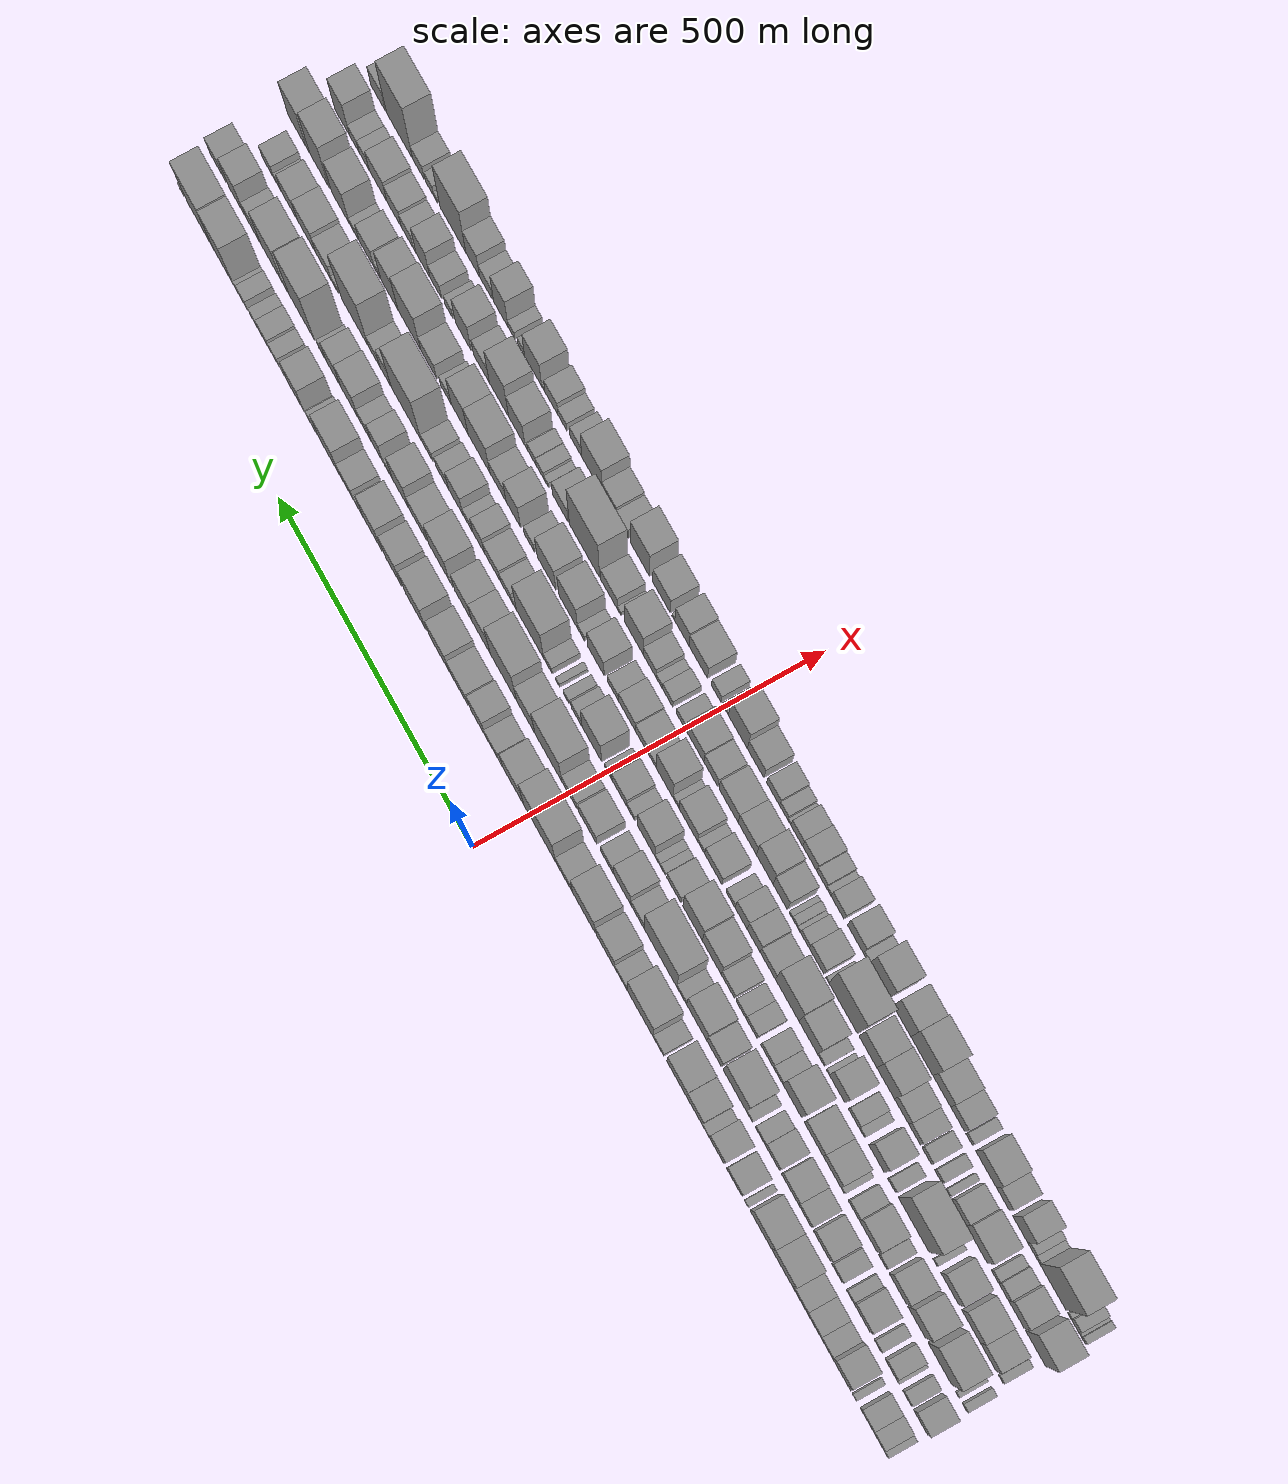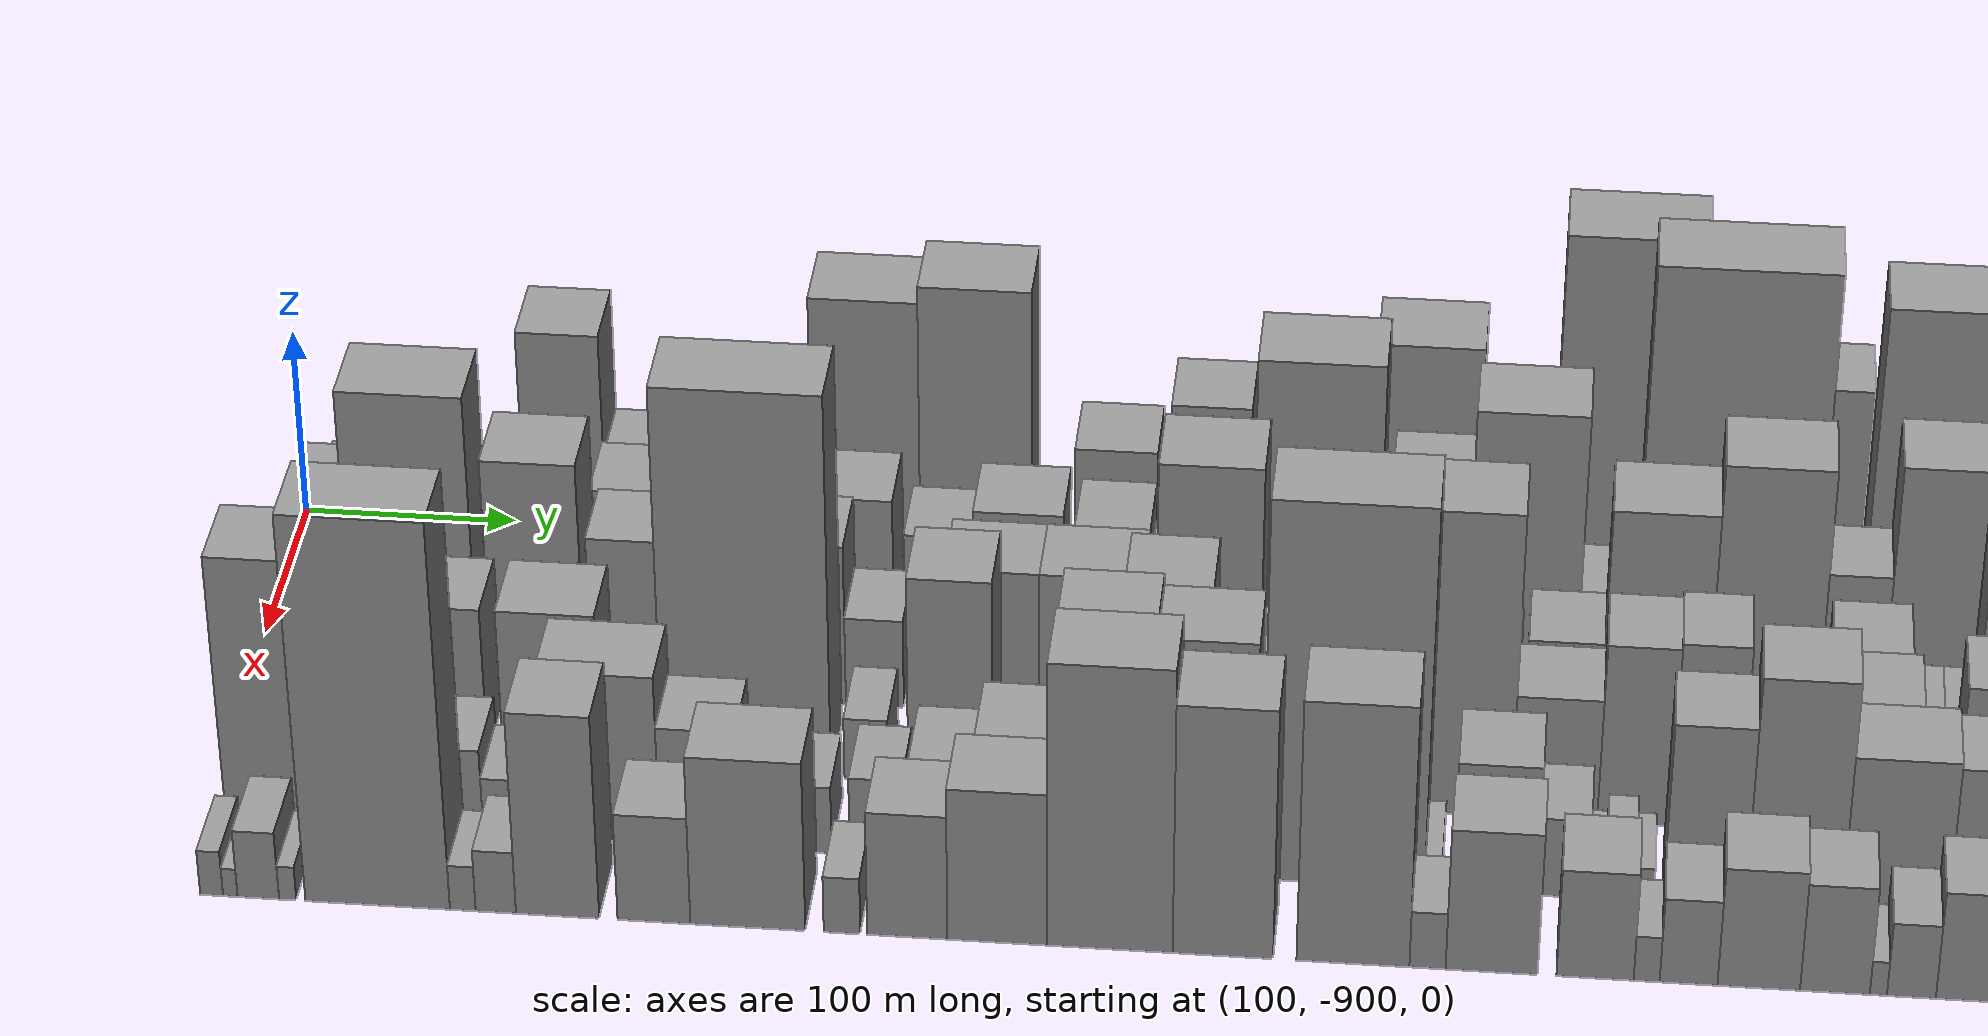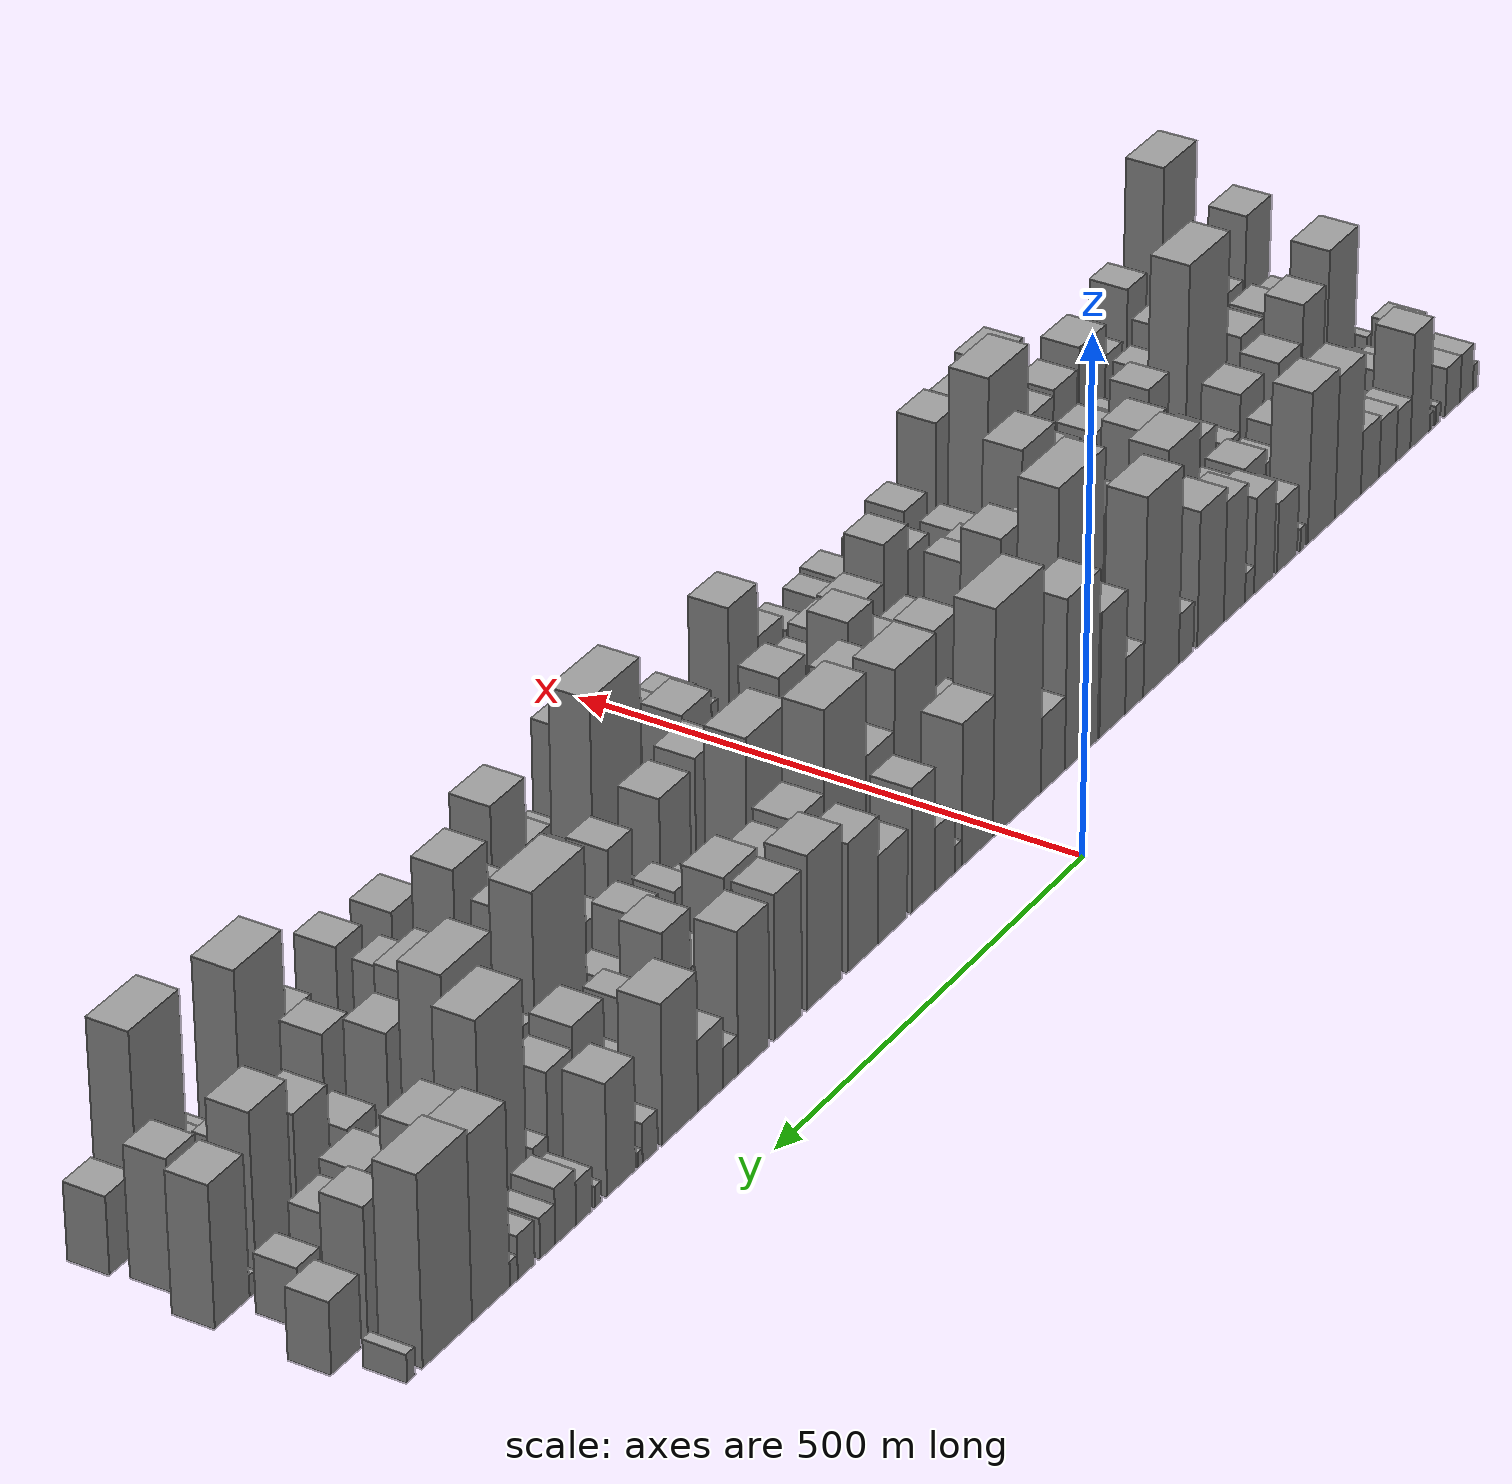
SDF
<sdf version="1.6">
 <world name="default">
  <scene>
   <sky><clouds><speed>12</speed></clouds></sky>
   <ambient>0.4 0.4 0.4 1</ambient>
   <background>0.7 0.7 0.7 1</background>
   <shadows>1</shadows>
  </scene>
  <gravity>0 0 -9.8066</gravity>
  <magnetic_field>6e-06 2.3e-05 -4.2e-05</magnetic_field>
  <physics default="0" name="default_physics" type="ode">
   <ode>
    <solver>
     <type>quick</type>
     <iters>10</iters>
     <sor>1.0</sor>
     <use_dynamic_moi_rescaling>0</use_dynamic_moi_rescaling>
    </solver>
    <constraints>
     <cfm>0</cfm>
     <erp>0.2</erp>
     <contact_max_correcting_vel>100</contact_max_correcting_vel>
     <contact_surface_layer>0.001</contact_surface_layer>
    </constraints>
   </ode>
   <max_step_size>0.004</max_step_size>
   <real_time_factor>1</real_time_factor>
   <real_time_update_rate>250</real_time_update_rate>
  </physics>
  <light name="sun" type="directional">
   <pose>0 0 10 0 0 0</pose>
   <diffuse>0.8 0.8 0.8 1</diffuse>
   <specular>0.2 0.2 0.2 1</specular>
   <attenuation>
    <range>1000</range>
    <constant>0.9</constant>
    <linear>0.01</linear>
    <quadratic>0.001</quadratic>
   </attenuation>
   <direction>-0.5 0.1 -0.9</direction>
  </light>
  <model name="building_1">
   <static>1</static>
   <pose>100.0000 -884.4774 0 0.000000 0.000000 0.000000</pose>
   <link name="link">
    <pose>0 0 13.50 0 0 0</pose>
    <collision name="collision"><geometry><box><size>40.0000 11.0452 27.0000</size></box></geometry></collision>
    <visual name="visual">
     <cast_shadows>0</cast_shadows>
     <geometry><box><size>40.0000 11.0452 27.0000</size></box></geometry>
     <material>
      <script>
       <uri>model://grey_wall/materials/scripts</uri>
       <uri>model://grey_wall/materials/textures</uri>
       <name>vrc/grey_wall</name>
      </script>
     </material>
    </visual>
   </link>
  </model>
  <model name="building_2">
   <static>1</static>
   <pose>100.0000 -865.9473 0 0.000000 0.000000 0.000000</pose>
   <link name="link">
    <pose>0 0 25.50 0 0 0</pose>
    <collision name="collision"><geometry><box><size>40.0000 26.0150 51.0000</size></box></geometry></collision>
    <visual name="visual">
     <cast_shadows>0</cast_shadows>
     <geometry><box><size>40.0000 26.0150 51.0000</size></box></geometry>
     <material>
      <script>
       <uri>model://grey_wall/materials/scripts</uri>
       <uri>model://grey_wall/materials/textures</uri>
       <name>vrc/grey_wall</name>
      </script>
     </material>
    </visual>
   </link>
  </model>
  <model name="building_3">
   <static>1</static>
   <pose>100.0000 -837.9995 0 0.000000 0.000000 0.000000</pose>
   <link name="link">
    <pose>0 0 25.50 0 0 0</pose>
    <collision name="collision"><geometry><box><size>40.0000 29.8806 51.0000</size></box></geometry></collision>
    <visual name="visual">
     <cast_shadows>0</cast_shadows>
     <geometry><box><size>40.0000 29.8806 51.0000</size></box></geometry>
     <material>
      <script>
       <uri>model://grey_wall/materials/scripts</uri>
       <uri>model://grey_wall/materials/textures</uri>
       <name>vrc/grey_wall</name>
      </script>
     </material>
    </visual>
   </link>
  </model>
  <model name="building_4">
   <static>1</static>
   <pose>100.0000 -808.3161 0 0.000000 0.000000 0.000000</pose>
   <link name="link">
    <pose>0 0 10.50 0 0 0</pose>
    <collision name="collision"><geometry><box><size>40.0000 9.4863 21.0000</size></box></geometry></collision>
    <visual name="visual">
     <cast_shadows>0</cast_shadows>
     <geometry><box><size>40.0000 9.4863 21.0000</size></box></geometry>
     <material>
      <script>
       <uri>model://grey_wall/materials/scripts</uri>
       <uri>model://grey_wall/materials/textures</uri>
       <name>vrc/grey_wall</name>
      </script>
     </material>
    </visual>
   </link>
  </model>
  <model name="building_5">
   <static>1</static>
   <pose>100.0000 -795.6300 0 0.000000 0.000000 0.000000</pose>
   <link name="link">
    <pose>0 0 9.00 0 0 0</pose>
    <collision name="collision"><geometry><box><size>40.0000 7.8860 18.0000</size></box></geometry></collision>
    <visual name="visual">
     <cast_shadows>0</cast_shadows>
     <geometry><box><size>40.0000 7.8860 18.0000</size></box></geometry>
     <material>
      <script>
       <uri>model://grey_wall/materials/scripts</uri>
       <uri>model://grey_wall/materials/textures</uri>
       <name>vrc/grey_wall</name>
      </script>
     </material>
    </visual>
   </link>
  </model>
  <model name="building_6">
   <static>1</static>
   <pose>100.0000 -772.4363 0 0.000000 0.000000 0.000000</pose>
   <link name="link">
    <pose>0 0 60.00 0 0 0</pose>
    <collision name="collision"><geometry><box><size>40.0000 38.5014 120.0000</size></box></geometry></collision>
    <visual name="visual">
     <cast_shadows>0</cast_shadows>
     <geometry><box><size>40.0000 38.5014 120.0000</size></box></geometry>
     <material>
      <script>
       <uri>model://grey_wall/materials/scripts</uri>
       <uri>model://grey_wall/materials/textures</uri>
       <name>vrc/grey_wall</name>
      </script>
     </material>
    </visual>
   </link>
  </model>
  <model name="building_7">
   <static>1</static>
   <pose>100.0000 -739.0061 0 0.000000 0.000000 0.000000</pose>
   <link name="link">
    <pose>0 0 27.00 0 0 0</pose>
    <collision name="collision"><geometry><box><size>40.0000 28.3591 54.0000</size></box></geometry></collision>
    <visual name="visual">
     <cast_shadows>0</cast_shadows>
     <geometry><box><size>40.0000 28.3591 54.0000</size></box></geometry>
     <material>
      <script>
       <uri>model://grey_wall/materials/scripts</uri>
       <uri>model://grey_wall/materials/textures</uri>
       <name>vrc/grey_wall</name>
      </script>
     </material>
    </visual>
   </link>
  </model>
  <model name="building_8">
   <static>1</static>
   <pose>100.0000 -708.1347 0 0.000000 0.000000 0.000000</pose>
   <link name="link">
    <pose>0 0 30.00 0 0 0</pose>
    <collision name="collision"><geometry><box><size>40.0000 33.3837 60.0000</size></box></geometry></collision>
    <visual name="visual">
     <cast_shadows>0</cast_shadows>
     <geometry><box><size>40.0000 33.3837 60.0000</size></box></geometry>
     <material>
      <script>
       <uri>model://grey_wall/materials/scripts</uri>
       <uri>model://grey_wall/materials/textures</uri>
       <name>vrc/grey_wall</name>
      </script>
     </material>
    </visual>
   </link>
  </model>
  <model name="building_9">
   <static>1</static>
   <pose>100.0000 -673.5564 0 0.000000 0.000000 0.000000</pose>
   <link name="link">
    <pose>0 0 33.00 0 0 0</pose>
    <collision name="collision"><geometry><box><size>40.0000 35.7729 66.0000</size></box></geometry></collision>
    <visual name="visual">
     <cast_shadows>0</cast_shadows>
     <geometry><box><size>40.0000 35.7729 66.0000</size></box></geometry>
     <material>
      <script>
       <uri>model://grey_wall/materials/scripts</uri>
       <uri>model://grey_wall/materials/textures</uri>
       <name>vrc/grey_wall</name>
      </script>
     </material>
    </visual>
   </link>
  </model>
  <model name="building_10">
   <static>1</static>
   <pose>100.0000 -630.4714 0 0.000000 0.000000 0.000000</pose>
   <link name="link">
    <pose>0 0 73.50 0 0 0</pose>
    <collision name="collision"><geometry><box><size>40.0000 50.3971 147.0000</size></box></geometry></collision>
    <visual name="visual">
     <cast_shadows>0</cast_shadows>
     <geometry><box><size>40.0000 50.3971 147.0000</size></box></geometry>
     <material>
      <script>
       <uri>model://grey_wall/materials/scripts</uri>
       <uri>model://grey_wall/materials/textures</uri>
       <name>vrc/grey_wall</name>
      </script>
     </material>
    </visual>
   </link>
  </model>
  <model name="building_11">
   <static>1</static>
   <pose>100.0000 -579.1356 0 0.000000 0.000000 0.000000</pose>
   <link name="link">
    <pose>0 0 78.00 0 0 0</pose>
    <collision name="collision"><geometry><box><size>40.0000 52.2745 156.0000</size></box></geometry></collision>
    <visual name="visual">
     <cast_shadows>0</cast_shadows>
     <geometry><box><size>40.0000 52.2745 156.0000</size></box></geometry>
     <material>
      <script>
       <uri>model://grey_wall/materials/scripts</uri>
       <uri>model://grey_wall/materials/textures</uri>
       <name>vrc/grey_wall</name>
      </script>
     </material>
    </visual>
   </link>
  </model>
  <model name="building_12">
   <static>1</static>
   <pose>100.0000 -543.9609 0 0.000000 0.000000 0.000000</pose>
   <link name="link">
    <pose>0 0 12.00 0 0 0</pose>
    <collision name="collision"><geometry><box><size>40.0000 10.0749 24.0000</size></box></geometry></collision>
    <visual name="visual">
     <cast_shadows>0</cast_shadows>
     <geometry><box><size>40.0000 10.0749 24.0000</size></box></geometry>
     <material>
      <script>
       <uri>model://grey_wall/materials/scripts</uri>
       <uri>model://grey_wall/materials/textures</uri>
       <name>vrc/grey_wall</name>
      </script>
     </material>
    </visual>
   </link>
  </model>
  <model name="building_13">
   <static>1</static>
   <pose>100.0000 -513.7747 0 0.000000 0.000000 0.000000</pose>
   <link name="link">
    <pose>0 0 36.00 0 0 0</pose>
    <collision name="collision"><geometry><box><size>40.0000 38.2976 72.0000</size></box></geometry></collision>
    <visual name="visual">
     <cast_shadows>0</cast_shadows>
     <geometry><box><size>40.0000 38.2976 72.0000</size></box></geometry>
     <material>
      <script>
       <uri>model://grey_wall/materials/scripts</uri>
       <uri>model://grey_wall/materials/textures</uri>
       <name>vrc/grey_wall</name>
      </script>
     </material>
    </visual>
   </link>
  </model>
  <model name="building_14">
   <static>1</static>
   <pose>100.0000 -470.0800 0 0.000000 0.000000 0.000000</pose>
   <link name="link">
    <pose>0 0 49.50 0 0 0</pose>
    <collision name="collision"><geometry><box><size>40.0000 37.0917 99.0000</size></box></geometry></collision>
    <visual name="visual">
     <cast_shadows>0</cast_shadows>
     <geometry><box><size>40.0000 37.0917 99.0000</size></box></geometry>
     <material>
      <script>
       <uri>model://grey_wall/materials/scripts</uri>
       <uri>model://grey_wall/materials/textures</uri>
       <name>vrc/grey_wall</name>
      </script>
     </material>
    </visual>
   </link>
  </model>
  <model name="building_15">
   <static>1</static>
   <pose>100.0000 -443.1057 0 0.000000 0.000000 0.000000</pose>
   <link name="link">
    <pose>0 0 15.00 0 0 0</pose>
    <collision name="collision"><geometry><box><size>40.0000 16.8570 30.0000</size></box></geometry></collision>
    <visual name="visual">
     <cast_shadows>0</cast_shadows>
     <geometry><box><size>40.0000 16.8570 30.0000</size></box></geometry>
     <material>
      <script>
       <uri>model://grey_wall/materials/scripts</uri>
       <uri>model://grey_wall/materials/textures</uri>
       <name>vrc/grey_wall</name>
      </script>
     </material>
    </visual>
   </link>
  </model>
  <model name="building_16">
   <static>1</static>
   <pose>100.0000 -414.9808 0 0.000000 0.000000 0.000000</pose>
   <link name="link">
    <pose>0 0 61.50 0 0 0</pose>
    <collision name="collision"><geometry><box><size>40.0000 39.3927 123.0000</size></box></geometry></collision>
    <visual name="visual">
     <cast_shadows>0</cast_shadows>
     <geometry><box><size>40.0000 39.3927 123.0000</size></box></geometry>
     <material>
      <script>
       <uri>model://grey_wall/materials/scripts</uri>
       <uri>model://grey_wall/materials/textures</uri>
       <name>vrc/grey_wall</name>
      </script>
     </material>
    </visual>
   </link>
  </model>
  <model name="building_17">
   <static>1</static>
   <pose>100.0000 -370.8028 0 0.000000 0.000000 0.000000</pose>
   <link name="link">
    <pose>0 0 69.00 0 0 0</pose>
    <collision name="collision"><geometry><box><size>40.0000 48.9632 138.0000</size></box></geometry></collision>
    <visual name="visual">
     <cast_shadows>0</cast_shadows>
     <geometry><box><size>40.0000 48.9632 138.0000</size></box></geometry>
     <material>
      <script>
       <uri>model://grey_wall/materials/scripts</uri>
       <uri>model://grey_wall/materials/textures</uri>
       <name>vrc/grey_wall</name>
      </script>
     </material>
    </visual>
   </link>
  </model>
  <model name="building_18">
   <static>1</static>
   <pose>100.0000 -325.9288 0 0.000000 0.000000 0.000000</pose>
   <link name="link">
    <pose>0 0 25.50 0 0 0</pose>
    <collision name="collision"><geometry><box><size>40.0000 26.7848 51.0000</size></box></geometry></collision>
    <visual name="visual">
     <cast_shadows>0</cast_shadows>
     <geometry><box><size>40.0000 26.7848 51.0000</size></box></geometry>
     <material>
      <script>
       <uri>model://grey_wall/materials/scripts</uri>
       <uri>model://grey_wall/materials/textures</uri>
       <name>vrc/grey_wall</name>
      </script>
     </material>
    </visual>
   </link>
  </model>
  <model name="building_19">
   <static>1</static>
   <pose>100.0000 -280.6266 0 0.000000 0.000000 0.000000</pose>
   <link name="link">
    <pose>0 0 100.50 0 0 0</pose>
    <collision name="collision"><geometry><box><size>40.0000 63.8196 201.0000</size></box></geometry></collision>
    <visual name="visual">
     <cast_shadows>0</cast_shadows>
     <geometry><box><size>40.0000 63.8196 201.0000</size></box></geometry>
     <material>
      <script>
       <uri>model://grey_wall/materials/scripts</uri>
       <uri>model://grey_wall/materials/textures</uri>
       <name>vrc/grey_wall</name>
      </script>
     </material>
    </visual>
   </link>
  </model>
  <model name="building_20">
   <static>1</static>
   <pose>100.0000 -232.5159 0 0.000000 0.000000 0.000000</pose>
   <link name="link">
    <pose>0 0 28.50 0 0 0</pose>
    <collision name="collision"><geometry><box><size>40.0000 32.4018 57.0000</size></box></geometry></collision>
    <visual name="visual">
     <cast_shadows>0</cast_shadows>
     <geometry><box><size>40.0000 32.4018 57.0000</size></box></geometry>
     <material>
      <script>
       <uri>model://grey_wall/materials/scripts</uri>
       <uri>model://grey_wall/materials/textures</uri>
       <name>vrc/grey_wall</name>
      </script>
     </material>
    </visual>
   </link>
  </model>
  <model name="building_21">
   <static>1</static>
   <pose>100.0000 -193.4009 0 0.000000 0.000000 0.000000</pose>
   <link name="link">
    <pose>0 0 63.00 0 0 0</pose>
    <collision name="collision"><geometry><box><size>40.0000 45.8282 126.0000</size></box></geometry></collision>
    <visual name="visual">
     <cast_shadows>0</cast_shadows>
     <geometry><box><size>40.0000 45.8282 126.0000</size></box></geometry>
     <material>
      <script>
       <uri>model://grey_wall/materials/scripts</uri>
       <uri>model://grey_wall/materials/textures</uri>
       <name>vrc/grey_wall</name>
      </script>
     </material>
    </visual>
   </link>
  </model>
  <model name="building_22">
   <static>1</static>
   <pose>100.0000 -138.6971 0 0.000000 0.000000 0.000000</pose>
   <link name="link">
    <pose>0 0 85.50 0 0 0</pose>
    <collision name="collision"><geometry><box><size>40.0000 57.5793 171.0000</size></box></geometry></collision>
    <visual name="visual">
     <cast_shadows>0</cast_shadows>
     <geometry><box><size>40.0000 57.5793 171.0000</size></box></geometry>
     <material>
      <script>
       <uri>model://grey_wall/materials/scripts</uri>
       <uri>model://grey_wall/materials/textures</uri>
       <name>vrc/grey_wall</name>
      </script>
     </material>
    </visual>
   </link>
  </model>
  <model name="building_23">
   <static>1</static>
   <pose>100.0000 -89.1934 0 0.000000 0.000000 0.000000</pose>
   <link name="link">
    <pose>0 0 37.50 0 0 0</pose>
    <collision name="collision"><geometry><box><size>40.0000 41.4282 75.0000</size></box></geometry></collision>
    <visual name="visual">
     <cast_shadows>0</cast_shadows>
     <geometry><box><size>40.0000 41.4282 75.0000</size></box></geometry>
     <material>
      <script>
       <uri>model://grey_wall/materials/scripts</uri>
       <uri>model://grey_wall/materials/textures</uri>
       <name>vrc/grey_wall</name>
      </script>
     </material>
    </visual>
   </link>
  </model>
  <model name="building_24">
   <static>1</static>
   <pose>100.0000 -27.6241 0 0.000000 0.000000 0.000000</pose>
   <link name="link">
    <pose>0 0 112.50 0 0 0</pose>
    <collision name="collision"><geometry><box><size>40.0000 81.7104 225.0000</size></box></geometry></collision>
    <visual name="visual">
     <cast_shadows>0</cast_shadows>
     <geometry><box><size>40.0000 81.7104 225.0000</size></box></geometry>
     <material>
      <script>
       <uri>model://grey_wall/materials/scripts</uri>
       <uri>model://grey_wall/materials/textures</uri>
       <name>vrc/grey_wall</name>
      </script>
     </material>
    </visual>
   </link>
  </model>
  <model name="building_25">
   <static>1</static>
   <pose>100.0000 39.7437 0 0.000000 0.000000 0.000000</pose>
   <link name="link">
    <pose>0 0 70.50 0 0 0</pose>
    <collision name="collision"><geometry><box><size>40.0000 53.0252 141.0000</size></box></geometry></collision>
    <visual name="visual">
     <cast_shadows>0</cast_shadows>
     <geometry><box><size>40.0000 53.0252 141.0000</size></box></geometry>
     <material>
      <script>
       <uri>model://grey_wall/materials/scripts</uri>
       <uri>model://grey_wall/materials/textures</uri>
       <name>vrc/grey_wall</name>
      </script>
     </material>
    </visual>
   </link>
  </model>
  <model name="building_26">
   <static>1</static>
   <pose>100.0000 71.7671 0 0.000000 0.000000 0.000000</pose>
   <link name="link">
    <pose>0 0 13.50 0 0 0</pose>
    <collision name="collision"><geometry><box><size>40.0000 11.0216 27.0000</size></box></geometry></collision>
    <visual name="visual">
     <cast_shadows>0</cast_shadows>
     <geometry><box><size>40.0000 11.0216 27.0000</size></box></geometry>
     <material>
      <script>
       <uri>model://grey_wall/materials/scripts</uri>
       <uri>model://grey_wall/materials/textures</uri>
       <name>vrc/grey_wall</name>
      </script>
     </material>
    </visual>
   </link>
  </model>
  <model name="building_27">
   <static>1</static>
   <pose>100.0000 94.3355 0 0.000000 0.000000 0.000000</pose>
   <link name="link">
    <pose>0 0 31.50 0 0 0</pose>
    <collision name="collision"><geometry><box><size>40.0000 34.1152 63.0000</size></box></geometry></collision>
    <visual name="visual">
     <cast_shadows>0</cast_shadows>
     <geometry><box><size>40.0000 34.1152 63.0000</size></box></geometry>
     <material>
      <script>
       <uri>model://grey_wall/materials/scripts</uri>
       <uri>model://grey_wall/materials/textures</uri>
       <name>vrc/grey_wall</name>
      </script>
     </material>
    </visual>
   </link>
  </model>
  <model name="building_28">
   <static>1</static>
   <pose>100.0000 130.4107 0 0.000000 0.000000 0.000000</pose>
   <link name="link">
    <pose>0 0 61.50 0 0 0</pose>
    <collision name="collision"><geometry><box><size>40.0000 38.0351 123.0000</size></box></geometry></collision>
    <visual name="visual">
     <cast_shadows>0</cast_shadows>
     <geometry><box><size>40.0000 38.0351 123.0000</size></box></geometry>
     <material>
      <script>
       <uri>model://grey_wall/materials/scripts</uri>
       <uri>model://grey_wall/materials/textures</uri>
       <name>vrc/grey_wall</name>
      </script>
     </material>
    </visual>
   </link>
  </model>
  <model name="building_29">
   <static>1</static>
   <pose>100.0000 180.1995 0 0.000000 0.000000 0.000000</pose>
   <link name="link">
    <pose>0 0 43.50 0 0 0</pose>
    <collision name="collision"><geometry><box><size>40.0000 47.5425 87.0000</size></box></geometry></collision>
    <visual name="visual">
     <cast_shadows>0</cast_shadows>
     <geometry><box><size>40.0000 47.5425 87.0000</size></box></geometry>
     <material>
      <script>
       <uri>model://grey_wall/materials/scripts</uri>
       <uri>model://grey_wall/materials/textures</uri>
       <name>vrc/grey_wall</name>
      </script>
     </material>
    </visual>
   </link>
  </model>
  <model name="building_30">
   <static>1</static>
   <pose>100.0000 228.5666 0 0.000000 0.000000 0.000000</pose>
   <link name="link">
    <pose>0 0 63.00 0 0 0</pose>
    <collision name="collision"><geometry><box><size>40.0000 49.1916 126.0000</size></box></geometry></collision>
    <visual name="visual">
     <cast_shadows>0</cast_shadows>
     <geometry><box><size>40.0000 49.1916 126.0000</size></box></geometry>
     <material>
      <script>
       <uri>model://grey_wall/materials/scripts</uri>
       <uri>model://grey_wall/materials/textures</uri>
       <name>vrc/grey_wall</name>
      </script>
     </material>
    </visual>
   </link>
  </model>
  <model name="building_31">
   <static>1</static>
   <pose>100.0000 290.3817 0 0.000000 0.000000 0.000000</pose>
   <link name="link">
    <pose>0 0 75.00 0 0 0</pose>
    <collision name="collision"><geometry><box><size>40.0000 54.4385 150.0000</size></box></geometry></collision>
    <visual name="visual">
     <cast_shadows>0</cast_shadows>
     <geometry><box><size>40.0000 54.4385 150.0000</size></box></geometry>
     <material>
      <script>
       <uri>model://grey_wall/materials/scripts</uri>
       <uri>model://grey_wall/materials/textures</uri>
       <name>vrc/grey_wall</name>
      </script>
     </material>
    </visual>
   </link>
  </model>
  <model name="building_32">
   <static>1</static>
   <pose>100.0000 347.7586 0 0.000000 0.000000 0.000000</pose>
   <link name="link">
    <pose>0 0 70.50 0 0 0</pose>
    <collision name="collision"><geometry><box><size>40.0000 42.3155 141.0000</size></box></geometry></collision>
    <visual name="visual">
     <cast_shadows>0</cast_shadows>
     <geometry><box><size>40.0000 42.3155 141.0000</size></box></geometry>
     <material>
      <script>
       <uri>model://grey_wall/materials/scripts</uri>
       <uri>model://grey_wall/materials/textures</uri>
       <name>vrc/grey_wall</name>
      </script>
     </material>
    </visual>
   </link>
  </model>
  <model name="building_33">
   <static>1</static>
   <pose>100.0000 402.1196 0 0.000000 0.000000 0.000000</pose>
   <link name="link">
    <pose>0 0 69.00 0 0 0</pose>
    <collision name="collision"><geometry><box><size>40.0000 48.4064 138.0000</size></box></geometry></collision>
    <visual name="visual">
     <cast_shadows>0</cast_shadows>
     <geometry><box><size>40.0000 48.4064 138.0000</size></box></geometry>
     <material>
      <script>
       <uri>model://grey_wall/materials/scripts</uri>
       <uri>model://grey_wall/materials/textures</uri>
       <name>vrc/grey_wall</name>
      </script>
     </material>
    </visual>
   </link>
  </model>
  <model name="building_34">
   <static>1</static>
   <pose>100.0000 437.7111 0 0.000000 0.000000 0.000000</pose>
   <link name="link">
    <pose>0 0 19.50 0 0 0</pose>
    <collision name="collision"><geometry><box><size>40.0000 22.7765 39.0000</size></box></geometry></collision>
    <visual name="visual">
     <cast_shadows>0</cast_shadows>
     <geometry><box><size>40.0000 22.7765 39.0000</size></box></geometry>
     <material>
      <script>
       <uri>model://grey_wall/materials/scripts</uri>
       <uri>model://grey_wall/materials/textures</uri>
       <name>vrc/grey_wall</name>
      </script>
     </material>
    </visual>
   </link>
  </model>
  <model name="building_35">
   <static>1</static>
   <pose>100.0000 468.4505 0 0.000000 0.000000 0.000000</pose>
   <link name="link">
    <pose>0 0 34.50 0 0 0</pose>
    <collision name="collision"><geometry><box><size>40.0000 38.7024 69.0000</size></box></geometry></collision>
    <visual name="visual">
     <cast_shadows>0</cast_shadows>
     <geometry><box><size>40.0000 38.7024 69.0000</size></box></geometry>
     <material>
      <script>
       <uri>model://grey_wall/materials/scripts</uri>
       <uri>model://grey_wall/materials/textures</uri>
       <name>vrc/grey_wall</name>
      </script>
     </material>
    </visual>
   </link>
  </model>
  <model name="building_36">
   <static>1</static>
   <pose>100.0000 514.6712 0 0.000000 0.000000 0.000000</pose>
   <link name="link">
    <pose>0 0 67.50 0 0 0</pose>
    <collision name="collision"><geometry><box><size>40.0000 53.7389 135.0000</size></box></geometry></collision>
    <visual name="visual">
     <cast_shadows>0</cast_shadows>
     <geometry><box><size>40.0000 53.7389 135.0000</size></box></geometry>
     <material>
      <script>
       <uri>model://grey_wall/materials/scripts</uri>
       <uri>model://grey_wall/materials/textures</uri>
       <name>vrc/grey_wall</name>
      </script>
     </material>
    </visual>
   </link>
  </model>
  <model name="building_37">
   <static>1</static>
   <pose>100.0000 559.9014 0 0.000000 0.000000 0.000000</pose>
   <link name="link">
    <pose>0 0 19.50 0 0 0</pose>
    <collision name="collision"><geometry><box><size>40.0000 22.7215 39.0000</size></box></geometry></collision>
    <visual name="visual">
     <cast_shadows>0</cast_shadows>
     <geometry><box><size>40.0000 22.7215 39.0000</size></box></geometry>
     <material>
      <script>
       <uri>model://grey_wall/materials/scripts</uri>
       <uri>model://grey_wall/materials/textures</uri>
       <name>vrc/grey_wall</name>
      </script>
     </material>
    </visual>
   </link>
  </model>
  <model name="building_38">
   <static>1</static>
   <pose>100.0000 574.8513 0 0.000000 0.000000 0.000000</pose>
   <link name="link">
    <pose>0 0 7.50 0 0 0</pose>
    <collision name="collision"><geometry><box><size>40.0000 7.1783 15.0000</size></box></geometry></collision>
    <visual name="visual">
     <cast_shadows>0</cast_shadows>
     <geometry><box><size>40.0000 7.1783 15.0000</size></box></geometry>
     <material>
      <script>
       <uri>model://grey_wall/materials/scripts</uri>
       <uri>model://grey_wall/materials/textures</uri>
       <name>vrc/grey_wall</name>
      </script>
     </material>
    </visual>
   </link>
  </model>
  <model name="building_39">
   <static>1</static>
   <pose>100.0000 602.8528 0 0.000000 0.000000 0.000000</pose>
   <link name="link">
    <pose>0 0 54.00 0 0 0</pose>
    <collision name="collision"><geometry><box><size>40.0000 42.8248 108.0000</size></box></geometry></collision>
    <visual name="visual">
     <cast_shadows>0</cast_shadows>
     <geometry><box><size>40.0000 42.8248 108.0000</size></box></geometry>
     <material>
      <script>
       <uri>model://grey_wall/materials/scripts</uri>
       <uri>model://grey_wall/materials/textures</uri>
       <name>vrc/grey_wall</name>
      </script>
     </material>
    </visual>
   </link>
  </model>
  <model name="building_40">
   <static>1</static>
   <pose>100.0000 637.0254 0 0.000000 0.000000 0.000000</pose>
   <link name="link">
    <pose>0 0 10.50 0 0 0</pose>
    <collision name="collision"><geometry><box><size>40.0000 9.5204 21.0000</size></box></geometry></collision>
    <visual name="visual">
     <cast_shadows>0</cast_shadows>
     <geometry><box><size>40.0000 9.5204 21.0000</size></box></geometry>
     <material>
      <script>
       <uri>model://grey_wall/materials/scripts</uri>
       <uri>model://grey_wall/materials/textures</uri>
       <name>vrc/grey_wall</name>
      </script>
     </material>
    </visual>
   </link>
  </model>
  <model name="building_41">
   <static>1</static>
   <pose>100.0000 657.5526 0 0.000000 0.000000 0.000000</pose>
   <link name="link">
    <pose>0 0 21.00 0 0 0</pose>
    <collision name="collision"><geometry><box><size>40.0000 23.5340 42.0000</size></box></geometry></collision>
    <visual name="visual">
     <cast_shadows>0</cast_shadows>
     <geometry><box><size>40.0000 23.5340 42.0000</size></box></geometry>
     <material>
      <script>
       <uri>model://grey_wall/materials/scripts</uri>
       <uri>model://grey_wall/materials/textures</uri>
       <name>vrc/grey_wall</name>
      </script>
     </material>
    </visual>
   </link>
  </model>
  <model name="building_42">
   <static>1</static>
   <pose>100.0000 684.4716 0 0.000000 0.000000 0.000000</pose>
   <link name="link">
    <pose>0 0 27.00 0 0 0</pose>
    <collision name="collision"><geometry><box><size>40.0000 30.3041 54.0000</size></box></geometry></collision>
    <visual name="visual">
     <cast_shadows>0</cast_shadows>
     <geometry><box><size>40.0000 30.3041 54.0000</size></box></geometry>
     <material>
      <script>
       <uri>model://grey_wall/materials/scripts</uri>
       <uri>model://grey_wall/materials/textures</uri>
       <name>vrc/grey_wall</name>
      </script>
     </material>
    </visual>
   </link>
  </model>
  <model name="building_43">
   <static>1</static>
   <pose>100.0000 710.6328 0 0.000000 0.000000 0.000000</pose>
   <link name="link">
    <pose>0 0 19.50 0 0 0</pose>
    <collision name="collision"><geometry><box><size>40.0000 22.0183 39.0000</size></box></geometry></collision>
    <visual name="visual">
     <cast_shadows>0</cast_shadows>
     <geometry><box><size>40.0000 22.0183 39.0000</size></box></geometry>
     <material>
      <script>
       <uri>model://grey_wall/materials/scripts</uri>
       <uri>model://grey_wall/materials/textures</uri>
       <name>vrc/grey_wall</name>
      </script>
     </material>
    </visual>
   </link>
  </model>
  <model name="building_44">
   <static>1</static>
   <pose>100.0000 741.7868 0 0.000000 0.000000 0.000000</pose>
   <link name="link">
    <pose>0 0 21.00 0 0 0</pose>
    <collision name="collision"><geometry><box><size>40.0000 24.2898 42.0000</size></box></geometry></collision>
    <visual name="visual">
     <cast_shadows>0</cast_shadows>
     <geometry><box><size>40.0000 24.2898 42.0000</size></box></geometry>
     <material>
      <script>
       <uri>model://grey_wall/materials/scripts</uri>
       <uri>model://grey_wall/materials/textures</uri>
       <name>vrc/grey_wall</name>
      </script>
     </material>
    </visual>
   </link>
  </model>
  <model name="building_45">
   <static>1</static>
   <pose>100.0000 759.4877 0 0.000000 0.000000 0.000000</pose>
   <link name="link">
    <pose>0 0 12.00 0 0 0</pose>
    <collision name="collision"><geometry><box><size>40.0000 11.1120 24.0000</size></box></geometry></collision>
    <visual name="visual">
     <cast_shadows>0</cast_shadows>
     <geometry><box><size>40.0000 11.1120 24.0000</size></box></geometry>
     <material>
      <script>
       <uri>model://grey_wall/materials/scripts</uri>
       <uri>model://grey_wall/materials/textures</uri>
       <name>vrc/grey_wall</name>
      </script>
     </material>
    </visual>
   </link>
  </model>
  <model name="building_46">
   <static>1</static>
   <pose>100.0000 791.9867 0 0.000000 0.000000 0.000000</pose>
   <link name="link">
    <pose>0 0 87.00 0 0 0</pose>
    <collision name="collision"><geometry><box><size>40.0000 53.8859 174.0000</size></box></geometry></collision>
    <visual name="visual">
     <cast_shadows>0</cast_shadows>
     <geometry><box><size>40.0000 53.8859 174.0000</size></box></geometry>
     <material>
      <script>
       <uri>model://grey_wall/materials/scripts</uri>
       <uri>model://grey_wall/materials/textures</uri>
       <name>vrc/grey_wall</name>
      </script>
     </material>
    </visual>
   </link>
  </model>
  <model name="building_47">
   <static>1</static>
   <pose>100.0000 853.4867 0 0.000000 0.000000 0.000000</pose>
   <link name="link">
    <pose>0 0 90.00 0 0 0</pose>
    <collision name="collision"><geometry><box><size>40.0000 69.1143 180.0000</size></box></geometry></collision>
    <visual name="visual">
     <cast_shadows>0</cast_shadows>
     <geometry><box><size>40.0000 69.1143 180.0000</size></box></geometry>
     <material>
      <script>
       <uri>model://grey_wall/materials/scripts</uri>
       <uri>model://grey_wall/materials/textures</uri>
       <name>vrc/grey_wall</name>
      </script>
     </material>
    </visual>
   </link>
  </model>
  <model name="building_48">
   <static>1</static>
   <pose>100.0000 903.7542 0 0.000000 0.000000 0.000000</pose>
   <link name="link">
    <pose>0 0 13.50 0 0 0</pose>
    <collision name="collision"><geometry><box><size>40.0000 11.4207 27.0000</size></box></geometry></collision>
    <visual name="visual">
     <cast_shadows>0</cast_shadows>
     <geometry><box><size>40.0000 11.4207 27.0000</size></box></geometry>
     <material>
      <script>
       <uri>model://grey_wall/materials/scripts</uri>
       <uri>model://grey_wall/materials/textures</uri>
       <name>vrc/grey_wall</name>
      </script>
     </material>
    </visual>
   </link>
  </model>
  <model name="building_49">
   <static>1</static>
   <pose>155.0000 -873.2870 0 0.000000 0.000000 0.000000</pose>
   <link name="link">
    <pose>0 0 31.50 0 0 0</pose>
    <collision name="collision"><geometry><box><size>40.0000 33.4260 63.0000</size></box></geometry></collision>
    <visual name="visual">
     <cast_shadows>0</cast_shadows>
     <geometry><box><size>40.0000 33.4260 63.0000</size></box></geometry>
     <material>
      <script>
       <uri>model://grey_wall/materials/scripts</uri>
       <uri>model://grey_wall/materials/textures</uri>
       <name>vrc/grey_wall</name>
      </script>
     </material>
    </visual>
   </link>
  </model>
  <model name="building_50">
   <static>1</static>
   <pose>155.0000 -840.3611 0 0.000000 0.000000 0.000000</pose>
   <link name="link">
    <pose>0 0 18.00 0 0 0</pose>
    <collision name="collision"><geometry><box><size>40.0000 20.4257 36.0000</size></box></geometry></collision>
    <visual name="visual">
     <cast_shadows>0</cast_shadows>
     <geometry><box><size>40.0000 20.4257 36.0000</size></box></geometry>
     <material>
      <script>
       <uri>model://grey_wall/materials/scripts</uri>
       <uri>model://grey_wall/materials/textures</uri>
       <name>vrc/grey_wall</name>
      </script>
     </material>
    </visual>
   </link>
  </model>
  <model name="building_51">
   <static>1</static>
   <pose>155.0000 -817.4871 0 0.000000 0.000000 0.000000</pose>
   <link name="link">
    <pose>0 0 7.50 0 0 0</pose>
    <collision name="collision"><geometry><box><size>40.0000 7.3223 15.0000</size></box></geometry></collision>
    <visual name="visual">
     <cast_shadows>0</cast_shadows>
     <geometry><box><size>40.0000 7.3223 15.0000</size></box></geometry>
     <material>
      <script>
       <uri>model://grey_wall/materials/scripts</uri>
       <uri>model://grey_wall/materials/textures</uri>
       <name>vrc/grey_wall</name>
      </script>
     </material>
    </visual>
   </link>
  </model>
  <model name="building_52">
   <static>1</static>
   <pose>155.0000 -800.2898 0 0.000000 0.000000 0.000000</pose>
   <link name="link">
    <pose>0 0 25.50 0 0 0</pose>
    <collision name="collision"><geometry><box><size>40.0000 27.0723 51.0000</size></box></geometry></collision>
    <visual name="visual">
     <cast_shadows>0</cast_shadows>
     <geometry><box><size>40.0000 27.0723 51.0000</size></box></geometry>
     <material>
      <script>
       <uri>model://grey_wall/materials/scripts</uri>
       <uri>model://grey_wall/materials/textures</uri>
       <name>vrc/grey_wall</name>
      </script>
     </material>
    </visual>
   </link>
  </model>
  <model name="building_53">
   <static>1</static>
   <pose>155.0000 -769.2346 0 0.000000 0.000000 0.000000</pose>
   <link name="link">
    <pose>0 0 16.50 0 0 0</pose>
    <collision name="collision"><geometry><box><size>40.0000 17.0382 33.0000</size></box></geometry></collision>
    <visual name="visual">
     <cast_shadows>0</cast_shadows>
     <geometry><box><size>40.0000 17.0382 33.0000</size></box></geometry>
     <material>
      <script>
       <uri>model://grey_wall/materials/scripts</uri>
       <uri>model://grey_wall/materials/textures</uri>
       <name>vrc/grey_wall</name>
      </script>
     </material>
    </visual>
   </link>
  </model>
  <model name="building_54">
   <static>1</static>
   <pose>155.0000 -730.5223 0 0.000000 0.000000 0.000000</pose>
   <link name="link">
    <pose>0 0 36.00 0 0 0</pose>
    <collision name="collision"><geometry><box><size>40.0000 40.3863 72.0000</size></box></geometry></collision>
    <visual name="visual">
     <cast_shadows>0</cast_shadows>
     <geometry><box><size>40.0000 40.3863 72.0000</size></box></geometry>
     <material>
      <script>
       <uri>model://grey_wall/materials/scripts</uri>
       <uri>model://grey_wall/materials/textures</uri>
       <name>vrc/grey_wall</name>
      </script>
     </material>
    </visual>
   </link>
  </model>
  <model name="building_55">
   <static>1</static>
   <pose>155.0000 -701.5966 0 0.000000 0.000000 0.000000</pose>
   <link name="link">
    <pose>0 0 16.50 0 0 0</pose>
    <collision name="collision"><geometry><box><size>40.0000 17.4652 33.0000</size></box></geometry></collision>
    <visual name="visual">
     <cast_shadows>0</cast_shadows>
     <geometry><box><size>40.0000 17.4652 33.0000</size></box></geometry>
     <material>
      <script>
       <uri>model://grey_wall/materials/scripts</uri>
       <uri>model://grey_wall/materials/textures</uri>
       <name>vrc/grey_wall</name>
      </script>
     </material>
    </visual>
   </link>
  </model>
  <model name="building_56">
   <static>1</static>
   <pose>155.0000 -670.0033 0 0.000000 0.000000 0.000000</pose>
   <link name="link">
    <pose>0 0 22.50 0 0 0</pose>
    <collision name="collision"><geometry><box><size>40.0000 25.7213 45.0000</size></box></geometry></collision>
    <visual name="visual">
     <cast_shadows>0</cast_shadows>
     <geometry><box><size>40.0000 25.7213 45.0000</size></box></geometry>
     <material>
      <script>
       <uri>model://grey_wall/materials/scripts</uri>
       <uri>model://grey_wall/materials/textures</uri>
       <name>vrc/grey_wall</name>
      </script>
     </material>
    </visual>
   </link>
  </model>
  <model name="building_57">
   <static>1</static>
   <pose>155.0000 -632.3039 0 0.000000 0.000000 0.000000</pose>
   <link name="link">
    <pose>0 0 37.50 0 0 0</pose>
    <collision name="collision"><geometry><box><size>40.0000 41.6775 75.0000</size></box></geometry></collision>
    <visual name="visual">
     <cast_shadows>0</cast_shadows>
     <geometry><box><size>40.0000 41.6775 75.0000</size></box></geometry>
     <material>
      <script>
       <uri>model://grey_wall/materials/scripts</uri>
       <uri>model://grey_wall/materials/textures</uri>
       <name>vrc/grey_wall</name>
      </script>
     </material>
    </visual>
   </link>
  </model>
  <model name="building_58">
   <static>1</static>
   <pose>155.0000 -590.5576 0 0.000000 0.000000 0.000000</pose>
   <link name="link">
    <pose>0 0 28.50 0 0 0</pose>
    <collision name="collision"><geometry><box><size>40.0000 31.8151 57.0000</size></box></geometry></collision>
    <visual name="visual">
     <cast_shadows>0</cast_shadows>
     <geometry><box><size>40.0000 31.8151 57.0000</size></box></geometry>
     <material>
      <script>
       <uri>model://grey_wall/materials/scripts</uri>
       <uri>model://grey_wall/materials/textures</uri>
       <name>vrc/grey_wall</name>
      </script>
     </material>
    </visual>
   </link>
  </model>
  <model name="building_59">
   <static>1</static>
   <pose>155.0000 -553.9501 0 0.000000 0.000000 0.000000</pose>
   <link name="link">
    <pose>0 0 36.00 0 0 0</pose>
    <collision name="collision"><geometry><box><size>40.0000 41.3999 72.0000</size></box></geometry></collision>
    <visual name="visual">
     <cast_shadows>0</cast_shadows>
     <geometry><box><size>40.0000 41.3999 72.0000</size></box></geometry>
     <material>
      <script>
       <uri>model://grey_wall/materials/scripts</uri>
       <uri>model://grey_wall/materials/textures</uri>
       <name>vrc/grey_wall</name>
      </script>
     </material>
    </visual>
   </link>
  </model>
  <model name="building_60">
   <static>1</static>
   <pose>155.0000 -511.0040 0 0.000000 0.000000 0.000000</pose>
   <link name="link">
    <pose>0 0 33.00 0 0 0</pose>
    <collision name="collision"><geometry><box><size>40.0000 34.4923 66.0000</size></box></geometry></collision>
    <visual name="visual">
     <cast_shadows>0</cast_shadows>
     <geometry><box><size>40.0000 34.4923 66.0000</size></box></geometry>
     <material>
      <script>
       <uri>model://grey_wall/materials/scripts</uri>
       <uri>model://grey_wall/materials/textures</uri>
       <name>vrc/grey_wall</name>
      </script>
     </material>
    </visual>
   </link>
  </model>
  <model name="building_61">
   <static>1</static>
   <pose>155.0000 -480.9429 0 0.000000 0.000000 0.000000</pose>
   <link name="link">
    <pose>0 0 22.50 0 0 0</pose>
    <collision name="collision"><geometry><box><size>40.0000 25.6301 45.0000</size></box></geometry></collision>
    <visual name="visual">
     <cast_shadows>0</cast_shadows>
     <geometry><box><size>40.0000 25.6301 45.0000</size></box></geometry>
     <material>
      <script>
       <uri>model://grey_wall/materials/scripts</uri>
       <uri>model://grey_wall/materials/textures</uri>
       <name>vrc/grey_wall</name>
      </script>
     </material>
    </visual>
   </link>
  </model>
  <model name="building_62">
   <static>1</static>
   <pose>155.0000 -454.3677 0 0.000000 0.000000 0.000000</pose>
   <link name="link">
    <pose>0 0 15.00 0 0 0</pose>
    <collision name="collision"><geometry><box><size>40.0000 15.5203 30.0000</size></box></geometry></collision>
    <visual name="visual">
     <cast_shadows>0</cast_shadows>
     <geometry><box><size>40.0000 15.5203 30.0000</size></box></geometry>
     <material>
      <script>
       <uri>model://grey_wall/materials/scripts</uri>
       <uri>model://grey_wall/materials/textures</uri>
       <name>vrc/grey_wall</name>
      </script>
     </material>
    </visual>
   </link>
  </model>
  <model name="building_63">
   <static>1</static>
   <pose>155.0000 -417.8181 0 0.000000 0.000000 0.000000</pose>
   <link name="link">
    <pose>0 0 81.00 0 0 0</pose>
    <collision name="collision"><geometry><box><size>40.0000 57.5789 162.0000</size></box></geometry></collision>
    <visual name="visual">
     <cast_shadows>0</cast_shadows>
     <geometry><box><size>40.0000 57.5789 162.0000</size></box></geometry>
     <material>
      <script>
       <uri>model://grey_wall/materials/scripts</uri>
       <uri>model://grey_wall/materials/textures</uri>
       <name>vrc/grey_wall</name>
      </script>
     </material>
    </visual>
   </link>
  </model>
  <model name="building_64">
   <static>1</static>
   <pose>155.0000 -366.7792 0 0.000000 0.000000 0.000000</pose>
   <link name="link">
    <pose>0 0 51.00 0 0 0</pose>
    <collision name="collision"><geometry><box><size>40.0000 36.4988 102.0000</size></box></geometry></collision>
    <visual name="visual">
     <cast_shadows>0</cast_shadows>
     <geometry><box><size>40.0000 36.4988 102.0000</size></box></geometry>
     <material>
      <script>
       <uri>model://grey_wall/materials/scripts</uri>
       <uri>model://grey_wall/materials/textures</uri>
       <name>vrc/grey_wall</name>
      </script>
     </material>
    </visual>
   </link>
  </model>
  <model name="building_65">
   <static>1</static>
   <pose>155.0000 -323.1969 0 0.000000 0.000000 0.000000</pose>
   <link name="link">
    <pose>0 0 70.50 0 0 0</pose>
    <collision name="collision"><geometry><box><size>40.0000 50.6659 141.0000</size></box></geometry></collision>
    <visual name="visual">
     <cast_shadows>0</cast_shadows>
     <geometry><box><size>40.0000 50.6659 141.0000</size></box></geometry>
     <material>
      <script>
       <uri>model://grey_wall/materials/scripts</uri>
       <uri>model://grey_wall/materials/textures</uri>
       <name>vrc/grey_wall</name>
      </script>
     </material>
    </visual>
   </link>
  </model>
  <model name="building_66">
   <static>1</static>
   <pose>155.0000 -285.4893 0 0.000000 0.000000 0.000000</pose>
   <link name="link">
    <pose>0 0 22.50 0 0 0</pose>
    <collision name="collision"><geometry><box><size>40.0000 24.7493 45.0000</size></box></geometry></collision>
    <visual name="visual">
     <cast_shadows>0</cast_shadows>
     <geometry><box><size>40.0000 24.7493 45.0000</size></box></geometry>
     <material>
      <script>
       <uri>model://grey_wall/materials/scripts</uri>
       <uri>model://grey_wall/materials/textures</uri>
       <name>vrc/grey_wall</name>
      </script>
     </material>
    </visual>
   </link>
  </model>
  <model name="building_67">
   <static>1</static>
   <pose>155.0000 -232.5237 0 0.000000 0.000000 0.000000</pose>
   <link name="link">
    <pose>0 0 111.00 0 0 0</pose>
    <collision name="collision"><geometry><box><size>40.0000 81.1820 222.0000</size></box></geometry></collision>
    <visual name="visual">
     <cast_shadows>0</cast_shadows>
     <geometry><box><size>40.0000 81.1820 222.0000</size></box></geometry>
     <material>
      <script>
       <uri>model://grey_wall/materials/scripts</uri>
       <uri>model://grey_wall/materials/textures</uri>
       <name>vrc/grey_wall</name>
      </script>
     </material>
    </visual>
   </link>
  </model>
  <model name="building_68">
   <static>1</static>
   <pose>155.0000 -175.2073 0 0.000000 0.000000 0.000000</pose>
   <link name="link">
    <pose>0 0 31.50 0 0 0</pose>
    <collision name="collision"><geometry><box><size>40.0000 33.4507 63.0000</size></box></geometry></collision>
    <visual name="visual">
     <cast_shadows>0</cast_shadows>
     <geometry><box><size>40.0000 33.4507 63.0000</size></box></geometry>
     <material>
      <script>
       <uri>model://grey_wall/materials/scripts</uri>
       <uri>model://grey_wall/materials/textures</uri>
       <name>vrc/grey_wall</name>
      </script>
     </material>
    </visual>
   </link>
  </model>
  <model name="building_69">
   <static>1</static>
   <pose>155.0000 -137.0942 0 0.000000 0.000000 0.000000</pose>
   <link name="link">
    <pose>0 0 61.50 0 0 0</pose>
    <collision name="collision"><geometry><box><size>40.0000 42.7755 123.0000</size></box></geometry></collision>
    <visual name="visual">
     <cast_shadows>0</cast_shadows>
     <geometry><box><size>40.0000 42.7755 123.0000</size></box></geometry>
     <material>
      <script>
       <uri>model://grey_wall/materials/scripts</uri>
       <uri>model://grey_wall/materials/textures</uri>
       <name>vrc/grey_wall</name>
      </script>
     </material>
    </visual>
   </link>
  </model>
  <model name="building_70">
   <static>1</static>
   <pose>155.0000 -98.9325 0 0.000000 0.000000 0.000000</pose>
   <link name="link">
    <pose>0 0 30.00 0 0 0</pose>
    <collision name="collision"><geometry><box><size>40.0000 33.5480 60.0000</size></box></geometry></collision>
    <visual name="visual">
     <cast_shadows>0</cast_shadows>
     <geometry><box><size>40.0000 33.5480 60.0000</size></box></geometry>
     <material>
      <script>
       <uri>model://grey_wall/materials/scripts</uri>
       <uri>model://grey_wall/materials/textures</uri>
       <name>vrc/grey_wall</name>
      </script>
     </material>
    </visual>
   </link>
  </model>
  <model name="building_71">
   <static>1</static>
   <pose>155.0000 -49.6182 0 0.000000 0.000000 0.000000</pose>
   <link name="link">
    <pose>0 0 42.00 0 0 0</pose>
    <collision name="collision"><geometry><box><size>40.0000 45.0807 84.0000</size></box></geometry></collision>
    <visual name="visual">
     <cast_shadows>0</cast_shadows>
     <geometry><box><size>40.0000 45.0807 84.0000</size></box></geometry>
     <material>
      <script>
       <uri>model://grey_wall/materials/scripts</uri>
       <uri>model://grey_wall/materials/textures</uri>
       <name>vrc/grey_wall</name>
      </script>
     </material>
    </visual>
   </link>
  </model>
  <model name="building_72">
   <static>1</static>
   <pose>155.0000 -3.4478 0 0.000000 0.000000 0.000000</pose>
   <link name="link">
    <pose>0 0 33.00 0 0 0</pose>
    <collision name="collision"><geometry><box><size>40.0000 39.2601 66.0000</size></box></geometry></collision>
    <visual name="visual">
     <cast_shadows>0</cast_shadows>
     <geometry><box><size>40.0000 39.2601 66.0000</size></box></geometry>
     <material>
      <script>
       <uri>model://grey_wall/materials/scripts</uri>
       <uri>model://grey_wall/materials/textures</uri>
       <name>vrc/grey_wall</name>
      </script>
     </material>
    </visual>
   </link>
  </model>
  <model name="building_73">
   <static>1</static>
   <pose>155.0000 50.3227 0 0.000000 0.000000 0.000000</pose>
   <link name="link">
    <pose>0 0 93.00 0 0 0</pose>
    <collision name="collision"><geometry><box><size>40.0000 68.2807 186.0000</size></box></geometry></collision>
    <visual name="visual">
     <cast_shadows>0</cast_shadows>
     <geometry><box><size>40.0000 68.2807 186.0000</size></box></geometry>
     <material>
      <script>
       <uri>model://grey_wall/materials/scripts</uri>
       <uri>model://grey_wall/materials/textures</uri>
       <name>vrc/grey_wall</name>
      </script>
     </material>
    </visual>
   </link>
  </model>
  <model name="building_74">
   <static>1</static>
   <pose>155.0000 107.5463 0 0.000000 0.000000 0.000000</pose>
   <link name="link">
    <pose>0 0 63.00 0 0 0</pose>
    <collision name="collision"><geometry><box><size>40.0000 46.1665 126.0000</size></box></geometry></collision>
    <visual name="visual">
     <cast_shadows>0</cast_shadows>
     <geometry><box><size>40.0000 46.1665 126.0000</size></box></geometry>
     <material>
      <script>
       <uri>model://grey_wall/materials/scripts</uri>
       <uri>model://grey_wall/materials/textures</uri>
       <name>vrc/grey_wall</name>
      </script>
     </material>
    </visual>
   </link>
  </model>
  <model name="building_75">
   <static>1</static>
   <pose>155.0000 164.4124 0 0.000000 0.000000 0.000000</pose>
   <link name="link">
    <pose>0 0 103.50 0 0 0</pose>
    <collision name="collision"><geometry><box><size>40.0000 67.5657 207.0000</size></box></geometry></collision>
    <visual name="visual">
     <cast_shadows>0</cast_shadows>
     <geometry><box><size>40.0000 67.5657 207.0000</size></box></geometry>
     <material>
      <script>
       <uri>model://grey_wall/materials/scripts</uri>
       <uri>model://grey_wall/materials/textures</uri>
       <name>vrc/grey_wall</name>
      </script>
     </material>
    </visual>
   </link>
  </model>
  <model name="building_76">
   <static>1</static>
   <pose>155.0000 221.9560 0 0.000000 0.000000 0.000000</pose>
   <link name="link">
    <pose>0 0 63.00 0 0 0</pose>
    <collision name="collision"><geometry><box><size>40.0000 47.5215 126.0000</size></box></geometry></collision>
    <visual name="visual">
     <cast_shadows>0</cast_shadows>
     <geometry><box><size>40.0000 47.5215 126.0000</size></box></geometry>
     <material>
      <script>
       <uri>model://grey_wall/materials/scripts</uri>
       <uri>model://grey_wall/materials/textures</uri>
       <name>vrc/grey_wall</name>
      </script>
     </material>
    </visual>
   </link>
  </model>
  <model name="building_77">
   <static>1</static>
   <pose>155.0000 268.0033 0 0.000000 0.000000 0.000000</pose>
   <link name="link">
    <pose>0 0 57.00 0 0 0</pose>
    <collision name="collision"><geometry><box><size>40.0000 44.5732 114.0000</size></box></geometry></collision>
    <visual name="visual">
     <cast_shadows>0</cast_shadows>
     <geometry><box><size>40.0000 44.5732 114.0000</size></box></geometry>
     <material>
      <script>
       <uri>model://grey_wall/materials/scripts</uri>
       <uri>model://grey_wall/materials/textures</uri>
       <name>vrc/grey_wall</name>
      </script>
     </material>
    </visual>
   </link>
  </model>
  <model name="building_78">
   <static>1</static>
   <pose>155.0000 299.6973 0 0.000000 0.000000 0.000000</pose>
   <link name="link">
    <pose>0 0 10.50 0 0 0</pose>
    <collision name="collision"><geometry><box><size>40.0000 8.8148 21.0000</size></box></geometry></collision>
    <visual name="visual">
     <cast_shadows>0</cast_shadows>
     <geometry><box><size>40.0000 8.8148 21.0000</size></box></geometry>
     <material>
      <script>
       <uri>model://grey_wall/materials/scripts</uri>
       <uri>model://grey_wall/materials/textures</uri>
       <name>vrc/grey_wall</name>
      </script>
     </material>
    </visual>
   </link>
  </model>
  <model name="building_79">
   <static>1</static>
   <pose>155.0000 330.1746 0 0.000000 0.000000 0.000000</pose>
   <link name="link">
    <pose>0 0 66.00 0 0 0</pose>
    <collision name="collision"><geometry><box><size>40.0000 52.1398 132.0000</size></box></geometry></collision>
    <visual name="visual">
     <cast_shadows>0</cast_shadows>
     <geometry><box><size>40.0000 52.1398 132.0000</size></box></geometry>
     <material>
      <script>
       <uri>model://grey_wall/materials/scripts</uri>
       <uri>model://grey_wall/materials/textures</uri>
       <name>vrc/grey_wall</name>
      </script>
     </material>
    </visual>
   </link>
  </model>
  <model name="building_80">
   <static>1</static>
   <pose>155.0000 385.5534 0 0.000000 0.000000 0.000000</pose>
   <link name="link">
    <pose>0 0 37.50 0 0 0</pose>
    <collision name="collision"><geometry><box><size>40.0000 44.6178 75.0000</size></box></geometry></collision>
    <visual name="visual">
     <cast_shadows>0</cast_shadows>
     <geometry><box><size>40.0000 44.6178 75.0000</size></box></geometry>
     <material>
      <script>
       <uri>model://grey_wall/materials/scripts</uri>
       <uri>model://grey_wall/materials/textures</uri>
       <name>vrc/grey_wall</name>
      </script>
     </material>
    </visual>
   </link>
  </model>
  <model name="building_81">
   <static>1</static>
   <pose>155.0000 429.4478 0 0.000000 0.000000 0.000000</pose>
   <link name="link">
    <pose>0 0 66.00 0 0 0</pose>
    <collision name="collision"><geometry><box><size>40.0000 43.1711 132.0000</size></box></geometry></collision>
    <visual name="visual">
     <cast_shadows>0</cast_shadows>
     <geometry><box><size>40.0000 43.1711 132.0000</size></box></geometry>
     <material>
      <script>
       <uri>model://grey_wall/materials/scripts</uri>
       <uri>model://grey_wall/materials/textures</uri>
       <name>vrc/grey_wall</name>
      </script>
     </material>
    </visual>
   </link>
  </model>
  <model name="building_82">
   <static>1</static>
   <pose>155.0000 461.4262 0 0.000000 0.000000 0.000000</pose>
   <link name="link">
    <pose>0 0 18.00 0 0 0</pose>
    <collision name="collision"><geometry><box><size>40.0000 20.7857 36.0000</size></box></geometry></collision>
    <visual name="visual">
     <cast_shadows>0</cast_shadows>
     <geometry><box><size>40.0000 20.7857 36.0000</size></box></geometry>
     <material>
      <script>
       <uri>model://grey_wall/materials/scripts</uri>
       <uri>model://grey_wall/materials/textures</uri>
       <name>vrc/grey_wall</name>
      </script>
     </material>
    </visual>
   </link>
  </model>
  <model name="building_83">
   <static>1</static>
   <pose>155.0000 490.3712 0 0.000000 0.000000 0.000000</pose>
   <link name="link">
    <pose>0 0 49.50 0 0 0</pose>
    <collision name="collision"><geometry><box><size>40.0000 31.1045 99.0000</size></box></geometry></collision>
    <visual name="visual">
     <cast_shadows>0</cast_shadows>
     <geometry><box><size>40.0000 31.1045 99.0000</size></box></geometry>
     <material>
      <script>
       <uri>model://grey_wall/materials/scripts</uri>
       <uri>model://grey_wall/materials/textures</uri>
       <name>vrc/grey_wall</name>
      </script>
     </material>
    </visual>
   </link>
  </model>
  <model name="building_84">
   <static>1</static>
   <pose>155.0000 522.3823 0 0.000000 0.000000 0.000000</pose>
   <link name="link">
    <pose>0 0 28.50 0 0 0</pose>
    <collision name="collision"><geometry><box><size>40.0000 32.9177 57.0000</size></box></geometry></collision>
    <visual name="visual">
     <cast_shadows>0</cast_shadows>
     <geometry><box><size>40.0000 32.9177 57.0000</size></box></geometry>
     <material>
      <script>
       <uri>model://grey_wall/materials/scripts</uri>
       <uri>model://grey_wall/materials/textures</uri>
       <name>vrc/grey_wall</name>
      </script>
     </material>
    </visual>
   </link>
  </model>
  <model name="building_85">
   <static>1</static>
   <pose>155.0000 562.0766 0 0.000000 0.000000 0.000000</pose>
   <link name="link">
    <pose>0 0 60.00 0 0 0</pose>
    <collision name="collision"><geometry><box><size>40.0000 46.4709 120.0000</size></box></geometry></collision>
    <visual name="visual">
     <cast_shadows>0</cast_shadows>
     <geometry><box><size>40.0000 46.4709 120.0000</size></box></geometry>
     <material>
      <script>
       <uri>model://grey_wall/materials/scripts</uri>
       <uri>model://grey_wall/materials/textures</uri>
       <name>vrc/grey_wall</name>
      </script>
     </material>
    </visual>
   </link>
  </model>
  <model name="building_86">
   <static>1</static>
   <pose>155.0000 604.4130 0 0.000000 0.000000 0.000000</pose>
   <link name="link">
    <pose>0 0 49.50 0 0 0</pose>
    <collision name="collision"><geometry><box><size>40.0000 38.2018 99.0000</size></box></geometry></collision>
    <visual name="visual">
     <cast_shadows>0</cast_shadows>
     <geometry><box><size>40.0000 38.2018 99.0000</size></box></geometry>
     <material>
      <script>
       <uri>model://grey_wall/materials/scripts</uri>
       <uri>model://grey_wall/materials/textures</uri>
       <name>vrc/grey_wall</name>
      </script>
     </material>
    </visual>
   </link>
  </model>
  <model name="building_87">
   <static>1</static>
   <pose>155.0000 634.0637 0 0.000000 0.000000 0.000000</pose>
   <link name="link">
    <pose>0 0 19.50 0 0 0</pose>
    <collision name="collision"><geometry><box><size>40.0000 21.0996 39.0000</size></box></geometry></collision>
    <visual name="visual">
     <cast_shadows>0</cast_shadows>
     <geometry><box><size>40.0000 21.0996 39.0000</size></box></geometry>
     <material>
      <script>
       <uri>model://grey_wall/materials/scripts</uri>
       <uri>model://grey_wall/materials/textures</uri>
       <name>vrc/grey_wall</name>
      </script>
     </material>
    </visual>
   </link>
  </model>
  <model name="building_88">
   <static>1</static>
   <pose>155.0000 687.7548 0 0.000000 0.000000 0.000000</pose>
   <link name="link">
    <pose>0 0 102.00 0 0 0</pose>
    <collision name="collision"><geometry><box><size>40.0000 66.2826 204.0000</size></box></geometry></collision>
    <visual name="visual">
     <cast_shadows>0</cast_shadows>
     <geometry><box><size>40.0000 66.2826 204.0000</size></box></geometry>
     <material>
      <script>
       <uri>model://grey_wall/materials/scripts</uri>
       <uri>model://grey_wall/materials/textures</uri>
       <name>vrc/grey_wall</name>
      </script>
     </material>
    </visual>
   </link>
  </model>
  <model name="building_89">
   <static>1</static>
   <pose>155.0000 729.8354 0 0.000000 0.000000 0.000000</pose>
   <link name="link">
    <pose>0 0 16.50 0 0 0</pose>
    <collision name="collision"><geometry><box><size>40.0000 17.8785 33.0000</size></box></geometry></collision>
    <visual name="visual">
     <cast_shadows>0</cast_shadows>
     <geometry><box><size>40.0000 17.8785 33.0000</size></box></geometry>
     <material>
      <script>
       <uri>model://grey_wall/materials/scripts</uri>
       <uri>model://grey_wall/materials/textures</uri>
       <name>vrc/grey_wall</name>
      </script>
     </material>
    </visual>
   </link>
  </model>
  <model name="building_90">
   <static>1</static>
   <pose>155.0000 767.5623 0 0.000000 0.000000 0.000000</pose>
   <link name="link">
    <pose>0 0 73.50 0 0 0</pose>
    <collision name="collision"><geometry><box><size>40.0000 57.5753 147.0000</size></box></geometry></collision>
    <visual name="visual">
     <cast_shadows>0</cast_shadows>
     <geometry><box><size>40.0000 57.5753 147.0000</size></box></geometry>
     <material>
      <script>
       <uri>model://grey_wall/materials/scripts</uri>
       <uri>model://grey_wall/materials/textures</uri>
       <name>vrc/grey_wall</name>
      </script>
     </material>
    </visual>
   </link>
  </model>
  <model name="building_91">
   <static>1</static>
   <pose>155.0000 815.6131 0 0.000000 0.000000 0.000000</pose>
   <link name="link">
    <pose>0 0 36.00 0 0 0</pose>
    <collision name="collision"><geometry><box><size>40.0000 38.5262 72.0000</size></box></geometry></collision>
    <visual name="visual">
     <cast_shadows>0</cast_shadows>
     <geometry><box><size>40.0000 38.5262 72.0000</size></box></geometry>
     <material>
      <script>
       <uri>model://grey_wall/materials/scripts</uri>
       <uri>model://grey_wall/materials/textures</uri>
       <name>vrc/grey_wall</name>
      </script>
     </material>
    </visual>
   </link>
  </model>
  <model name="building_92">
   <static>1</static>
   <pose>155.0000 860.1425 0 0.000000 0.000000 0.000000</pose>
   <link name="link">
    <pose>0 0 63.00 0 0 0</pose>
    <collision name="collision"><geometry><box><size>40.0000 40.5325 126.0000</size></box></geometry></collision>
    <visual name="visual">
     <cast_shadows>0</cast_shadows>
     <geometry><box><size>40.0000 40.5325 126.0000</size></box></geometry>
     <material>
      <script>
       <uri>model://grey_wall/materials/scripts</uri>
       <uri>model://grey_wall/materials/textures</uri>
       <name>vrc/grey_wall</name>
      </script>
     </material>
    </visual>
   </link>
  </model>
  <model name="building_93">
   <static>1</static>
   <pose>155.0000 910.0466 0 0.000000 0.000000 0.000000</pose>
   <link name="link">
    <pose>0 0 34.50 0 0 0</pose>
    <collision name="collision"><geometry><box><size>40.0000 41.2759 69.0000</size></box></geometry></collision>
    <visual name="visual">
     <cast_shadows>0</cast_shadows>
     <geometry><box><size>40.0000 41.2759 69.0000</size></box></geometry>
     <material>
      <script>
       <uri>model://grey_wall/materials/scripts</uri>
       <uri>model://grey_wall/materials/textures</uri>
       <name>vrc/grey_wall</name>
      </script>
     </material>
    </visual>
   </link>
  </model>
  <model name="building_94">
   <static>1</static>
   <pose>210.0000 -884.1541 0 0.000000 0.000000 0.000000</pose>
   <link name="link">
    <pose>0 0 13.50 0 0 0</pose>
    <collision name="collision"><geometry><box><size>40.0000 11.6917 27.0000</size></box></geometry></collision>
    <visual name="visual">
     <cast_shadows>0</cast_shadows>
     <geometry><box><size>40.0000 11.6917 27.0000</size></box></geometry>
     <material>
      <script>
       <uri>model://grey_wall/materials/scripts</uri>
       <uri>model://grey_wall/materials/textures</uri>
       <name>vrc/grey_wall</name>
      </script>
     </material>
    </visual>
   </link>
  </model>
  <model name="building_95">
   <static>1</static>
   <pose>210.0000 -866.5530 0 0.000000 0.000000 0.000000</pose>
   <link name="link">
    <pose>0 0 9.00 0 0 0</pose>
    <collision name="collision"><geometry><box><size>40.0000 7.5105 18.0000</size></box></geometry></collision>
    <visual name="visual">
     <cast_shadows>0</cast_shadows>
     <geometry><box><size>40.0000 7.5105 18.0000</size></box></geometry>
     <material>
      <script>
       <uri>model://grey_wall/materials/scripts</uri>
       <uri>model://grey_wall/materials/textures</uri>
       <name>vrc/grey_wall</name>
      </script>
     </material>
    </visual>
   </link>
  </model>
  <model name="building_96">
   <static>1</static>
   <pose>210.0000 -824.1190 0 0.000000 0.000000 0.000000</pose>
   <link name="link">
    <pose>0 0 78.00 0 0 0</pose>
    <collision name="collision"><geometry><box><size>40.0000 57.3577 156.0000</size></box></geometry></collision>
    <visual name="visual">
     <cast_shadows>0</cast_shadows>
     <geometry><box><size>40.0000 57.3577 156.0000</size></box></geometry>
     <material>
      <script>
       <uri>model://grey_wall/materials/scripts</uri>
       <uri>model://grey_wall/materials/textures</uri>
       <name>vrc/grey_wall</name>
      </script>
     </material>
    </visual>
   </link>
  </model>
  <model name="building_97">
   <static>1</static>
   <pose>210.0000 -767.8719 0 0.000000 0.000000 0.000000</pose>
   <link name="link">
    <pose>0 0 61.50 0 0 0</pose>
    <collision name="collision"><geometry><box><size>40.0000 43.1364 123.0000</size></box></geometry></collision>
    <visual name="visual">
     <cast_shadows>0</cast_shadows>
     <geometry><box><size>40.0000 43.1364 123.0000</size></box></geometry>
     <material>
      <script>
       <uri>model://grey_wall/materials/scripts</uri>
       <uri>model://grey_wall/materials/textures</uri>
       <name>vrc/grey_wall</name>
      </script>
     </material>
    </visual>
   </link>
  </model>
  <model name="building_98">
   <static>1</static>
   <pose>210.0000 -722.1427 0 0.000000 0.000000 0.000000</pose>
   <link name="link">
    <pose>0 0 42.00 0 0 0</pose>
    <collision name="collision"><geometry><box><size>40.0000 42.3221 84.0000</size></box></geometry></collision>
    <visual name="visual">
     <cast_shadows>0</cast_shadows>
     <geometry><box><size>40.0000 42.3221 84.0000</size></box></geometry>
     <material>
      <script>
       <uri>model://grey_wall/materials/scripts</uri>
       <uri>model://grey_wall/materials/textures</uri>
       <name>vrc/grey_wall</name>
      </script>
     </material>
    </visual>
   </link>
  </model>
  <model name="building_99">
   <static>1</static>
   <pose>210.0000 -685.0271 0 0.000000 0.000000 0.000000</pose>
   <link name="link">
    <pose>0 0 18.00 0 0 0</pose>
    <collision name="collision"><geometry><box><size>40.0000 19.9092 36.0000</size></box></geometry></collision>
    <visual name="visual">
     <cast_shadows>0</cast_shadows>
     <geometry><box><size>40.0000 19.9092 36.0000</size></box></geometry>
     <material>
      <script>
       <uri>model://grey_wall/materials/scripts</uri>
       <uri>model://grey_wall/materials/textures</uri>
       <name>vrc/grey_wall</name>
      </script>
     </material>
    </visual>
   </link>
  </model>
  <model name="building_100">
   <static>1</static>
   <pose>210.0000 -649.6004 0 0.000000 0.000000 0.000000</pose>
   <link name="link">
    <pose>0 0 43.50 0 0 0</pose>
    <collision name="collision"><geometry><box><size>40.0000 44.9441 87.0000</size></box></geometry></collision>
    <visual name="visual">
     <cast_shadows>0</cast_shadows>
     <geometry><box><size>40.0000 44.9441 87.0000</size></box></geometry>
     <material>
      <script>
       <uri>model://grey_wall/materials/scripts</uri>
       <uri>model://grey_wall/materials/textures</uri>
       <name>vrc/grey_wall</name>
      </script>
     </material>
    </visual>
   </link>
  </model>
  <model name="building_101">
   <static>1</static>
   <pose>210.0000 -613.8951 0 0.000000 0.000000 0.000000</pose>
   <link name="link">
    <pose>0 0 24.00 0 0 0</pose>
    <collision name="collision"><geometry><box><size>40.0000 26.4667 48.0000</size></box></geometry></collision>
    <visual name="visual">
     <cast_shadows>0</cast_shadows>
     <geometry><box><size>40.0000 26.4667 48.0000</size></box></geometry>
     <material>
      <script>
       <uri>model://grey_wall/materials/scripts</uri>
       <uri>model://grey_wall/materials/textures</uri>
       <name>vrc/grey_wall</name>
      </script>
     </material>
    </visual>
   </link>
  </model>
  <model name="building_102">
   <static>1</static>
   <pose>210.0000 -586.8007 0 0.000000 0.000000 0.000000</pose>
   <link name="link">
    <pose>0 0 12.00 0 0 0</pose>
    <collision name="collision"><geometry><box><size>40.0000 9.7220 24.0000</size></box></geometry></collision>
    <visual name="visual">
     <cast_shadows>0</cast_shadows>
     <geometry><box><size>40.0000 9.7220 24.0000</size></box></geometry>
     <material>
      <script>
       <uri>model://grey_wall/materials/scripts</uri>
       <uri>model://grey_wall/materials/textures</uri>
       <name>vrc/grey_wall</name>
      </script>
     </material>
    </visual>
   </link>
  </model>
  <model name="building_103">
   <static>1</static>
   <pose>210.0000 -560.4819 0 0.000000 0.000000 0.000000</pose>
   <link name="link">
    <pose>0 0 39.00 0 0 0</pose>
    <collision name="collision"><geometry><box><size>40.0000 42.9157 78.0000</size></box></geometry></collision>
    <visual name="visual">
     <cast_shadows>0</cast_shadows>
     <geometry><box><size>40.0000 42.9157 78.0000</size></box></geometry>
     <material>
      <script>
       <uri>model://grey_wall/materials/scripts</uri>
       <uri>model://grey_wall/materials/textures</uri>
       <name>vrc/grey_wall</name>
      </script>
     </material>
    </visual>
   </link>
  </model>
  <model name="building_104">
   <static>1</static>
   <pose>210.0000 -515.7140 0 0.000000 0.000000 0.000000</pose>
   <link name="link">
    <pose>0 0 39.00 0 0 0</pose>
    <collision name="collision"><geometry><box><size>40.0000 46.6199 78.0000</size></box></geometry></collision>
    <visual name="visual">
     <cast_shadows>0</cast_shadows>
     <geometry><box><size>40.0000 46.6199 78.0000</size></box></geometry>
     <material>
      <script>
       <uri>model://grey_wall/materials/scripts</uri>
       <uri>model://grey_wall/materials/textures</uri>
       <name>vrc/grey_wall</name>
      </script>
     </material>
    </visual>
   </link>
  </model>
  <model name="building_105">
   <static>1</static>
   <pose>210.0000 -462.8884 0 0.000000 0.000000 0.000000</pose>
   <link name="link">
    <pose>0 0 70.50 0 0 0</pose>
    <collision name="collision"><geometry><box><size>40.0000 47.0313 141.0000</size></box></geometry></collision>
    <visual name="visual">
     <cast_shadows>0</cast_shadows>
     <geometry><box><size>40.0000 47.0313 141.0000</size></box></geometry>
     <material>
      <script>
       <uri>model://grey_wall/materials/scripts</uri>
       <uri>model://grey_wall/materials/textures</uri>
       <name>vrc/grey_wall</name>
      </script>
     </material>
    </visual>
   </link>
  </model>
  <model name="building_106">
   <static>1</static>
   <pose>210.0000 -427.7763 0 0.000000 0.000000 0.000000</pose>
   <link name="link">
    <pose>0 0 19.50 0 0 0</pose>
    <collision name="collision"><geometry><box><size>40.0000 23.1929 39.0000</size></box></geometry></collision>
    <visual name="visual">
     <cast_shadows>0</cast_shadows>
     <geometry><box><size>40.0000 23.1929 39.0000</size></box></geometry>
     <material>
      <script>
       <uri>model://grey_wall/materials/scripts</uri>
       <uri>model://grey_wall/materials/textures</uri>
       <name>vrc/grey_wall</name>
      </script>
     </material>
    </visual>
   </link>
  </model>
  <model name="building_107">
   <static>1</static>
   <pose>210.0000 -400.6381 0 0.000000 0.000000 0.000000</pose>
   <link name="link">
    <pose>0 0 27.00 0 0 0</pose>
    <collision name="collision"><geometry><box><size>40.0000 31.0836 54.0000</size></box></geometry></collision>
    <visual name="visual">
     <cast_shadows>0</cast_shadows>
     <geometry><box><size>40.0000 31.0836 54.0000</size></box></geometry>
     <material>
      <script>
       <uri>model://grey_wall/materials/scripts</uri>
       <uri>model://grey_wall/materials/textures</uri>
       <name>vrc/grey_wall</name>
      </script>
     </material>
    </visual>
   </link>
  </model>
  <model name="building_108">
   <static>1</static>
   <pose>210.0000 -362.2429 0 0.000000 0.000000 0.000000</pose>
   <link name="link">
    <pose>0 0 25.50 0 0 0</pose>
    <collision name="collision"><geometry><box><size>40.0000 27.7068 51.0000</size></box></geometry></collision>
    <visual name="visual">
     <cast_shadows>0</cast_shadows>
     <geometry><box><size>40.0000 27.7068 51.0000</size></box></geometry>
     <material>
      <script>
       <uri>model://grey_wall/materials/scripts</uri>
       <uri>model://grey_wall/materials/textures</uri>
       <name>vrc/grey_wall</name>
      </script>
     </material>
    </visual>
   </link>
  </model>
  <model name="building_109">
   <static>1</static>
   <pose>210.0000 -335.8289 0 0.000000 0.000000 0.000000</pose>
   <link name="link">
    <pose>0 0 22.50 0 0 0</pose>
    <collision name="collision"><geometry><box><size>40.0000 25.1213 45.0000</size></box></geometry></collision>
    <visual name="visual">
     <cast_shadows>0</cast_shadows>
     <geometry><box><size>40.0000 25.1213 45.0000</size></box></geometry>
     <material>
      <script>
       <uri>model://grey_wall/materials/scripts</uri>
       <uri>model://grey_wall/materials/textures</uri>
       <name>vrc/grey_wall</name>
      </script>
     </material>
    </visual>
   </link>
  </model>
  <model name="building_110">
   <static>1</static>
   <pose>210.0000 -303.3740 0 0.000000 0.000000 0.000000</pose>
   <link name="link">
    <pose>0 0 28.50 0 0 0</pose>
    <collision name="collision"><geometry><box><size>40.0000 33.7884 57.0000</size></box></geometry></collision>
    <visual name="visual">
     <cast_shadows>0</cast_shadows>
     <geometry><box><size>40.0000 33.7884 57.0000</size></box></geometry>
     <material>
      <script>
       <uri>model://grey_wall/materials/scripts</uri>
       <uri>model://grey_wall/materials/textures</uri>
       <name>vrc/grey_wall</name>
      </script>
     </material>
    </visual>
   </link>
  </model>
  <model name="building_111">
   <static>1</static>
   <pose>210.0000 -262.8691 0 0.000000 0.000000 0.000000</pose>
   <link name="link">
    <pose>0 0 64.50 0 0 0</pose>
    <collision name="collision"><geometry><box><size>40.0000 47.2214 129.0000</size></box></geometry></collision>
    <visual name="visual">
     <cast_shadows>0</cast_shadows>
     <geometry><box><size>40.0000 47.2214 129.0000</size></box></geometry>
     <material>
      <script>
       <uri>model://grey_wall/materials/scripts</uri>
       <uri>model://grey_wall/materials/textures</uri>
       <name>vrc/grey_wall</name>
      </script>
     </material>
    </visual>
   </link>
  </model>
  <model name="building_112">
   <static>1</static>
   <pose>210.0000 -214.8935 0 0.000000 0.000000 0.000000</pose>
   <link name="link">
    <pose>0 0 78.00 0 0 0</pose>
    <collision name="collision"><geometry><box><size>40.0000 48.7298 156.0000</size></box></geometry></collision>
    <visual name="visual">
     <cast_shadows>0</cast_shadows>
     <geometry><box><size>40.0000 48.7298 156.0000</size></box></geometry>
     <material>
      <script>
       <uri>model://grey_wall/materials/scripts</uri>
       <uri>model://grey_wall/materials/textures</uri>
       <name>vrc/grey_wall</name>
      </script>
     </material>
    </visual>
   </link>
  </model>
  <model name="building_113">
   <static>1</static>
   <pose>210.0000 -167.9062 0 0.000000 0.000000 0.000000</pose>
   <link name="link">
    <pose>0 0 30.00 0 0 0</pose>
    <collision name="collision"><geometry><box><size>40.0000 35.2449 60.0000</size></box></geometry></collision>
    <visual name="visual">
     <cast_shadows>0</cast_shadows>
     <geometry><box><size>40.0000 35.2449 60.0000</size></box></geometry>
     <material>
      <script>
       <uri>model://grey_wall/materials/scripts</uri>
       <uri>model://grey_wall/materials/textures</uri>
       <name>vrc/grey_wall</name>
      </script>
     </material>
    </visual>
   </link>
  </model>
  <model name="building_114">
   <static>1</static>
   <pose>210.0000 -140.5867 0 0.000000 0.000000 0.000000</pose>
   <link name="link">
    <pose>0 0 13.50 0 0 0</pose>
    <collision name="collision"><geometry><box><size>40.0000 13.3941 27.0000</size></box></geometry></collision>
    <visual name="visual">
     <cast_shadows>0</cast_shadows>
     <geometry><box><size>40.0000 13.3941 27.0000</size></box></geometry>
     <material>
      <script>
       <uri>model://grey_wall/materials/scripts</uri>
       <uri>model://grey_wall/materials/textures</uri>
       <name>vrc/grey_wall</name>
      </script>
     </material>
    </visual>
   </link>
  </model>
  <model name="building_115">
   <static>1</static>
   <pose>210.0000 -127.2770 0 0.000000 0.000000 0.000000</pose>
   <link name="link">
    <pose>0 0 13.50 0 0 0</pose>
    <collision name="collision"><geometry><box><size>40.0000 13.2253 27.0000</size></box></geometry></collision>
    <visual name="visual">
     <cast_shadows>0</cast_shadows>
     <geometry><box><size>40.0000 13.2253 27.0000</size></box></geometry>
     <material>
      <script>
       <uri>model://grey_wall/materials/scripts</uri>
       <uri>model://grey_wall/materials/textures</uri>
       <name>vrc/grey_wall</name>
      </script>
     </material>
    </visual>
   </link>
  </model>
  <model name="building_116">
   <static>1</static>
   <pose>210.0000 -98.5784 0 0.000000 0.000000 0.000000</pose>
   <link name="link">
    <pose>0 0 61.50 0 0 0</pose>
    <collision name="collision"><geometry><box><size>40.0000 44.1719 123.0000</size></box></geometry></collision>
    <visual name="visual">
     <cast_shadows>0</cast_shadows>
     <geometry><box><size>40.0000 44.1719 123.0000</size></box></geometry>
     <material>
      <script>
       <uri>model://grey_wall/materials/scripts</uri>
       <uri>model://grey_wall/materials/textures</uri>
       <name>vrc/grey_wall</name>
      </script>
     </material>
    </visual>
   </link>
  </model>
  <model name="building_117">
   <static>1</static>
   <pose>210.0000 -59.5759 0 0.000000 0.000000 0.000000</pose>
   <link name="link">
    <pose>0 0 19.50 0 0 0</pose>
    <collision name="collision"><geometry><box><size>40.0000 19.8329 39.0000</size></box></geometry></collision>
    <visual name="visual">
     <cast_shadows>0</cast_shadows>
     <geometry><box><size>40.0000 19.8329 39.0000</size></box></geometry>
     <material>
      <script>
       <uri>model://grey_wall/materials/scripts</uri>
       <uri>model://grey_wall/materials/textures</uri>
       <name>vrc/grey_wall</name>
      </script>
     </material>
    </visual>
   </link>
  </model>
  <model name="building_118">
   <static>1</static>
   <pose>210.0000 -30.9069 0 0.000000 0.000000 0.000000</pose>
   <link name="link">
    <pose>0 0 33.00 0 0 0</pose>
    <collision name="collision"><geometry><box><size>40.0000 37.5051 66.0000</size></box></geometry></collision>
    <visual name="visual">
     <cast_shadows>0</cast_shadows>
     <geometry><box><size>40.0000 37.5051 66.0000</size></box></geometry>
     <material>
      <script>
       <uri>model://grey_wall/materials/scripts</uri>
       <uri>model://grey_wall/materials/textures</uri>
       <name>vrc/grey_wall</name>
      </script>
     </material>
    </visual>
   </link>
  </model>
  <model name="building_119">
   <static>1</static>
   <pose>210.0000 -2.4551 0 0.000000 0.000000 0.000000</pose>
   <link name="link">
    <pose>0 0 16.50 0 0 0</pose>
    <collision name="collision"><geometry><box><size>40.0000 19.3985 33.0000</size></box></geometry></collision>
    <visual name="visual">
     <cast_shadows>0</cast_shadows>
     <geometry><box><size>40.0000 19.3985 33.0000</size></box></geometry>
     <material>
      <script>
       <uri>model://grey_wall/materials/scripts</uri>
       <uri>model://grey_wall/materials/textures</uri>
       <name>vrc/grey_wall</name>
      </script>
     </material>
    </visual>
   </link>
  </model>
  <model name="building_120">
   <static>1</static>
   <pose>210.0000 39.0211 0 0.000000 0.000000 0.000000</pose>
   <link name="link">
    <pose>0 0 75.00 0 0 0</pose>
    <collision name="collision"><geometry><box><size>40.0000 49.5538 150.0000</size></box></geometry></collision>
    <visual name="visual">
     <cast_shadows>0</cast_shadows>
     <geometry><box><size>40.0000 49.5538 150.0000</size></box></geometry>
     <material>
      <script>
       <uri>model://grey_wall/materials/scripts</uri>
       <uri>model://grey_wall/materials/textures</uri>
       <name>vrc/grey_wall</name>
      </script>
     </material>
    </visual>
   </link>
  </model>
  <model name="building_121">
   <static>1</static>
   <pose>210.0000 77.6585 0 0.000000 0.000000 0.000000</pose>
   <link name="link">
    <pose>0 0 25.50 0 0 0</pose>
    <collision name="collision"><geometry><box><size>40.0000 27.7210 51.0000</size></box></geometry></collision>
    <visual name="visual">
     <cast_shadows>0</cast_shadows>
     <geometry><box><size>40.0000 27.7210 51.0000</size></box></geometry>
     <material>
      <script>
       <uri>model://grey_wall/materials/scripts</uri>
       <uri>model://grey_wall/materials/textures</uri>
       <name>vrc/grey_wall</name>
      </script>
     </material>
    </visual>
   </link>
  </model>
  <model name="building_122">
   <static>1</static>
   <pose>210.0000 104.0244 0 0.000000 0.000000 0.000000</pose>
   <link name="link">
    <pose>0 0 15.00 0 0 0</pose>
    <collision name="collision"><geometry><box><size>40.0000 15.0108 30.0000</size></box></geometry></collision>
    <visual name="visual">
     <cast_shadows>0</cast_shadows>
     <geometry><box><size>40.0000 15.0108 30.0000</size></box></geometry>
     <material>
      <script>
       <uri>model://grey_wall/materials/scripts</uri>
       <uri>model://grey_wall/materials/textures</uri>
       <name>vrc/grey_wall</name>
      </script>
     </material>
    </visual>
   </link>
  </model>
  <model name="building_123">
   <static>1</static>
   <pose>210.0000 125.6862 0 0.000000 0.000000 0.000000</pose>
   <link name="link">
    <pose>0 0 12.00 0 0 0</pose>
    <collision name="collision"><geometry><box><size>40.0000 10.3127 24.0000</size></box></geometry></collision>
    <visual name="visual">
     <cast_shadows>0</cast_shadows>
     <geometry><box><size>40.0000 10.3127 24.0000</size></box></geometry>
     <material>
      <script>
       <uri>model://grey_wall/materials/scripts</uri>
       <uri>model://grey_wall/materials/textures</uri>
       <name>vrc/grey_wall</name>
      </script>
     </material>
    </visual>
   </link>
  </model>
  <model name="building_124">
   <static>1</static>
   <pose>210.0000 150.6932 0 0.000000 0.000000 0.000000</pose>
   <link name="link">
    <pose>0 0 21.00 0 0 0</pose>
    <collision name="collision"><geometry><box><size>40.0000 21.7013 42.0000</size></box></geometry></collision>
    <visual name="visual">
     <cast_shadows>0</cast_shadows>
     <geometry><box><size>40.0000 21.7013 42.0000</size></box></geometry>
     <material>
      <script>
       <uri>model://grey_wall/materials/scripts</uri>
       <uri>model://grey_wall/materials/textures</uri>
       <name>vrc/grey_wall</name>
      </script>
     </material>
    </visual>
   </link>
  </model>
  <model name="building_125">
   <static>1</static>
   <pose>210.0000 196.2581 0 0.000000 0.000000 0.000000</pose>
   <link name="link">
    <pose>0 0 90.00 0 0 0</pose>
    <collision name="collision"><geometry><box><size>40.0000 69.4284 180.0000</size></box></geometry></collision>
    <visual name="visual">
     <cast_shadows>0</cast_shadows>
     <geometry><box><size>40.0000 69.4284 180.0000</size></box></geometry>
     <material>
      <script>
       <uri>model://grey_wall/materials/scripts</uri>
       <uri>model://grey_wall/materials/textures</uri>
       <name>vrc/grey_wall</name>
      </script>
     </material>
    </visual>
   </link>
  </model>
  <model name="building_126">
   <static>1</static>
   <pose>210.0000 237.1625 0 0.000000 0.000000 0.000000</pose>
   <link name="link">
    <pose>0 0 13.50 0 0 0</pose>
    <collision name="collision"><geometry><box><size>40.0000 12.3806 27.0000</size></box></geometry></collision>
    <visual name="visual">
     <cast_shadows>0</cast_shadows>
     <geometry><box><size>40.0000 12.3806 27.0000</size></box></geometry>
     <material>
      <script>
       <uri>model://grey_wall/materials/scripts</uri>
       <uri>model://grey_wall/materials/textures</uri>
       <name>vrc/grey_wall</name>
      </script>
     </material>
    </visual>
   </link>
  </model>
  <model name="building_127">
   <static>1</static>
   <pose>210.0000 258.1471 0 0.000000 0.000000 0.000000</pose>
   <link name="link">
    <pose>0 0 27.00 0 0 0</pose>
    <collision name="collision"><geometry><box><size>40.0000 29.5886 54.0000</size></box></geometry></collision>
    <visual name="visual">
     <cast_shadows>0</cast_shadows>
     <geometry><box><size>40.0000 29.5886 54.0000</size></box></geometry>
     <material>
      <script>
       <uri>model://grey_wall/materials/scripts</uri>
       <uri>model://grey_wall/materials/textures</uri>
       <name>vrc/grey_wall</name>
      </script>
     </material>
    </visual>
   </link>
  </model>
  <model name="building_128">
   <static>1</static>
   <pose>210.0000 293.1214 0 0.000000 0.000000 0.000000</pose>
   <link name="link">
    <pose>0 0 34.50 0 0 0</pose>
    <collision name="collision"><geometry><box><size>40.0000 40.3600 69.0000</size></box></geometry></collision>
    <visual name="visual">
     <cast_shadows>0</cast_shadows>
     <geometry><box><size>40.0000 40.3600 69.0000</size></box></geometry>
     <material>
      <script>
       <uri>model://grey_wall/materials/scripts</uri>
       <uri>model://grey_wall/materials/textures</uri>
       <name>vrc/grey_wall</name>
      </script>
     </material>
    </visual>
   </link>
  </model>
  <model name="building_129">
   <static>1</static>
   <pose>210.0000 328.3047 0 0.000000 0.000000 0.000000</pose>
   <link name="link">
    <pose>0 0 46.50 0 0 0</pose>
    <collision name="collision"><geometry><box><size>40.0000 30.0066 93.0000</size></box></geometry></collision>
    <visual name="visual">
     <cast_shadows>0</cast_shadows>
     <geometry><box><size>40.0000 30.0066 93.0000</size></box></geometry>
     <material>
      <script>
       <uri>model://grey_wall/materials/scripts</uri>
       <uri>model://grey_wall/materials/textures</uri>
       <name>vrc/grey_wall</name>
      </script>
     </material>
    </visual>
   </link>
  </model>
  <model name="building_130">
   <static>1</static>
   <pose>210.0000 355.5688 0 0.000000 0.000000 0.000000</pose>
   <link name="link">
    <pose>0 0 22.50 0 0 0</pose>
    <collision name="collision"><geometry><box><size>40.0000 24.5215 45.0000</size></box></geometry></collision>
    <visual name="visual">
     <cast_shadows>0</cast_shadows>
     <geometry><box><size>40.0000 24.5215 45.0000</size></box></geometry>
     <material>
      <script>
       <uri>model://grey_wall/materials/scripts</uri>
       <uri>model://grey_wall/materials/textures</uri>
       <name>vrc/grey_wall</name>
      </script>
     </material>
    </visual>
   </link>
  </model>
  <model name="building_131">
   <static>1</static>
   <pose>210.0000 386.7142 0 0.000000 0.000000 0.000000</pose>
   <link name="link">
    <pose>0 0 52.50 0 0 0</pose>
    <collision name="collision"><geometry><box><size>40.0000 37.7694 105.0000</size></box></geometry></collision>
    <visual name="visual">
     <cast_shadows>0</cast_shadows>
     <geometry><box><size>40.0000 37.7694 105.0000</size></box></geometry>
     <material>
      <script>
       <uri>model://grey_wall/materials/scripts</uri>
       <uri>model://grey_wall/materials/textures</uri>
       <name>vrc/grey_wall</name>
      </script>
     </material>
    </visual>
   </link>
  </model>
  <model name="building_132">
   <static>1</static>
   <pose>210.0000 421.9209 0 0.000000 0.000000 0.000000</pose>
   <link name="link">
    <pose>0 0 30.00 0 0 0</pose>
    <collision name="collision"><geometry><box><size>40.0000 32.6440 60.0000</size></box></geometry></collision>
    <visual name="visual">
     <cast_shadows>0</cast_shadows>
     <geometry><box><size>40.0000 32.6440 60.0000</size></box></geometry>
     <material>
      <script>
       <uri>model://grey_wall/materials/scripts</uri>
       <uri>model://grey_wall/materials/textures</uri>
       <name>vrc/grey_wall</name>
      </script>
     </material>
    </visual>
   </link>
  </model>
  <model name="building_133">
   <static>1</static>
   <pose>210.0000 460.1486 0 0.000000 0.000000 0.000000</pose>
   <link name="link">
    <pose>0 0 24.00 0 0 0</pose>
    <collision name="collision"><geometry><box><size>40.0000 27.8114 48.0000</size></box></geometry></collision>
    <visual name="visual">
     <cast_shadows>0</cast_shadows>
     <geometry><box><size>40.0000 27.8114 48.0000</size></box></geometry>
     <material>
      <script>
       <uri>model://grey_wall/materials/scripts</uri>
       <uri>model://grey_wall/materials/textures</uri>
       <name>vrc/grey_wall</name>
      </script>
     </material>
    </visual>
   </link>
  </model>
  <model name="building_134">
   <static>1</static>
   <pose>210.0000 515.7684 0 0.000000 0.000000 0.000000</pose>
   <link name="link">
    <pose>0 0 105.00 0 0 0</pose>
    <collision name="collision"><geometry><box><size>40.0000 77.4281 210.0000</size></box></geometry></collision>
    <visual name="visual">
     <cast_shadows>0</cast_shadows>
     <geometry><box><size>40.0000 77.4281 210.0000</size></box></geometry>
     <material>
      <script>
       <uri>model://grey_wall/materials/scripts</uri>
       <uri>model://grey_wall/materials/textures</uri>
       <name>vrc/grey_wall</name>
      </script>
     </material>
    </visual>
   </link>
  </model>
  <model name="building_135">
   <static>1</static>
   <pose>210.0000 569.1739 0 0.000000 0.000000 0.000000</pose>
   <link name="link">
    <pose>0 0 46.50 0 0 0</pose>
    <collision name="collision"><geometry><box><size>40.0000 29.3828 93.0000</size></box></geometry></collision>
    <visual name="visual">
     <cast_shadows>0</cast_shadows>
     <geometry><box><size>40.0000 29.3828 93.0000</size></box></geometry>
     <material>
      <script>
       <uri>model://grey_wall/materials/scripts</uri>
       <uri>model://grey_wall/materials/textures</uri>
       <name>vrc/grey_wall</name>
      </script>
     </material>
    </visual>
   </link>
  </model>
  <model name="building_136">
   <static>1</static>
   <pose>210.0000 598.7852 0 0.000000 0.000000 0.000000</pose>
   <link name="link">
    <pose>0 0 28.50 0 0 0</pose>
    <collision name="collision"><geometry><box><size>40.0000 29.8399 57.0000</size></box></geometry></collision>
    <visual name="visual">
     <cast_shadows>0</cast_shadows>
     <geometry><box><size>40.0000 29.8399 57.0000</size></box></geometry>
     <material>
      <script>
       <uri>model://grey_wall/materials/scripts</uri>
       <uri>model://grey_wall/materials/textures</uri>
       <name>vrc/grey_wall</name>
      </script>
     </material>
    </visual>
   </link>
  </model>
  <model name="building_137">
   <static>1</static>
   <pose>210.0000 649.4299 0 0.000000 0.000000 0.000000</pose>
   <link name="link">
    <pose>0 0 103.50 0 0 0</pose>
    <collision name="collision"><geometry><box><size>40.0000 71.4493 207.0000</size></box></geometry></collision>
    <visual name="visual">
     <cast_shadows>0</cast_shadows>
     <geometry><box><size>40.0000 71.4493 207.0000</size></box></geometry>
     <material>
      <script>
       <uri>model://grey_wall/materials/scripts</uri>
       <uri>model://grey_wall/materials/textures</uri>
       <name>vrc/grey_wall</name>
      </script>
     </material>
    </visual>
   </link>
  </model>
  <model name="building_138">
   <static>1</static>
   <pose>210.0000 701.4384 0 0.000000 0.000000 0.000000</pose>
   <link name="link">
    <pose>0 0 15.00 0 0 0</pose>
    <collision name="collision"><geometry><box><size>40.0000 16.5676 30.0000</size></box></geometry></collision>
    <visual name="visual">
     <cast_shadows>0</cast_shadows>
     <geometry><box><size>40.0000 16.5676 30.0000</size></box></geometry>
     <material>
      <script>
       <uri>model://grey_wall/materials/scripts</uri>
       <uri>model://grey_wall/materials/textures</uri>
       <name>vrc/grey_wall</name>
      </script>
     </material>
    </visual>
   </link>
  </model>
  <model name="building_139">
   <static>1</static>
   <pose>210.0000 730.9007 0 0.000000 0.000000 0.000000</pose>
   <link name="link">
    <pose>0 0 36.00 0 0 0</pose>
    <collision name="collision"><geometry><box><size>40.0000 42.3570 72.0000</size></box></geometry></collision>
    <visual name="visual">
     <cast_shadows>0</cast_shadows>
     <geometry><box><size>40.0000 42.3570 72.0000</size></box></geometry>
     <material>
      <script>
       <uri>model://grey_wall/materials/scripts</uri>
       <uri>model://grey_wall/materials/textures</uri>
       <name>vrc/grey_wall</name>
      </script>
     </material>
    </visual>
   </link>
  </model>
  <model name="building_140">
   <static>1</static>
   <pose>210.0000 776.2960 0 0.000000 0.000000 0.000000</pose>
   <link name="link">
    <pose>0 0 45.00 0 0 0</pose>
    <collision name="collision"><geometry><box><size>40.0000 48.4338 90.0000</size></box></geometry></collision>
    <visual name="visual">
     <cast_shadows>0</cast_shadows>
     <geometry><box><size>40.0000 48.4338 90.0000</size></box></geometry>
     <material>
      <script>
       <uri>model://grey_wall/materials/scripts</uri>
       <uri>model://grey_wall/materials/textures</uri>
       <name>vrc/grey_wall</name>
      </script>
     </material>
    </visual>
   </link>
  </model>
  <model name="building_141">
   <static>1</static>
   <pose>210.0000 822.3002 0 0.000000 0.000000 0.000000</pose>
   <link name="link">
    <pose>0 0 37.50 0 0 0</pose>
    <collision name="collision"><geometry><box><size>40.0000 43.5746 75.0000</size></box></geometry></collision>
    <visual name="visual">
     <cast_shadows>0</cast_shadows>
     <geometry><box><size>40.0000 43.5746 75.0000</size></box></geometry>
     <material>
      <script>
       <uri>model://grey_wall/materials/scripts</uri>
       <uri>model://grey_wall/materials/textures</uri>
       <name>vrc/grey_wall</name>
      </script>
     </material>
    </visual>
   </link>
  </model>
  <model name="building_142">
   <static>1</static>
   <pose>210.0000 852.6210 0 0.000000 0.000000 0.000000</pose>
   <link name="link">
    <pose>0 0 15.00 0 0 0</pose>
    <collision name="collision"><geometry><box><size>40.0000 17.0670 30.0000</size></box></geometry></collision>
    <visual name="visual">
     <cast_shadows>0</cast_shadows>
     <geometry><box><size>40.0000 17.0670 30.0000</size></box></geometry>
     <material>
      <script>
       <uri>model://grey_wall/materials/scripts</uri>
       <uri>model://grey_wall/materials/textures</uri>
       <name>vrc/grey_wall</name>
      </script>
     </material>
    </visual>
   </link>
  </model>
  <model name="building_143">
   <static>1</static>
   <pose>210.0000 877.0241 0 0.000000 0.000000 0.000000</pose>
   <link name="link">
    <pose>0 0 28.50 0 0 0</pose>
    <collision name="collision"><geometry><box><size>40.0000 31.7392 57.0000</size></box></geometry></collision>
    <visual name="visual">
     <cast_shadows>0</cast_shadows>
     <geometry><box><size>40.0000 31.7392 57.0000</size></box></geometry>
     <material>
      <script>
       <uri>model://grey_wall/materials/scripts</uri>
       <uri>model://grey_wall/materials/textures</uri>
       <name>vrc/grey_wall</name>
      </script>
     </material>
    </visual>
   </link>
  </model>
  <model name="building_144">
   <static>1</static>
   <pose>265.0000 -876.2543 0 0.000000 0.000000 0.000000</pose>
   <link name="link">
    <pose>0 0 12.00 0 0 0</pose>
    <collision name="collision"><geometry><box><size>40.0000 11.4914 24.0000</size></box></geometry></collision>
    <visual name="visual">
     <cast_shadows>0</cast_shadows>
     <geometry><box><size>40.0000 11.4914 24.0000</size></box></geometry>
     <material>
      <script>
       <uri>model://grey_wall/materials/scripts</uri>
       <uri>model://grey_wall/materials/textures</uri>
       <name>vrc/grey_wall</name>
      </script>
     </material>
    </visual>
   </link>
  </model>
  <model name="building_145">
   <static>1</static>
   <pose>265.0000 -846.0713 0 0.000000 0.000000 0.000000</pose>
   <link name="link">
    <pose>0 0 36.00 0 0 0</pose>
    <collision name="collision"><geometry><box><size>40.0000 38.8746 72.0000</size></box></geometry></collision>
    <visual name="visual">
     <cast_shadows>0</cast_shadows>
     <geometry><box><size>40.0000 38.8746 72.0000</size></box></geometry>
     <material>
      <script>
       <uri>model://grey_wall/materials/scripts</uri>
       <uri>model://grey_wall/materials/textures</uri>
       <name>vrc/grey_wall</name>
      </script>
     </material>
    </visual>
   </link>
  </model>
  <model name="building_146">
   <static>1</static>
   <pose>265.0000 -804.3601 0 0.000000 0.000000 0.000000</pose>
   <link name="link">
    <pose>0 0 40.50 0 0 0</pose>
    <collision name="collision"><geometry><box><size>40.0000 44.5479 81.0000</size></box></geometry></collision>
    <visual name="visual">
     <cast_shadows>0</cast_shadows>
     <geometry><box><size>40.0000 44.5479 81.0000</size></box></geometry>
     <material>
      <script>
       <uri>model://grey_wall/materials/scripts</uri>
       <uri>model://grey_wall/materials/textures</uri>
       <name>vrc/grey_wall</name>
      </script>
     </material>
    </visual>
   </link>
  </model>
  <model name="building_147">
   <static>1</static>
   <pose>265.0000 -753.0333 0 0.000000 0.000000 0.000000</pose>
   <link name="link">
    <pose>0 0 40.50 0 0 0</pose>
    <collision name="collision"><geometry><box><size>40.0000 44.1056 81.0000</size></box></geometry></collision>
    <visual name="visual">
     <cast_shadows>0</cast_shadows>
     <geometry><box><size>40.0000 44.1056 81.0000</size></box></geometry>
     <material>
      <script>
       <uri>model://grey_wall/materials/scripts</uri>
       <uri>model://grey_wall/materials/textures</uri>
       <name>vrc/grey_wall</name>
      </script>
     </material>
    </visual>
   </link>
  </model>
  <model name="building_148">
   <static>1</static>
   <pose>265.0000 -716.9678 0 0.000000 0.000000 0.000000</pose>
   <link name="link">
    <pose>0 0 10.50 0 0 0</pose>
    <collision name="collision"><geometry><box><size>40.0000 10.0254 21.0000</size></box></geometry></collision>
    <visual name="visual">
     <cast_shadows>0</cast_shadows>
     <geometry><box><size>40.0000 10.0254 21.0000</size></box></geometry>
     <material>
      <script>
       <uri>model://grey_wall/materials/scripts</uri>
       <uri>model://grey_wall/materials/textures</uri>
       <name>vrc/grey_wall</name>
      </script>
     </material>
    </visual>
   </link>
  </model>
  <model name="building_149">
   <static>1</static>
   <pose>265.0000 -665.0337 0 0.000000 0.000000 0.000000</pose>
   <link name="link">
    <pose>0 0 102.00 0 0 0</pose>
    <collision name="collision"><geometry><box><size>40.0000 75.8428 204.0000</size></box></geometry></collision>
    <visual name="visual">
     <cast_shadows>0</cast_shadows>
     <geometry><box><size>40.0000 75.8428 204.0000</size></box></geometry>
     <material>
      <script>
       <uri>model://grey_wall/materials/scripts</uri>
       <uri>model://grey_wall/materials/textures</uri>
       <name>vrc/grey_wall</name>
      </script>
     </material>
    </visual>
   </link>
  </model>
  <model name="building_150">
   <static>1</static>
   <pose>265.0000 -611.2584 0 0.000000 0.000000 0.000000</pose>
   <link name="link">
    <pose>0 0 16.50 0 0 0</pose>
    <collision name="collision"><geometry><box><size>40.0000 19.7077 33.0000</size></box></geometry></collision>
    <visual name="visual">
     <cast_shadows>0</cast_shadows>
     <geometry><box><size>40.0000 19.7077 33.0000</size></box></geometry>
     <material>
      <script>
       <uri>model://grey_wall/materials/scripts</uri>
       <uri>model://grey_wall/materials/textures</uri>
       <name>vrc/grey_wall</name>
      </script>
     </material>
    </visual>
   </link>
  </model>
  <model name="building_151">
   <static>1</static>
   <pose>265.0000 -573.5316 0 0.000000 0.000000 0.000000</pose>
   <link name="link">
    <pose>0 0 55.50 0 0 0</pose>
    <collision name="collision"><geometry><box><size>40.0000 37.7459 111.0000</size></box></geometry></collision>
    <visual name="visual">
     <cast_shadows>0</cast_shadows>
     <geometry><box><size>40.0000 37.7459 111.0000</size></box></geometry>
     <material>
      <script>
       <uri>model://grey_wall/materials/scripts</uri>
       <uri>model://grey_wall/materials/textures</uri>
       <name>vrc/grey_wall</name>
      </script>
     </material>
    </visual>
   </link>
  </model>
  <model name="building_152">
   <static>1</static>
   <pose>265.0000 -537.9163 0 0.000000 0.000000 0.000000</pose>
   <link name="link">
    <pose>0 0 13.50 0 0 0</pose>
    <collision name="collision"><geometry><box><size>40.0000 13.4849 27.0000</size></box></geometry></collision>
    <visual name="visual">
     <cast_shadows>0</cast_shadows>
     <geometry><box><size>40.0000 13.4849 27.0000</size></box></geometry>
     <material>
      <script>
       <uri>model://grey_wall/materials/scripts</uri>
       <uri>model://grey_wall/materials/textures</uri>
       <name>vrc/grey_wall</name>
      </script>
     </material>
    </visual>
   </link>
  </model>
  <model name="building_153">
   <static>1</static>
   <pose>265.0000 -517.9231 0 0.000000 0.000000 0.000000</pose>
   <link name="link">
    <pose>0 0 24.00 0 0 0</pose>
    <collision name="collision"><geometry><box><size>40.0000 26.5014 48.0000</size></box></geometry></collision>
    <visual name="visual">
     <cast_shadows>0</cast_shadows>
     <geometry><box><size>40.0000 26.5014 48.0000</size></box></geometry>
     <material>
      <script>
       <uri>model://grey_wall/materials/scripts</uri>
       <uri>model://grey_wall/materials/textures</uri>
       <name>vrc/grey_wall</name>
      </script>
     </material>
    </visual>
   </link>
  </model>
  <model name="building_154">
   <static>1</static>
   <pose>265.0000 -477.1637 0 0.000000 0.000000 0.000000</pose>
   <link name="link">
    <pose>0 0 57.00 0 0 0</pose>
    <collision name="collision"><geometry><box><size>40.0000 39.0174 114.0000</size></box></geometry></collision>
    <visual name="visual">
     <cast_shadows>0</cast_shadows>
     <geometry><box><size>40.0000 39.0174 114.0000</size></box></geometry>
     <material>
      <script>
       <uri>model://grey_wall/materials/scripts</uri>
       <uri>model://grey_wall/materials/textures</uri>
       <name>vrc/grey_wall</name>
      </script>
     </material>
    </visual>
   </link>
  </model>
  <model name="building_155">
   <static>1</static>
   <pose>265.0000 -453.8114 0 0.000000 0.000000 0.000000</pose>
   <link name="link">
    <pose>0 0 9.00 0 0 0</pose>
    <collision name="collision"><geometry><box><size>40.0000 7.6872 18.0000</size></box></geometry></collision>
    <visual name="visual">
     <cast_shadows>0</cast_shadows>
     <geometry><box><size>40.0000 7.6872 18.0000</size></box></geometry>
     <material>
      <script>
       <uri>model://grey_wall/materials/scripts</uri>
       <uri>model://grey_wall/materials/textures</uri>
       <name>vrc/grey_wall</name>
      </script>
     </material>
    </visual>
   </link>
  </model>
  <model name="building_156">
   <static>1</static>
   <pose>265.0000 -437.5551 0 0.000000 0.000000 0.000000</pose>
   <link name="link">
    <pose>0 0 15.00 0 0 0</pose>
    <collision name="collision"><geometry><box><size>40.0000 16.8253 30.0000</size></box></geometry></collision>
    <visual name="visual">
     <cast_shadows>0</cast_shadows>
     <geometry><box><size>40.0000 16.8253 30.0000</size></box></geometry>
     <material>
      <script>
       <uri>model://grey_wall/materials/scripts</uri>
       <uri>model://grey_wall/materials/textures</uri>
       <name>vrc/grey_wall</name>
      </script>
     </material>
    </visual>
   </link>
  </model>
  <model name="building_157">
   <static>1</static>
   <pose>265.0000 -405.8479 0 0.000000 0.000000 0.000000</pose>
   <link name="link">
    <pose>0 0 61.50 0 0 0</pose>
    <collision name="collision"><geometry><box><size>40.0000 46.5891 123.0000</size></box></geometry></collision>
    <visual name="visual">
     <cast_shadows>0</cast_shadows>
     <geometry><box><size>40.0000 46.5891 123.0000</size></box></geometry>
     <material>
      <script>
       <uri>model://grey_wall/materials/scripts</uri>
       <uri>model://grey_wall/materials/textures</uri>
       <name>vrc/grey_wall</name>
      </script>
     </material>
    </visual>
   </link>
  </model>
  <model name="building_158">
   <static>1</static>
   <pose>265.0000 -353.3330 0 0.000000 0.000000 0.000000</pose>
   <link name="link">
    <pose>0 0 81.00 0 0 0</pose>
    <collision name="collision"><geometry><box><size>40.0000 58.4408 162.0000</size></box></geometry></collision>
    <visual name="visual">
     <cast_shadows>0</cast_shadows>
     <geometry><box><size>40.0000 58.4408 162.0000</size></box></geometry>
     <material>
      <script>
       <uri>model://grey_wall/materials/scripts</uri>
       <uri>model://grey_wall/materials/textures</uri>
       <name>vrc/grey_wall</name>
      </script>
     </material>
    </visual>
   </link>
  </model>
  <model name="building_159">
   <static>1</static>
   <pose>265.0000 -305.1474 0 0.000000 0.000000 0.000000</pose>
   <link name="link">
    <pose>0 0 33.00 0 0 0</pose>
    <collision name="collision"><geometry><box><size>40.0000 37.9304 66.0000</size></box></geometry></collision>
    <visual name="visual">
     <cast_shadows>0</cast_shadows>
     <geometry><box><size>40.0000 37.9304 66.0000</size></box></geometry>
     <material>
      <script>
       <uri>model://grey_wall/materials/scripts</uri>
       <uri>model://grey_wall/materials/textures</uri>
       <name>vrc/grey_wall</name>
      </script>
     </material>
    </visual>
   </link>
  </model>
  <model name="building_160">
   <static>1</static>
   <pose>265.0000 -270.0293 0 0.000000 0.000000 0.000000</pose>
   <link name="link">
    <pose>0 0 48.00 0 0 0</pose>
    <collision name="collision"><geometry><box><size>40.0000 32.3058 96.0000</size></box></geometry></collision>
    <visual name="visual">
     <cast_shadows>0</cast_shadows>
     <geometry><box><size>40.0000 32.3058 96.0000</size></box></geometry>
     <material>
      <script>
       <uri>model://grey_wall/materials/scripts</uri>
       <uri>model://grey_wall/materials/textures</uri>
       <name>vrc/grey_wall</name>
      </script>
     </material>
    </visual>
   </link>
  </model>
  <model name="building_161">
   <static>1</static>
   <pose>265.0000 -238.6802 0 0.000000 0.000000 0.000000</pose>
   <link name="link">
    <pose>0 0 49.50 0 0 0</pose>
    <collision name="collision"><geometry><box><size>40.0000 30.3923 99.0000</size></box></geometry></collision>
    <visual name="visual">
     <cast_shadows>0</cast_shadows>
     <geometry><box><size>40.0000 30.3923 99.0000</size></box></geometry>
     <material>
      <script>
       <uri>model://grey_wall/materials/scripts</uri>
       <uri>model://grey_wall/materials/textures</uri>
       <name>vrc/grey_wall</name>
      </script>
     </material>
    </visual>
   </link>
  </model>
  <model name="building_162">
   <static>1</static>
   <pose>265.0000 -212.0514 0 0.000000 0.000000 0.000000</pose>
   <link name="link">
    <pose>0 0 19.50 0 0 0</pose>
    <collision name="collision"><geometry><box><size>40.0000 22.8653 39.0000</size></box></geometry></collision>
    <visual name="visual">
     <cast_shadows>0</cast_shadows>
     <geometry><box><size>40.0000 22.8653 39.0000</size></box></geometry>
     <material>
      <script>
       <uri>model://grey_wall/materials/scripts</uri>
       <uri>model://grey_wall/materials/textures</uri>
       <name>vrc/grey_wall</name>
      </script>
     </material>
    </visual>
   </link>
  </model>
  <model name="building_163">
   <static>1</static>
   <pose>265.0000 -169.0594 0 0.000000 0.000000 0.000000</pose>
   <link name="link">
    <pose>0 0 36.00 0 0 0</pose>
    <collision name="collision"><geometry><box><size>40.0000 43.1188 72.0000</size></box></geometry></collision>
    <visual name="visual">
     <cast_shadows>0</cast_shadows>
     <geometry><box><size>40.0000 43.1188 72.0000</size></box></geometry>
     <material>
      <script>
       <uri>model://grey_wall/materials/scripts</uri>
       <uri>model://grey_wall/materials/textures</uri>
       <name>vrc/grey_wall</name>
      </script>
     </material>
    </visual>
   </link>
  </model>
  <model name="building_164">
   <static>1</static>
   <pose>265.0000 -138.6589 0 0.000000 0.000000 0.000000</pose>
   <link name="link">
    <pose>0 0 16.50 0 0 0</pose>
    <collision name="collision"><geometry><box><size>40.0000 17.6820 33.0000</size></box></geometry></collision>
    <visual name="visual">
     <cast_shadows>0</cast_shadows>
     <geometry><box><size>40.0000 17.6820 33.0000</size></box></geometry>
     <material>
      <script>
       <uri>model://grey_wall/materials/scripts</uri>
       <uri>model://grey_wall/materials/textures</uri>
       <name>vrc/grey_wall</name>
      </script>
     </material>
    </visual>
   </link>
  </model>
  <model name="building_165">
   <static>1</static>
   <pose>265.0000 -106.3314 0 0.000000 0.000000 0.000000</pose>
   <link name="link">
    <pose>0 0 42.00 0 0 0</pose>
    <collision name="collision"><geometry><box><size>40.0000 46.9731 84.0000</size></box></geometry></collision>
    <visual name="visual">
     <cast_shadows>0</cast_shadows>
     <geometry><box><size>40.0000 46.9731 84.0000</size></box></geometry>
     <material>
      <script>
       <uri>model://grey_wall/materials/scripts</uri>
       <uri>model://grey_wall/materials/textures</uri>
       <name>vrc/grey_wall</name>
      </script>
     </material>
    </visual>
   </link>
  </model>
  <model name="building_166">
   <static>1</static>
   <pose>265.0000 -75.3328 0 0.000000 0.000000 0.000000</pose>
   <link name="link">
    <pose>0 0 15.00 0 0 0</pose>
    <collision name="collision"><geometry><box><size>40.0000 15.0241 30.0000</size></box></geometry></collision>
    <visual name="visual">
     <cast_shadows>0</cast_shadows>
     <geometry><box><size>40.0000 15.0241 30.0000</size></box></geometry>
     <material>
      <script>
       <uri>model://grey_wall/materials/scripts</uri>
       <uri>model://grey_wall/materials/textures</uri>
       <name>vrc/grey_wall</name>
      </script>
     </material>
    </visual>
   </link>
  </model>
  <model name="building_167">
   <static>1</static>
   <pose>265.0000 -46.6326 0 0.000000 0.000000 0.000000</pose>
   <link name="link">
    <pose>0 0 70.50 0 0 0</pose>
    <collision name="collision"><geometry><box><size>40.0000 42.3764 141.0000</size></box></geometry></collision>
    <visual name="visual">
     <cast_shadows>0</cast_shadows>
     <geometry><box><size>40.0000 42.3764 141.0000</size></box></geometry>
     <material>
      <script>
       <uri>model://grey_wall/materials/scripts</uri>
       <uri>model://grey_wall/materials/textures</uri>
       <name>vrc/grey_wall</name>
      </script>
     </material>
    </visual>
   </link>
  </model>
  <model name="building_168">
   <static>1</static>
   <pose>265.0000 -15.5614 0 0.000000 0.000000 0.000000</pose>
   <link name="link">
    <pose>0 0 18.00 0 0 0</pose>
    <collision name="collision"><geometry><box><size>40.0000 19.7659 36.0000</size></box></geometry></collision>
    <visual name="visual">
     <cast_shadows>0</cast_shadows>
     <geometry><box><size>40.0000 19.7659 36.0000</size></box></geometry>
     <material>
      <script>
       <uri>model://grey_wall/materials/scripts</uri>
       <uri>model://grey_wall/materials/textures</uri>
       <name>vrc/grey_wall</name>
      </script>
     </material>
    </visual>
   </link>
  </model>
  <model name="building_169">
   <static>1</static>
   <pose>265.0000 10.6715 0 0.000000 0.000000 0.000000</pose>
   <link name="link">
    <pose>0 0 30.00 0 0 0</pose>
    <collision name="collision"><geometry><box><size>40.0000 32.6999 60.0000</size></box></geometry></collision>
    <visual name="visual">
     <cast_shadows>0</cast_shadows>
     <geometry><box><size>40.0000 32.6999 60.0000</size></box></geometry>
     <material>
      <script>
       <uri>model://grey_wall/materials/scripts</uri>
       <uri>model://grey_wall/materials/textures</uri>
       <name>vrc/grey_wall</name>
      </script>
     </material>
    </visual>
   </link>
  </model>
  <model name="building_170">
   <static>1</static>
   <pose>265.0000 48.2981 0 0.000000 0.000000 0.000000</pose>
   <link name="link">
    <pose>0 0 36.00 0 0 0</pose>
    <collision name="collision"><geometry><box><size>40.0000 42.5534 72.0000</size></box></geometry></collision>
    <visual name="visual">
     <cast_shadows>0</cast_shadows>
     <geometry><box><size>40.0000 42.5534 72.0000</size></box></geometry>
     <material>
      <script>
       <uri>model://grey_wall/materials/scripts</uri>
       <uri>model://grey_wall/materials/textures</uri>
       <name>vrc/grey_wall</name>
      </script>
     </material>
    </visual>
   </link>
  </model>
  <model name="building_171">
   <static>1</static>
   <pose>265.0000 83.8950 0 0.000000 0.000000 0.000000</pose>
   <link name="link">
    <pose>0 0 24.00 0 0 0</pose>
    <collision name="collision"><geometry><box><size>40.0000 28.6404 48.0000</size></box></geometry></collision>
    <visual name="visual">
     <cast_shadows>0</cast_shadows>
     <geometry><box><size>40.0000 28.6404 48.0000</size></box></geometry>
     <material>
      <script>
       <uri>model://grey_wall/materials/scripts</uri>
       <uri>model://grey_wall/materials/textures</uri>
       <name>vrc/grey_wall</name>
      </script>
     </material>
    </visual>
   </link>
  </model>
  <model name="building_172">
   <static>1</static>
   <pose>265.0000 127.2475 0 0.000000 0.000000 0.000000</pose>
   <link name="link">
    <pose>0 0 54.00 0 0 0</pose>
    <collision name="collision"><geometry><box><size>40.0000 42.0646 108.0000</size></box></geometry></collision>
    <visual name="visual">
     <cast_shadows>0</cast_shadows>
     <geometry><box><size>40.0000 42.0646 108.0000</size></box></geometry>
     <material>
      <script>
       <uri>model://grey_wall/materials/scripts</uri>
       <uri>model://grey_wall/materials/textures</uri>
       <name>vrc/grey_wall</name>
      </script>
     </material>
    </visual>
   </link>
  </model>
  <model name="building_173">
   <static>1</static>
   <pose>265.0000 165.2890 0 0.000000 0.000000 0.000000</pose>
   <link name="link">
    <pose>0 0 16.50 0 0 0</pose>
    <collision name="collision"><geometry><box><size>40.0000 18.0184 33.0000</size></box></geometry></collision>
    <visual name="visual">
     <cast_shadows>0</cast_shadows>
     <geometry><box><size>40.0000 18.0184 33.0000</size></box></geometry>
     <material>
      <script>
       <uri>model://grey_wall/materials/scripts</uri>
       <uri>model://grey_wall/materials/textures</uri>
       <name>vrc/grey_wall</name>
      </script>
     </material>
    </visual>
   </link>
  </model>
  <model name="building_174">
   <static>1</static>
   <pose>265.0000 197.8788 0 0.000000 0.000000 0.000000</pose>
   <link name="link">
    <pose>0 0 69.00 0 0 0</pose>
    <collision name="collision"><geometry><box><size>40.0000 47.1612 138.0000</size></box></geometry></collision>
    <visual name="visual">
     <cast_shadows>0</cast_shadows>
     <geometry><box><size>40.0000 47.1612 138.0000</size></box></geometry>
     <material>
      <script>
       <uri>model://grey_wall/materials/scripts</uri>
       <uri>model://grey_wall/materials/textures</uri>
       <name>vrc/grey_wall</name>
      </script>
     </material>
    </visual>
   </link>
  </model>
  <model name="building_175">
   <static>1</static>
   <pose>265.0000 253.4279 0 0.000000 0.000000 0.000000</pose>
   <link name="link">
    <pose>0 0 64.50 0 0 0</pose>
    <collision name="collision"><geometry><box><size>40.0000 47.9370 129.0000</size></box></geometry></collision>
    <visual name="visual">
     <cast_shadows>0</cast_shadows>
     <geometry><box><size>40.0000 47.9370 129.0000</size></box></geometry>
     <material>
      <script>
       <uri>model://grey_wall/materials/scripts</uri>
       <uri>model://grey_wall/materials/textures</uri>
       <name>vrc/grey_wall</name>
      </script>
     </material>
    </visual>
   </link>
  </model>
  <model name="building_176">
   <static>1</static>
   <pose>265.0000 297.6875 0 0.000000 0.000000 0.000000</pose>
   <link name="link">
    <pose>0 0 25.50 0 0 0</pose>
    <collision name="collision"><geometry><box><size>40.0000 26.5822 51.0000</size></box></geometry></collision>
    <visual name="visual">
     <cast_shadows>0</cast_shadows>
     <geometry><box><size>40.0000 26.5822 51.0000</size></box></geometry>
     <material>
      <script>
       <uri>model://grey_wall/materials/scripts</uri>
       <uri>model://grey_wall/materials/textures</uri>
       <name>vrc/grey_wall</name>
      </script>
     </material>
    </visual>
   </link>
  </model>
  <model name="building_177">
   <static>1</static>
   <pose>265.0000 338.5309 0 0.000000 0.000000 0.000000</pose>
   <link name="link">
    <pose>0 0 61.50 0 0 0</pose>
    <collision name="collision"><geometry><box><size>40.0000 37.1047 123.0000</size></box></geometry></collision>
    <visual name="visual">
     <cast_shadows>0</cast_shadows>
     <geometry><box><size>40.0000 37.1047 123.0000</size></box></geometry>
     <material>
      <script>
       <uri>model://grey_wall/materials/scripts</uri>
       <uri>model://grey_wall/materials/textures</uri>
       <name>vrc/grey_wall</name>
      </script>
     </material>
    </visual>
   </link>
  </model>
  <model name="building_178">
   <static>1</static>
   <pose>265.0000 377.9351 0 0.000000 0.000000 0.000000</pose>
   <link name="link">
    <pose>0 0 36.00 0 0 0</pose>
    <collision name="collision"><geometry><box><size>40.0000 41.7037 72.0000</size></box></geometry></collision>
    <visual name="visual">
     <cast_shadows>0</cast_shadows>
     <geometry><box><size>40.0000 41.7037 72.0000</size></box></geometry>
     <material>
      <script>
       <uri>model://grey_wall/materials/scripts</uri>
       <uri>model://grey_wall/materials/textures</uri>
       <name>vrc/grey_wall</name>
      </script>
     </material>
    </visual>
   </link>
  </model>
  <model name="building_179">
   <static>1</static>
   <pose>265.0000 427.0764 0 0.000000 0.000000 0.000000</pose>
   <link name="link">
    <pose>0 0 72.00 0 0 0</pose>
    <collision name="collision"><geometry><box><size>40.0000 56.5790 144.0000</size></box></geometry></collision>
    <visual name="visual">
     <cast_shadows>0</cast_shadows>
     <geometry><box><size>40.0000 56.5790 144.0000</size></box></geometry>
     <material>
      <script>
       <uri>model://grey_wall/materials/scripts</uri>
       <uri>model://grey_wall/materials/textures</uri>
       <name>vrc/grey_wall</name>
      </script>
     </material>
    </visual>
   </link>
  </model>
  <model name="building_180">
   <static>1</static>
   <pose>265.0000 476.9958 0 0.000000 0.000000 0.000000</pose>
   <link name="link">
    <pose>0 0 70.50 0 0 0</pose>
    <collision name="collision"><geometry><box><size>40.0000 43.2598 141.0000</size></box></geometry></collision>
    <visual name="visual">
     <cast_shadows>0</cast_shadows>
     <geometry><box><size>40.0000 43.2598 141.0000</size></box></geometry>
     <material>
      <script>
       <uri>model://grey_wall/materials/scripts</uri>
       <uri>model://grey_wall/materials/textures</uri>
       <name>vrc/grey_wall</name>
      </script>
     </material>
    </visual>
   </link>
  </model>
  <model name="building_181">
   <static>1</static>
   <pose>265.0000 512.8519 0 0.000000 0.000000 0.000000</pose>
   <link name="link">
    <pose>0 0 25.50 0 0 0</pose>
    <collision name="collision"><geometry><box><size>40.0000 28.4522 51.0000</size></box></geometry></collision>
    <visual name="visual">
     <cast_shadows>0</cast_shadows>
     <geometry><box><size>40.0000 28.4522 51.0000</size></box></geometry>
     <material>
      <script>
       <uri>model://grey_wall/materials/scripts</uri>
       <uri>model://grey_wall/materials/textures</uri>
       <name>vrc/grey_wall</name>
      </script>
     </material>
    </visual>
   </link>
  </model>
  <model name="building_182">
   <static>1</static>
   <pose>265.0000 557.6159 0 0.000000 0.000000 0.000000</pose>
   <link name="link">
    <pose>0 0 34.50 0 0 0</pose>
    <collision name="collision"><geometry><box><size>40.0000 41.0759 69.0000</size></box></geometry></collision>
    <visual name="visual">
     <cast_shadows>0</cast_shadows>
     <geometry><box><size>40.0000 41.0759 69.0000</size></box></geometry>
     <material>
      <script>
       <uri>model://grey_wall/materials/scripts</uri>
       <uri>model://grey_wall/materials/textures</uri>
       <name>vrc/grey_wall</name>
      </script>
     </material>
    </visual>
   </link>
  </model>
  <model name="building_183">
   <static>1</static>
   <pose>265.0000 607.8353 0 0.000000 0.000000 0.000000</pose>
   <link name="link">
    <pose>0 0 79.50 0 0 0</pose>
    <collision name="collision"><geometry><box><size>40.0000 59.3630 159.0000</size></box></geometry></collision>
    <visual name="visual">
     <cast_shadows>0</cast_shadows>
     <geometry><box><size>40.0000 59.3630 159.0000</size></box></geometry>
     <material>
      <script>
       <uri>model://grey_wall/materials/scripts</uri>
       <uri>model://grey_wall/materials/textures</uri>
       <name>vrc/grey_wall</name>
      </script>
     </material>
    </visual>
   </link>
  </model>
  <model name="building_184">
   <static>1</static>
   <pose>265.0000 659.9284 0 0.000000 0.000000 0.000000</pose>
   <link name="link">
    <pose>0 0 66.00 0 0 0</pose>
    <collision name="collision"><geometry><box><size>40.0000 44.8231 132.0000</size></box></geometry></collision>
    <visual name="visual">
     <cast_shadows>0</cast_shadows>
     <geometry><box><size>40.0000 44.8231 132.0000</size></box></geometry>
     <material>
      <script>
       <uri>model://grey_wall/materials/scripts</uri>
       <uri>model://grey_wall/materials/textures</uri>
       <name>vrc/grey_wall</name>
      </script>
     </material>
    </visual>
   </link>
  </model>
  <model name="building_185">
   <static>1</static>
   <pose>265.0000 691.2650 0 0.000000 0.000000 0.000000</pose>
   <link name="link">
    <pose>0 0 15.00 0 0 0</pose>
    <collision name="collision"><geometry><box><size>40.0000 17.8501 30.0000</size></box></geometry></collision>
    <visual name="visual">
     <cast_shadows>0</cast_shadows>
     <geometry><box><size>40.0000 17.8501 30.0000</size></box></geometry>
     <material>
      <script>
       <uri>model://grey_wall/materials/scripts</uri>
       <uri>model://grey_wall/materials/textures</uri>
       <name>vrc/grey_wall</name>
      </script>
     </material>
    </visual>
   </link>
  </model>
  <model name="building_186">
   <static>1</static>
   <pose>265.0000 720.0970 0 0.000000 0.000000 0.000000</pose>
   <link name="link">
    <pose>0 0 37.50 0 0 0</pose>
    <collision name="collision"><geometry><box><size>40.0000 39.8139 75.0000</size></box></geometry></collision>
    <visual name="visual">
     <cast_shadows>0</cast_shadows>
     <geometry><box><size>40.0000 39.8139 75.0000</size></box></geometry>
     <material>
      <script>
       <uri>model://grey_wall/materials/scripts</uri>
       <uri>model://grey_wall/materials/textures</uri>
       <name>vrc/grey_wall</name>
      </script>
     </material>
    </visual>
   </link>
  </model>
  <model name="building_187">
   <static>1</static>
   <pose>265.0000 744.3491 0 0.000000 0.000000 0.000000</pose>
   <link name="link">
    <pose>0 0 10.50 0 0 0</pose>
    <collision name="collision"><geometry><box><size>40.0000 8.6904 21.0000</size></box></geometry></collision>
    <visual name="visual">
     <cast_shadows>0</cast_shadows>
     <geometry><box><size>40.0000 8.6904 21.0000</size></box></geometry>
     <material>
      <script>
       <uri>model://grey_wall/materials/scripts</uri>
       <uri>model://grey_wall/materials/textures</uri>
       <name>vrc/grey_wall</name>
      </script>
     </material>
    </visual>
   </link>
  </model>
  <model name="building_188">
   <static>1</static>
   <pose>265.0000 756.6039 0 0.000000 0.000000 0.000000</pose>
   <link name="link">
    <pose>0 0 15.00 0 0 0</pose>
    <collision name="collision"><geometry><box><size>40.0000 15.8192 30.0000</size></box></geometry></collision>
    <visual name="visual">
     <cast_shadows>0</cast_shadows>
     <geometry><box><size>40.0000 15.8192 30.0000</size></box></geometry>
     <material>
      <script>
       <uri>model://grey_wall/materials/scripts</uri>
       <uri>model://grey_wall/materials/textures</uri>
       <name>vrc/grey_wall</name>
      </script>
     </material>
    </visual>
   </link>
  </model>
  <model name="building_189">
   <static>1</static>
   <pose>265.0000 788.1721 0 0.000000 0.000000 0.000000</pose>
   <link name="link">
    <pose>0 0 66.00 0 0 0</pose>
    <collision name="collision"><geometry><box><size>40.0000 47.3171 132.0000</size></box></geometry></collision>
    <visual name="visual">
     <cast_shadows>0</cast_shadows>
     <geometry><box><size>40.0000 47.3171 132.0000</size></box></geometry>
     <material>
      <script>
       <uri>model://grey_wall/materials/scripts</uri>
       <uri>model://grey_wall/materials/textures</uri>
       <name>vrc/grey_wall</name>
      </script>
     </material>
    </visual>
   </link>
  </model>
  <model name="building_190">
   <static>1</static>
   <pose>265.0000 844.2851 0 0.000000 0.000000 0.000000</pose>
   <link name="link">
    <pose>0 0 84.00 0 0 0</pose>
    <collision name="collision"><geometry><box><size>40.0000 50.9089 168.0000</size></box></geometry></collision>
    <visual name="visual">
     <cast_shadows>0</cast_shadows>
     <geometry><box><size>40.0000 50.9089 168.0000</size></box></geometry>
     <material>
      <script>
       <uri>model://grey_wall/materials/scripts</uri>
       <uri>model://grey_wall/materials/textures</uri>
       <name>vrc/grey_wall</name>
      </script>
     </material>
    </visual>
   </link>
  </model>
  <model name="building_191">
   <static>1</static>
   <pose>265.0000 874.5580 0 0.000000 0.000000 0.000000</pose>
   <link name="link">
    <pose>0 0 10.50 0 0 0</pose>
    <collision name="collision"><geometry><box><size>40.0000 9.6368 21.0000</size></box></geometry></collision>
    <visual name="visual">
     <cast_shadows>0</cast_shadows>
     <geometry><box><size>40.0000 9.6368 21.0000</size></box></geometry>
     <material>
      <script>
       <uri>model://grey_wall/materials/scripts</uri>
       <uri>model://grey_wall/materials/textures</uri>
       <name>vrc/grey_wall</name>
      </script>
     </material>
    </visual>
   </link>
  </model>
  <model name="building_192">
   <static>1</static>
   <pose>265.0000 903.0840 0 0.000000 0.000000 0.000000</pose>
   <link name="link">
    <pose>0 0 67.50 0 0 0</pose>
    <collision name="collision"><geometry><box><size>40.0000 47.4153 135.0000</size></box></geometry></collision>
    <visual name="visual">
     <cast_shadows>0</cast_shadows>
     <geometry><box><size>40.0000 47.4153 135.0000</size></box></geometry>
     <material>
      <script>
       <uri>model://grey_wall/materials/scripts</uri>
       <uri>model://grey_wall/materials/textures</uri>
       <name>vrc/grey_wall</name>
      </script>
     </material>
    </visual>
   </link>
  </model>
  <model name="building_193">
   <static>1</static>
   <pose>320.0000 -865.4779 0 0.000000 0.000000 0.000000</pose>
   <link name="link">
    <pose>0 0 70.50 0 0 0</pose>
    <collision name="collision"><geometry><box><size>40.0000 49.0442 141.0000</size></box></geometry></collision>
    <visual name="visual">
     <cast_shadows>0</cast_shadows>
     <geometry><box><size>40.0000 49.0442 141.0000</size></box></geometry>
     <material>
      <script>
       <uri>model://grey_wall/materials/scripts</uri>
       <uri>model://grey_wall/materials/textures</uri>
       <name>vrc/grey_wall</name>
      </script>
     </material>
    </visual>
   </link>
  </model>
  <model name="building_194">
   <static>1</static>
   <pose>320.0000 -818.7415 0 0.000000 0.000000 0.000000</pose>
   <link name="link">
    <pose>0 0 37.50 0 0 0</pose>
    <collision name="collision"><geometry><box><size>40.0000 38.4287 75.0000</size></box></geometry></collision>
    <visual name="visual">
     <cast_shadows>0</cast_shadows>
     <geometry><box><size>40.0000 38.4287 75.0000</size></box></geometry>
     <material>
      <script>
       <uri>model://grey_wall/materials/scripts</uri>
       <uri>model://grey_wall/materials/textures</uri>
       <name>vrc/grey_wall</name>
      </script>
     </material>
    </visual>
   </link>
  </model>
  <model name="building_195">
   <static>1</static>
   <pose>320.0000 -787.1270 0 0.000000 0.000000 0.000000</pose>
   <link name="link">
    <pose>0 0 22.50 0 0 0</pose>
    <collision name="collision"><geometry><box><size>40.0000 24.8002 45.0000</size></box></geometry></collision>
    <visual name="visual">
     <cast_shadows>0</cast_shadows>
     <geometry><box><size>40.0000 24.8002 45.0000</size></box></geometry>
     <material>
      <script>
       <uri>model://grey_wall/materials/scripts</uri>
       <uri>model://grey_wall/materials/textures</uri>
       <name>vrc/grey_wall</name>
      </script>
     </material>
    </visual>
   </link>
  </model>
  <model name="building_196">
   <static>1</static>
   <pose>320.0000 -766.5515 0 0.000000 0.000000 0.000000</pose>
   <link name="link">
    <pose>0 0 15.00 0 0 0</pose>
    <collision name="collision"><geometry><box><size>40.0000 16.3509 30.0000</size></box></geometry></collision>
    <visual name="visual">
     <cast_shadows>0</cast_shadows>
     <geometry><box><size>40.0000 16.3509 30.0000</size></box></geometry>
     <material>
      <script>
       <uri>model://grey_wall/materials/scripts</uri>
       <uri>model://grey_wall/materials/textures</uri>
       <name>vrc/grey_wall</name>
      </script>
     </material>
    </visual>
   </link>
  </model>
  <model name="building_197">
   <static>1</static>
   <pose>320.0000 -722.2987 0 0.000000 0.000000 0.000000</pose>
   <link name="link">
    <pose>0 0 45.00 0 0 0</pose>
    <collision name="collision"><geometry><box><size>40.0000 52.1547 90.0000</size></box></geometry></collision>
    <visual name="visual">
     <cast_shadows>0</cast_shadows>
     <geometry><box><size>40.0000 52.1547 90.0000</size></box></geometry>
     <material>
      <script>
       <uri>model://grey_wall/materials/scripts</uri>
       <uri>model://grey_wall/materials/textures</uri>
       <name>vrc/grey_wall</name>
      </script>
     </material>
    </visual>
   </link>
  </model>
  <model name="building_198">
   <static>1</static>
   <pose>320.0000 -678.7505 0 0.000000 0.000000 0.000000</pose>
   <link name="link">
    <pose>0 0 31.50 0 0 0</pose>
    <collision name="collision"><geometry><box><size>40.0000 34.9416 63.0000</size></box></geometry></collision>
    <visual name="visual">
     <cast_shadows>0</cast_shadows>
     <geometry><box><size>40.0000 34.9416 63.0000</size></box></geometry>
     <material>
      <script>
       <uri>model://grey_wall/materials/scripts</uri>
       <uri>model://grey_wall/materials/textures</uri>
       <name>vrc/grey_wall</name>
      </script>
     </material>
    </visual>
   </link>
  </model>
  <model name="building_199">
   <static>1</static>
   <pose>320.0000 -652.0409 0 0.000000 0.000000 0.000000</pose>
   <link name="link">
    <pose>0 0 12.00 0 0 0</pose>
    <collision name="collision"><geometry><box><size>40.0000 10.4775 24.0000</size></box></geometry></collision>
    <visual name="visual">
     <cast_shadows>0</cast_shadows>
     <geometry><box><size>40.0000 10.4775 24.0000</size></box></geometry>
     <material>
      <script>
       <uri>model://grey_wall/materials/scripts</uri>
       <uri>model://grey_wall/materials/textures</uri>
       <name>vrc/grey_wall</name>
      </script>
     </material>
    </visual>
   </link>
  </model>
  <model name="building_200">
   <static>1</static>
   <pose>320.0000 -629.4484 0 0.000000 0.000000 0.000000</pose>
   <link name="link">
    <pose>0 0 18.00 0 0 0</pose>
    <collision name="collision"><geometry><box><size>40.0000 18.7076 36.0000</size></box></geometry></collision>
    <visual name="visual">
     <cast_shadows>0</cast_shadows>
     <geometry><box><size>40.0000 18.7076 36.0000</size></box></geometry>
     <material>
      <script>
       <uri>model://grey_wall/materials/scripts</uri>
       <uri>model://grey_wall/materials/textures</uri>
       <name>vrc/grey_wall</name>
      </script>
     </material>
    </visual>
   </link>
  </model>
  <model name="building_201">
   <static>1</static>
   <pose>320.0000 -600.4130 0 0.000000 0.000000 0.000000</pose>
   <link name="link">
    <pose>0 0 21.00 0 0 0</pose>
    <collision name="collision"><geometry><box><size>40.0000 23.3632 42.0000</size></box></geometry></collision>
    <visual name="visual">
     <cast_shadows>0</cast_shadows>
     <geometry><box><size>40.0000 23.3632 42.0000</size></box></geometry>
     <material>
      <script>
       <uri>model://grey_wall/materials/scripts</uri>
       <uri>model://grey_wall/materials/textures</uri>
       <name>vrc/grey_wall</name>
      </script>
     </material>
    </visual>
   </link>
  </model>
  <model name="building_202">
   <static>1</static>
   <pose>320.0000 -571.2479 0 0.000000 0.000000 0.000000</pose>
   <link name="link">
    <pose>0 0 27.00 0 0 0</pose>
    <collision name="collision"><geometry><box><size>40.0000 28.9671 54.0000</size></box></geometry></collision>
    <visual name="visual">
     <cast_shadows>0</cast_shadows>
     <geometry><box><size>40.0000 28.9671 54.0000</size></box></geometry>
     <material>
      <script>
       <uri>model://grey_wall/materials/scripts</uri>
       <uri>model://grey_wall/materials/textures</uri>
       <name>vrc/grey_wall</name>
      </script>
     </material>
    </visual>
   </link>
  </model>
  <model name="building_203">
   <static>1</static>
   <pose>320.0000 -539.0806 0 0.000000 0.000000 0.000000</pose>
   <link name="link">
    <pose>0 0 34.50 0 0 0</pose>
    <collision name="collision"><geometry><box><size>40.0000 35.3674 69.0000</size></box></geometry></collision>
    <visual name="visual">
     <cast_shadows>0</cast_shadows>
     <geometry><box><size>40.0000 35.3674 69.0000</size></box></geometry>
     <material>
      <script>
       <uri>model://grey_wall/materials/scripts</uri>
       <uri>model://grey_wall/materials/textures</uri>
       <name>vrc/grey_wall</name>
      </script>
     </material>
    </visual>
   </link>
  </model>
  <model name="building_204">
   <static>1</static>
   <pose>320.0000 -499.7345 0 0.000000 0.000000 0.000000</pose>
   <link name="link">
    <pose>0 0 66.00 0 0 0</pose>
    <collision name="collision"><geometry><box><size>40.0000 43.3250 132.0000</size></box></geometry></collision>
    <visual name="visual">
     <cast_shadows>0</cast_shadows>
     <geometry><box><size>40.0000 43.3250 132.0000</size></box></geometry>
     <material>
      <script>
       <uri>model://grey_wall/materials/scripts</uri>
       <uri>model://grey_wall/materials/textures</uri>
       <name>vrc/grey_wall</name>
      </script>
     </material>
    </visual>
   </link>
  </model>
  <model name="building_205">
   <static>1</static>
   <pose>320.0000 -456.0995 0 0.000000 0.000000 0.000000</pose>
   <link name="link">
    <pose>0 0 63.00 0 0 0</pose>
    <collision name="collision"><geometry><box><size>40.0000 43.9449 126.0000</size></box></geometry></collision>
    <visual name="visual">
     <cast_shadows>0</cast_shadows>
     <geometry><box><size>40.0000 43.9449 126.0000</size></box></geometry>
     <material>
      <script>
       <uri>model://grey_wall/materials/scripts</uri>
       <uri>model://grey_wall/materials/textures</uri>
       <name>vrc/grey_wall</name>
      </script>
     </material>
    </visual>
   </link>
  </model>
  <model name="building_206">
   <static>1</static>
   <pose>320.0000 -395.5848 0 0.000000 0.000000 0.000000</pose>
   <link name="link">
    <pose>0 0 100.50 0 0 0</pose>
    <collision name="collision"><geometry><box><size>40.0000 71.0845 201.0000</size></box></geometry></collision>
    <visual name="visual">
     <cast_shadows>0</cast_shadows>
     <geometry><box><size>40.0000 71.0845 201.0000</size></box></geometry>
     <material>
      <script>
       <uri>model://grey_wall/materials/scripts</uri>
       <uri>model://grey_wall/materials/textures</uri>
       <name>vrc/grey_wall</name>
      </script>
     </material>
    </visual>
   </link>
  </model>
  <model name="building_207">
   <static>1</static>
   <pose>320.0000 -356.3410 0 0.000000 0.000000 0.000000</pose>
   <link name="link">
    <pose>0 0 9.00 0 0 0</pose>
    <collision name="collision"><geometry><box><size>40.0000 7.4031 18.0000</size></box></geometry></collision>
    <visual name="visual">
     <cast_shadows>0</cast_shadows>
     <geometry><box><size>40.0000 7.4031 18.0000</size></box></geometry>
     <material>
      <script>
       <uri>model://grey_wall/materials/scripts</uri>
       <uri>model://grey_wall/materials/textures</uri>
       <name>vrc/grey_wall</name>
      </script>
     </material>
    </visual>
   </link>
  </model>
  <model name="building_208">
   <static>1</static>
   <pose>320.0000 -329.3421 0 0.000000 0.000000 0.000000</pose>
   <link name="link">
    <pose>0 0 34.50 0 0 0</pose>
    <collision name="collision"><geometry><box><size>40.0000 36.5948 69.0000</size></box></geometry></collision>
    <visual name="visual">
     <cast_shadows>0</cast_shadows>
     <geometry><box><size>40.0000 36.5948 69.0000</size></box></geometry>
     <material>
      <script>
       <uri>model://grey_wall/materials/scripts</uri>
       <uri>model://grey_wall/materials/textures</uri>
       <name>vrc/grey_wall</name>
      </script>
     </material>
    </visual>
   </link>
  </model>
  <model name="building_209">
   <static>1</static>
   <pose>320.0000 -300.0366 0 0.000000 0.000000 0.000000</pose>
   <link name="link">
    <pose>0 0 21.00 0 0 0</pose>
    <collision name="collision"><geometry><box><size>40.0000 22.0162 42.0000</size></box></geometry></collision>
    <visual name="visual">
     <cast_shadows>0</cast_shadows>
     <geometry><box><size>40.0000 22.0162 42.0000</size></box></geometry>
     <material>
      <script>
       <uri>model://grey_wall/materials/scripts</uri>
       <uri>model://grey_wall/materials/textures</uri>
       <name>vrc/grey_wall</name>
      </script>
     </material>
    </visual>
   </link>
  </model>
  <model name="building_210">
   <static>1</static>
   <pose>320.0000 -285.4157 0 0.000000 0.000000 0.000000</pose>
   <link name="link">
    <pose>0 0 9.00 0 0 0</pose>
    <collision name="collision"><geometry><box><size>40.0000 7.2256 18.0000</size></box></geometry></collision>
    <visual name="visual">
     <cast_shadows>0</cast_shadows>
     <geometry><box><size>40.0000 7.2256 18.0000</size></box></geometry>
     <material>
      <script>
       <uri>model://grey_wall/materials/scripts</uri>
       <uri>model://grey_wall/materials/textures</uri>
       <name>vrc/grey_wall</name>
      </script>
     </material>
    </visual>
   </link>
  </model>
  <model name="building_211">
   <static>1</static>
   <pose>320.0000 -275.3281 0 0.000000 0.000000 0.000000</pose>
   <link name="link">
    <pose>0 0 13.50 0 0 0</pose>
    <collision name="collision"><geometry><box><size>40.0000 12.9495 27.0000</size></box></geometry></collision>
    <visual name="visual">
     <cast_shadows>0</cast_shadows>
     <geometry><box><size>40.0000 12.9495 27.0000</size></box></geometry>
     <material>
      <script>
       <uri>model://grey_wall/materials/scripts</uri>
       <uri>model://grey_wall/materials/textures</uri>
       <name>vrc/grey_wall</name>
      </script>
     </material>
    </visual>
   </link>
  </model>
  <model name="building_212">
   <static>1</static>
   <pose>320.0000 -264.7172 0 0.000000 0.000000 0.000000</pose>
   <link name="link">
    <pose>0 0 9.00 0 0 0</pose>
    <collision name="collision"><geometry><box><size>40.0000 8.2723 18.0000</size></box></geometry></collision>
    <visual name="visual">
     <cast_shadows>0</cast_shadows>
     <geometry><box><size>40.0000 8.2723 18.0000</size></box></geometry>
     <material>
      <script>
       <uri>model://grey_wall/materials/scripts</uri>
       <uri>model://grey_wall/materials/textures</uri>
       <name>vrc/grey_wall</name>
      </script>
     </material>
    </visual>
   </link>
  </model>
  <model name="building_213">
   <static>1</static>
   <pose>320.0000 -238.7930 0 0.000000 0.000000 0.000000</pose>
   <link name="link">
    <pose>0 0 48.00 0 0 0</pose>
    <collision name="collision"><geometry><box><size>40.0000 35.5761 96.0000</size></box></geometry></collision>
    <visual name="visual">
     <cast_shadows>0</cast_shadows>
     <geometry><box><size>40.0000 35.5761 96.0000</size></box></geometry>
     <material>
      <script>
       <uri>model://grey_wall/materials/scripts</uri>
       <uri>model://grey_wall/materials/textures</uri>
       <name>vrc/grey_wall</name>
      </script>
     </material>
    </visual>
   </link>
  </model>
  <model name="building_214">
   <static>1</static>
   <pose>320.0000 -200.1667 0 0.000000 0.000000 0.000000</pose>
   <link name="link">
    <pose>0 0 61.50 0 0 0</pose>
    <collision name="collision"><geometry><box><size>40.0000 41.6765 123.0000</size></box></geometry></collision>
    <visual name="visual">
     <cast_shadows>0</cast_shadows>
     <geometry><box><size>40.0000 41.6765 123.0000</size></box></geometry>
     <material>
      <script>
       <uri>model://grey_wall/materials/scripts</uri>
       <uri>model://grey_wall/materials/textures</uri>
       <name>vrc/grey_wall</name>
      </script>
     </material>
    </visual>
   </link>
  </model>
  <model name="building_215">
   <static>1</static>
   <pose>320.0000 -156.5483 0 0.000000 0.000000 0.000000</pose>
   <link name="link">
    <pose>0 0 42.00 0 0 0</pose>
    <collision name="collision"><geometry><box><size>40.0000 45.5603 84.0000</size></box></geometry></collision>
    <visual name="visual">
     <cast_shadows>0</cast_shadows>
     <geometry><box><size>40.0000 45.5603 84.0000</size></box></geometry>
     <material>
      <script>
       <uri>model://grey_wall/materials/scripts</uri>
       <uri>model://grey_wall/materials/textures</uri>
       <name>vrc/grey_wall</name>
      </script>
     </material>
    </visual>
   </link>
  </model>
  <model name="building_216">
   <static>1</static>
   <pose>320.0000 -109.6741 0 0.000000 0.000000 0.000000</pose>
   <link name="link">
    <pose>0 0 40.50 0 0 0</pose>
    <collision name="collision"><geometry><box><size>40.0000 48.1880 81.0000</size></box></geometry></collision>
    <visual name="visual">
     <cast_shadows>0</cast_shadows>
     <geometry><box><size>40.0000 48.1880 81.0000</size></box></geometry>
     <material>
      <script>
       <uri>model://grey_wall/materials/scripts</uri>
       <uri>model://grey_wall/materials/textures</uri>
       <name>vrc/grey_wall</name>
      </script>
     </material>
    </visual>
   </link>
  </model>
  <model name="building_217">
   <static>1</static>
   <pose>320.0000 -65.0720 0 0.000000 0.000000 0.000000</pose>
   <link name="link">
    <pose>0 0 34.50 0 0 0</pose>
    <collision name="collision"><geometry><box><size>40.0000 35.0163 69.0000</size></box></geometry></collision>
    <visual name="visual">
     <cast_shadows>0</cast_shadows>
     <geometry><box><size>40.0000 35.0163 69.0000</size></box></geometry>
     <material>
      <script>
       <uri>model://grey_wall/materials/scripts</uri>
       <uri>model://grey_wall/materials/textures</uri>
       <name>vrc/grey_wall</name>
      </script>
     </material>
    </visual>
   </link>
  </model>
  <model name="building_218">
   <static>1</static>
   <pose>320.0000 -25.2359 0 0.000000 0.000000 0.000000</pose>
   <link name="link">
    <pose>0 0 40.50 0 0 0</pose>
    <collision name="collision"><geometry><box><size>40.0000 44.6557 81.0000</size></box></geometry></collision>
    <visual name="visual">
     <cast_shadows>0</cast_shadows>
     <geometry><box><size>40.0000 44.6557 81.0000</size></box></geometry>
     <material>
      <script>
       <uri>model://grey_wall/materials/scripts</uri>
       <uri>model://grey_wall/materials/textures</uri>
       <name>vrc/grey_wall</name>
      </script>
     </material>
    </visual>
   </link>
  </model>
  <model name="building_219">
   <static>1</static>
   <pose>320.0000 9.5226 0 0.000000 0.000000 0.000000</pose>
   <link name="link">
    <pose>0 0 21.00 0 0 0</pose>
    <collision name="collision"><geometry><box><size>40.0000 24.8613 42.0000</size></box></geometry></collision>
    <visual name="visual">
     <cast_shadows>0</cast_shadows>
     <geometry><box><size>40.0000 24.8613 42.0000</size></box></geometry>
     <material>
      <script>
       <uri>model://grey_wall/materials/scripts</uri>
       <uri>model://grey_wall/materials/textures</uri>
       <name>vrc/grey_wall</name>
      </script>
     </material>
    </visual>
   </link>
  </model>
  <model name="building_220">
   <static>1</static>
   <pose>320.0000 44.0050 0 0.000000 0.000000 0.000000</pose>
   <link name="link">
    <pose>0 0 22.50 0 0 0</pose>
    <collision name="collision"><geometry><box><size>40.0000 26.1035 45.0000</size></box></geometry></collision>
    <visual name="visual">
     <cast_shadows>0</cast_shadows>
     <geometry><box><size>40.0000 26.1035 45.0000</size></box></geometry>
     <material>
      <script>
       <uri>model://grey_wall/materials/scripts</uri>
       <uri>model://grey_wall/materials/textures</uri>
       <name>vrc/grey_wall</name>
      </script>
     </material>
    </visual>
   </link>
  </model>
  <model name="building_221">
   <static>1</static>
   <pose>320.0000 65.2882 0 0.000000 0.000000 0.000000</pose>
   <link name="link">
    <pose>0 0 15.00 0 0 0</pose>
    <collision name="collision"><geometry><box><size>40.0000 16.4631 30.0000</size></box></geometry></collision>
    <visual name="visual">
     <cast_shadows>0</cast_shadows>
     <geometry><box><size>40.0000 16.4631 30.0000</size></box></geometry>
     <material>
      <script>
       <uri>model://grey_wall/materials/scripts</uri>
       <uri>model://grey_wall/materials/textures</uri>
       <name>vrc/grey_wall</name>
      </script>
     </material>
    </visual>
   </link>
  </model>
  <model name="building_222">
   <static>1</static>
   <pose>320.0000 89.7292 0 0.000000 0.000000 0.000000</pose>
   <link name="link">
    <pose>0 0 30.00 0 0 0</pose>
    <collision name="collision"><geometry><box><size>40.0000 32.4188 60.0000</size></box></geometry></collision>
    <visual name="visual">
     <cast_shadows>0</cast_shadows>
     <geometry><box><size>40.0000 32.4188 60.0000</size></box></geometry>
     <material>
      <script>
       <uri>model://grey_wall/materials/scripts</uri>
       <uri>model://grey_wall/materials/textures</uri>
       <name>vrc/grey_wall</name>
      </script>
     </material>
    </visual>
   </link>
  </model>
  <model name="building_223">
   <static>1</static>
   <pose>320.0000 129.5682 0 0.000000 0.000000 0.000000</pose>
   <link name="link">
    <pose>0 0 63.00 0 0 0</pose>
    <collision name="collision"><geometry><box><size>40.0000 47.2594 126.0000</size></box></geometry></collision>
    <visual name="visual">
     <cast_shadows>0</cast_shadows>
     <geometry><box><size>40.0000 47.2594 126.0000</size></box></geometry>
     <material>
      <script>
       <uri>model://grey_wall/materials/scripts</uri>
       <uri>model://grey_wall/materials/textures</uri>
       <name>vrc/grey_wall</name>
      </script>
     </material>
    </visual>
   </link>
  </model>
  <model name="building_224">
   <static>1</static>
   <pose>320.0000 166.8642 0 0.000000 0.000000 0.000000</pose>
   <link name="link">
    <pose>0 0 10.50 0 0 0</pose>
    <collision name="collision"><geometry><box><size>40.0000 9.3326 21.0000</size></box></geometry></collision>
    <visual name="visual">
     <cast_shadows>0</cast_shadows>
     <geometry><box><size>40.0000 9.3326 21.0000</size></box></geometry>
     <material>
      <script>
       <uri>model://grey_wall/materials/scripts</uri>
       <uri>model://grey_wall/materials/textures</uri>
       <name>vrc/grey_wall</name>
      </script>
     </material>
    </visual>
   </link>
  </model>
  <model name="building_225">
   <static>1</static>
   <pose>320.0000 192.6631 0 0.000000 0.000000 0.000000</pose>
   <link name="link">
    <pose>0 0 36.00 0 0 0</pose>
    <collision name="collision"><geometry><box><size>40.0000 42.2653 72.0000</size></box></geometry></collision>
    <visual name="visual">
     <cast_shadows>0</cast_shadows>
     <geometry><box><size>40.0000 42.2653 72.0000</size></box></geometry>
     <material>
      <script>
       <uri>model://grey_wall/materials/scripts</uri>
       <uri>model://grey_wall/materials/textures</uri>
       <name>vrc/grey_wall</name>
      </script>
     </material>
    </visual>
   </link>
  </model>
  <model name="building_226">
   <static>1</static>
   <pose>320.0000 255.4038 0 0.000000 0.000000 0.000000</pose>
   <link name="link">
    <pose>0 0 108.00 0 0 0</pose>
    <collision name="collision"><geometry><box><size>40.0000 77.2161 216.0000</size></box></geometry></collision>
    <visual name="visual">
     <cast_shadows>0</cast_shadows>
     <geometry><box><size>40.0000 77.2161 216.0000</size></box></geometry>
     <material>
      <script>
       <uri>model://grey_wall/materials/scripts</uri>
       <uri>model://grey_wall/materials/textures</uri>
       <name>vrc/grey_wall</name>
      </script>
     </material>
    </visual>
   </link>
  </model>
  <model name="building_227">
   <static>1</static>
   <pose>320.0000 317.2679 0 0.000000 0.000000 0.000000</pose>
   <link name="link">
    <pose>0 0 37.50 0 0 0</pose>
    <collision name="collision"><geometry><box><size>40.0000 40.5120 75.0000</size></box></geometry></collision>
    <visual name="visual">
     <cast_shadows>0</cast_shadows>
     <geometry><box><size>40.0000 40.5120 75.0000</size></box></geometry>
     <material>
      <script>
       <uri>model://grey_wall/materials/scripts</uri>
       <uri>model://grey_wall/materials/textures</uri>
       <name>vrc/grey_wall</name>
      </script>
     </material>
    </visual>
   </link>
  </model>
  <model name="building_228">
   <static>1</static>
   <pose>320.0000 353.3373 0 0.000000 0.000000 0.000000</pose>
   <link name="link">
    <pose>0 0 12.00 0 0 0</pose>
    <collision name="collision"><geometry><box><size>40.0000 11.6269 24.0000</size></box></geometry></collision>
    <visual name="visual">
     <cast_shadows>0</cast_shadows>
     <geometry><box><size>40.0000 11.6269 24.0000</size></box></geometry>
     <material>
      <script>
       <uri>model://grey_wall/materials/scripts</uri>
       <uri>model://grey_wall/materials/textures</uri>
       <name>vrc/grey_wall</name>
      </script>
     </material>
    </visual>
   </link>
  </model>
  <model name="building_229">
   <static>1</static>
   <pose>320.0000 369.5855 0 0.000000 0.000000 0.000000</pose>
   <link name="link">
    <pose>0 0 19.50 0 0 0</pose>
    <collision name="collision"><geometry><box><size>40.0000 20.8694 39.0000</size></box></geometry></collision>
    <visual name="visual">
     <cast_shadows>0</cast_shadows>
     <geometry><box><size>40.0000 20.8694 39.0000</size></box></geometry>
     <material>
      <script>
       <uri>model://grey_wall/materials/scripts</uri>
       <uri>model://grey_wall/materials/textures</uri>
       <name>vrc/grey_wall</name>
      </script>
     </material>
    </visual>
   </link>
  </model>
  <model name="building_230">
   <static>1</static>
   <pose>320.0000 390.7105 0 0.000000 0.000000 0.000000</pose>
   <link name="link">
    <pose>0 0 21.00 0 0 0</pose>
    <collision name="collision"><geometry><box><size>40.0000 21.3807 42.0000</size></box></geometry></collision>
    <visual name="visual">
     <cast_shadows>0</cast_shadows>
     <geometry><box><size>40.0000 21.3807 42.0000</size></box></geometry>
     <material>
      <script>
       <uri>model://grey_wall/materials/scripts</uri>
       <uri>model://grey_wall/materials/textures</uri>
       <name>vrc/grey_wall</name>
      </script>
     </material>
    </visual>
   </link>
  </model>
  <model name="building_231">
   <static>1</static>
   <pose>320.0000 404.8885 0 0.000000 0.000000 0.000000</pose>
   <link name="link">
    <pose>0 0 7.50 0 0 0</pose>
    <collision name="collision"><geometry><box><size>40.0000 6.9754 15.0000</size></box></geometry></collision>
    <visual name="visual">
     <cast_shadows>0</cast_shadows>
     <geometry><box><size>40.0000 6.9754 15.0000</size></box></geometry>
     <material>
      <script>
       <uri>model://grey_wall/materials/scripts</uri>
       <uri>model://grey_wall/materials/textures</uri>
       <name>vrc/grey_wall</name>
      </script>
     </material>
    </visual>
   </link>
  </model>
  <model name="building_232">
   <static>1</static>
   <pose>320.0000 429.5164 0 0.000000 0.000000 0.000000</pose>
   <link name="link">
    <pose>0 0 55.50 0 0 0</pose>
    <collision name="collision"><geometry><box><size>40.0000 42.2803 111.0000</size></box></geometry></collision>
    <visual name="visual">
     <cast_shadows>0</cast_shadows>
     <geometry><box><size>40.0000 42.2803 111.0000</size></box></geometry>
     <material>
      <script>
       <uri>model://grey_wall/materials/scripts</uri>
       <uri>model://grey_wall/materials/textures</uri>
       <name>vrc/grey_wall</name>
      </script>
     </material>
    </visual>
   </link>
  </model>
  <model name="building_233">
   <static>1</static>
   <pose>320.0000 475.4812 0 0.000000 0.000000 0.000000</pose>
   <link name="link">
    <pose>0 0 82.50 0 0 0</pose>
    <collision name="collision"><geometry><box><size>40.0000 49.6494 165.0000</size></box></geometry></collision>
    <visual name="visual">
     <cast_shadows>0</cast_shadows>
     <geometry><box><size>40.0000 49.6494 165.0000</size></box></geometry>
     <material>
      <script>
       <uri>model://grey_wall/materials/scripts</uri>
       <uri>model://grey_wall/materials/textures</uri>
       <name>vrc/grey_wall</name>
      </script>
     </material>
    </visual>
   </link>
  </model>
  <model name="building_234">
   <static>1</static>
   <pose>320.0000 520.8911 0 0.000000 0.000000 0.000000</pose>
   <link name="link">
    <pose>0 0 37.50 0 0 0</pose>
    <collision name="collision"><geometry><box><size>40.0000 41.1704 75.0000</size></box></geometry></collision>
    <visual name="visual">
     <cast_shadows>0</cast_shadows>
     <geometry><box><size>40.0000 41.1704 75.0000</size></box></geometry>
     <material>
      <script>
       <uri>model://grey_wall/materials/scripts</uri>
       <uri>model://grey_wall/materials/textures</uri>
       <name>vrc/grey_wall</name>
      </script>
     </material>
    </visual>
   </link>
  </model>
  <model name="building_235">
   <static>1</static>
   <pose>320.0000 567.7353 0 0.000000 0.000000 0.000000</pose>
   <link name="link">
    <pose>0 0 58.50 0 0 0</pose>
    <collision name="collision"><geometry><box><size>40.0000 40.5180 117.0000</size></box></geometry></collision>
    <visual name="visual">
     <cast_shadows>0</cast_shadows>
     <geometry><box><size>40.0000 40.5180 117.0000</size></box></geometry>
     <material>
      <script>
       <uri>model://grey_wall/materials/scripts</uri>
       <uri>model://grey_wall/materials/textures</uri>
       <name>vrc/grey_wall</name>
      </script>
     </material>
    </visual>
   </link>
  </model>
  <model name="building_236">
   <static>1</static>
   <pose>320.0000 605.5642 0 0.000000 0.000000 0.000000</pose>
   <link name="link">
    <pose>0 0 21.00 0 0 0</pose>
    <collision name="collision"><geometry><box><size>40.0000 21.1398 42.0000</size></box></geometry></collision>
    <visual name="visual">
     <cast_shadows>0</cast_shadows>
     <geometry><box><size>40.0000 21.1398 42.0000</size></box></geometry>
     <material>
      <script>
       <uri>model://grey_wall/materials/scripts</uri>
       <uri>model://grey_wall/materials/textures</uri>
       <name>vrc/grey_wall</name>
      </script>
     </material>
    </visual>
   </link>
  </model>
  <model name="building_237">
   <static>1</static>
   <pose>320.0000 639.3815 0 0.000000 0.000000 0.000000</pose>
   <link name="link">
    <pose>0 0 30.00 0 0 0</pose>
    <collision name="collision"><geometry><box><size>40.0000 30.4948 60.0000</size></box></geometry></collision>
    <visual name="visual">
     <cast_shadows>0</cast_shadows>
     <geometry><box><size>40.0000 30.4948 60.0000</size></box></geometry>
     <material>
      <script>
       <uri>model://grey_wall/materials/scripts</uri>
       <uri>model://grey_wall/materials/textures</uri>
       <name>vrc/grey_wall</name>
      </script>
     </material>
    </visual>
   </link>
  </model>
  <model name="building_238">
   <static>1</static>
   <pose>320.0000 672.7382 0 0.000000 0.000000 0.000000</pose>
   <link name="link">
    <pose>0 0 58.50 0 0 0</pose>
    <collision name="collision"><geometry><box><size>40.0000 36.2186 117.0000</size></box></geometry></collision>
    <visual name="visual">
     <cast_shadows>0</cast_shadows>
     <geometry><box><size>40.0000 36.2186 117.0000</size></box></geometry>
     <material>
      <script>
       <uri>model://grey_wall/materials/scripts</uri>
       <uri>model://grey_wall/materials/textures</uri>
       <name>vrc/grey_wall</name>
      </script>
     </material>
    </visual>
   </link>
  </model>
  <model name="building_239">
   <static>1</static>
   <pose>320.0000 694.8716 0 0.000000 0.000000 0.000000</pose>
   <link name="link">
    <pose>0 0 9.00 0 0 0</pose>
    <collision name="collision"><geometry><box><size>40.0000 8.0483 18.0000</size></box></geometry></collision>
    <visual name="visual">
     <cast_shadows>0</cast_shadows>
     <geometry><box><size>40.0000 8.0483 18.0000</size></box></geometry>
     <material>
      <script>
       <uri>model://grey_wall/materials/scripts</uri>
       <uri>model://grey_wall/materials/textures</uri>
       <name>vrc/grey_wall</name>
      </script>
     </material>
    </visual>
   </link>
  </model>
  <model name="building_240">
   <static>1</static>
   <pose>320.0000 714.1325 0 0.000000 0.000000 0.000000</pose>
   <link name="link">
    <pose>0 0 28.50 0 0 0</pose>
    <collision name="collision"><geometry><box><size>40.0000 30.4734 57.0000</size></box></geometry></collision>
    <visual name="visual">
     <cast_shadows>0</cast_shadows>
     <geometry><box><size>40.0000 30.4734 57.0000</size></box></geometry>
     <material>
      <script>
       <uri>model://grey_wall/materials/scripts</uri>
       <uri>model://grey_wall/materials/textures</uri>
       <name>vrc/grey_wall</name>
      </script>
     </material>
    </visual>
   </link>
  </model>
  <model name="building_241">
   <static>1</static>
   <pose>320.0000 748.4085 0 0.000000 0.000000 0.000000</pose>
   <link name="link">
    <pose>0 0 34.50 0 0 0</pose>
    <collision name="collision"><geometry><box><size>40.0000 38.0786 69.0000</size></box></geometry></collision>
    <visual name="visual">
     <cast_shadows>0</cast_shadows>
     <geometry><box><size>40.0000 38.0786 69.0000</size></box></geometry>
     <material>
      <script>
       <uri>model://grey_wall/materials/scripts</uri>
       <uri>model://grey_wall/materials/textures</uri>
       <name>vrc/grey_wall</name>
      </script>
     </material>
    </visual>
   </link>
  </model>
  <model name="building_242">
   <static>1</static>
   <pose>320.0000 790.4983 0 0.000000 0.000000 0.000000</pose>
   <link name="link">
    <pose>0 0 42.00 0 0 0</pose>
    <collision name="collision"><geometry><box><size>40.0000 46.1010 84.0000</size></box></geometry></collision>
    <visual name="visual">
     <cast_shadows>0</cast_shadows>
     <geometry><box><size>40.0000 46.1010 84.0000</size></box></geometry>
     <material>
      <script>
       <uri>model://grey_wall/materials/scripts</uri>
       <uri>model://grey_wall/materials/textures</uri>
       <name>vrc/grey_wall</name>
      </script>
     </material>
    </visual>
   </link>
  </model>
  <model name="building_243">
   <static>1</static>
   <pose>320.0000 827.0368 0 0.000000 0.000000 0.000000</pose>
   <link name="link">
    <pose>0 0 25.50 0 0 0</pose>
    <collision name="collision"><geometry><box><size>40.0000 26.9760 51.0000</size></box></geometry></collision>
    <visual name="visual">
     <cast_shadows>0</cast_shadows>
     <geometry><box><size>40.0000 26.9760 51.0000</size></box></geometry>
     <material>
      <script>
       <uri>model://grey_wall/materials/scripts</uri>
       <uri>model://grey_wall/materials/textures</uri>
       <name>vrc/grey_wall</name>
      </script>
     </material>
    </visual>
   </link>
  </model>
  <model name="building_244">
   <static>1</static>
   <pose>320.0000 852.7846 0 0.000000 0.000000 0.000000</pose>
   <link name="link">
    <pose>0 0 24.00 0 0 0</pose>
    <collision name="collision"><geometry><box><size>40.0000 24.5197 48.0000</size></box></geometry></collision>
    <visual name="visual">
     <cast_shadows>0</cast_shadows>
     <geometry><box><size>40.0000 24.5197 48.0000</size></box></geometry>
     <material>
      <script>
       <uri>model://grey_wall/materials/scripts</uri>
       <uri>model://grey_wall/materials/textures</uri>
       <name>vrc/grey_wall</name>
      </script>
     </material>
    </visual>
   </link>
  </model>
  <model name="building_245">
   <static>1</static>
   <pose>320.0000 884.5489 0 0.000000 0.000000 0.000000</pose>
   <link name="link">
    <pose>0 0 63.00 0 0 0</pose>
    <collision name="collision"><geometry><box><size>40.0000 39.0088 126.0000</size></box></geometry></collision>
    <visual name="visual">
     <cast_shadows>0</cast_shadows>
     <geometry><box><size>40.0000 39.0088 126.0000</size></box></geometry>
     <material>
      <script>
       <uri>model://grey_wall/materials/scripts</uri>
       <uri>model://grey_wall/materials/textures</uri>
       <name>vrc/grey_wall</name>
      </script>
     </material>
    </visual>
   </link>
  </model>
  <model name="building_246">
   <static>1</static>
   <pose>375.0000 -884.9548 0 0.000000 0.000000 0.000000</pose>
   <link name="link">
    <pose>0 0 12.00 0 0 0</pose>
    <collision name="collision"><geometry><box><size>40.0000 10.0903 24.0000</size></box></geometry></collision>
    <visual name="visual">
     <cast_shadows>0</cast_shadows>
     <geometry><box><size>40.0000 10.0903 24.0000</size></box></geometry>
     <material>
      <script>
       <uri>model://grey_wall/materials/scripts</uri>
       <uri>model://grey_wall/materials/textures</uri>
       <name>vrc/grey_wall</name>
      </script>
     </material>
    </visual>
   </link>
  </model>
  <model name="building_247">
   <static>1</static>
   <pose>375.0000 -876.7147 0 0.000000 0.000000 0.000000</pose>
   <link name="link">
    <pose>0 0 7.50 0 0 0</pose>
    <collision name="collision"><geometry><box><size>40.0000 6.3900 15.0000</size></box></geometry></collision>
    <visual name="visual">
     <cast_shadows>0</cast_shadows>
     <geometry><box><size>40.0000 6.3900 15.0000</size></box></geometry>
     <material>
      <script>
       <uri>model://grey_wall/materials/scripts</uri>
       <uri>model://grey_wall/materials/textures</uri>
       <name>vrc/grey_wall</name>
      </script>
     </material>
    </visual>
   </link>
  </model>
  <model name="building_248">
   <static>1</static>
   <pose>375.0000 -864.3606 0 0.000000 0.000000 0.000000</pose>
   <link name="link">
    <pose>0 0 18.00 0 0 0</pose>
    <collision name="collision"><geometry><box><size>40.0000 18.3182 36.0000</size></box></geometry></collision>
    <visual name="visual">
     <cast_shadows>0</cast_shadows>
     <geometry><box><size>40.0000 18.3182 36.0000</size></box></geometry>
     <material>
      <script>
       <uri>model://grey_wall/materials/scripts</uri>
       <uri>model://grey_wall/materials/textures</uri>
       <name>vrc/grey_wall</name>
      </script>
     </material>
    </visual>
   </link>
  </model>
  <model name="building_249">
   <static>1</static>
   <pose>375.0000 -851.4021 0 0.000000 0.000000 0.000000</pose>
   <link name="link">
    <pose>0 0 9.00 0 0 0</pose>
    <collision name="collision"><geometry><box><size>40.0000 7.5988 18.0000</size></box></geometry></collision>
    <visual name="visual">
     <cast_shadows>0</cast_shadows>
     <geometry><box><size>40.0000 7.5988 18.0000</size></box></geometry>
     <material>
      <script>
       <uri>model://grey_wall/materials/scripts</uri>
       <uri>model://grey_wall/materials/textures</uri>
       <name>vrc/grey_wall</name>
      </script>
     </material>
    </visual>
   </link>
  </model>
  <model name="building_250">
   <static>1</static>
   <pose>375.0000 -811.8280 0 0.000000 0.000000 0.000000</pose>
   <link name="link">
    <pose>0 0 102.00 0 0 0</pose>
    <collision name="collision"><geometry><box><size>40.0000 63.5494 204.0000</size></box></geometry></collision>
    <visual name="visual">
     <cast_shadows>0</cast_shadows>
     <geometry><box><size>40.0000 63.5494 204.0000</size></box></geometry>
     <material>
      <script>
       <uri>model://grey_wall/materials/scripts</uri>
       <uri>model://grey_wall/materials/textures</uri>
       <name>vrc/grey_wall</name>
      </script>
     </material>
    </visual>
   </link>
  </model>
  <model name="building_251">
   <static>1</static>
   <pose>375.0000 -774.4035 0 0.000000 0.000000 0.000000</pose>
   <link name="link">
    <pose>0 0 12.00 0 0 0</pose>
    <collision name="collision"><geometry><box><size>40.0000 11.2998 24.0000</size></box></geometry></collision>
    <visual name="visual">
     <cast_shadows>0</cast_shadows>
     <geometry><box><size>40.0000 11.2998 24.0000</size></box></geometry>
     <material>
      <script>
       <uri>model://grey_wall/materials/scripts</uri>
       <uri>model://grey_wall/materials/textures</uri>
       <name>vrc/grey_wall</name>
      </script>
     </material>
    </visual>
   </link>
  </model>
  <model name="building_252">
   <static>1</static>
   <pose>375.0000 -759.9258 0 0.000000 0.000000 0.000000</pose>
   <link name="link">
    <pose>0 0 16.50 0 0 0</pose>
    <collision name="collision"><geometry><box><size>40.0000 17.6556 33.0000</size></box></geometry></collision>
    <visual name="visual">
     <cast_shadows>0</cast_shadows>
     <geometry><box><size>40.0000 17.6556 33.0000</size></box></geometry>
     <material>
      <script>
       <uri>model://grey_wall/materials/scripts</uri>
       <uri>model://grey_wall/materials/textures</uri>
       <name>vrc/grey_wall</name>
      </script>
     </material>
    </visual>
   </link>
  </model>
  <model name="building_253">
   <static>1</static>
   <pose>375.0000 -732.8619 0 0.000000 0.000000 0.000000</pose>
   <link name="link">
    <pose>0 0 54.00 0 0 0</pose>
    <collision name="collision"><geometry><box><size>40.0000 36.4720 108.0000</size></box></geometry></collision>
    <visual name="visual">
     <cast_shadows>0</cast_shadows>
     <geometry><box><size>40.0000 36.4720 108.0000</size></box></geometry>
     <material>
      <script>
       <uri>model://grey_wall/materials/scripts</uri>
       <uri>model://grey_wall/materials/textures</uri>
       <name>vrc/grey_wall</name>
      </script>
     </material>
    </visual>
   </link>
  </model>
  <model name="building_254">
   <static>1</static>
   <pose>375.0000 -690.7306 0 0.000000 0.000000 0.000000</pose>
   <link name="link">
    <pose>0 0 28.50 0 0 0</pose>
    <collision name="collision"><geometry><box><size>40.0000 31.7907 57.0000</size></box></geometry></collision>
    <visual name="visual">
     <cast_shadows>0</cast_shadows>
     <geometry><box><size>40.0000 31.7907 57.0000</size></box></geometry>
     <material>
      <script>
       <uri>model://grey_wall/materials/scripts</uri>
       <uri>model://grey_wall/materials/textures</uri>
       <name>vrc/grey_wall</name>
      </script>
     </material>
    </visual>
   </link>
  </model>
  <model name="building_255">
   <static>1</static>
   <pose>375.0000 -649.8000 0 0.000000 0.000000 0.000000</pose>
   <link name="link">
    <pose>0 0 45.00 0 0 0</pose>
    <collision name="collision"><geometry><box><size>40.0000 50.0706 90.0000</size></box></geometry></collision>
    <visual name="visual">
     <cast_shadows>0</cast_shadows>
     <geometry><box><size>40.0000 50.0706 90.0000</size></box></geometry>
     <material>
      <script>
       <uri>model://grey_wall/materials/scripts</uri>
       <uri>model://grey_wall/materials/textures</uri>
       <name>vrc/grey_wall</name>
      </script>
     </material>
    </visual>
   </link>
  </model>
  <model name="building_256">
   <static>1</static>
   <pose>375.0000 -608.8234 0 0.000000 0.000000 0.000000</pose>
   <link name="link">
    <pose>0 0 15.00 0 0 0</pose>
    <collision name="collision"><geometry><box><size>40.0000 15.8826 30.0000</size></box></geometry></collision>
    <visual name="visual">
     <cast_shadows>0</cast_shadows>
     <geometry><box><size>40.0000 15.8826 30.0000</size></box></geometry>
     <material>
      <script>
       <uri>model://grey_wall/materials/scripts</uri>
       <uri>model://grey_wall/materials/textures</uri>
       <name>vrc/grey_wall</name>
      </script>
     </material>
    </visual>
   </link>
  </model>
  <model name="building_257">
   <static>1</static>
   <pose>375.0000 -580.4910 0 0.000000 0.000000 0.000000</pose>
   <link name="link">
    <pose>0 0 33.00 0 0 0</pose>
    <collision name="collision"><geometry><box><size>40.0000 34.7823 66.0000</size></box></geometry></collision>
    <visual name="visual">
     <cast_shadows>0</cast_shadows>
     <geometry><box><size>40.0000 34.7823 66.0000</size></box></geometry>
     <material>
      <script>
       <uri>model://grey_wall/materials/scripts</uri>
       <uri>model://grey_wall/materials/textures</uri>
       <name>vrc/grey_wall</name>
      </script>
     </material>
    </visual>
   </link>
  </model>
  <model name="building_258">
   <static>1</static>
   <pose>375.0000 -541.6069 0 0.000000 0.000000 0.000000</pose>
   <link name="link">
    <pose>0 0 40.50 0 0 0</pose>
    <collision name="collision"><geometry><box><size>40.0000 42.9859 81.0000</size></box></geometry></collision>
    <visual name="visual">
     <cast_shadows>0</cast_shadows>
     <geometry><box><size>40.0000 42.9859 81.0000</size></box></geometry>
     <material>
      <script>
       <uri>model://grey_wall/materials/scripts</uri>
       <uri>model://grey_wall/materials/textures</uri>
       <name>vrc/grey_wall</name>
      </script>
     </material>
    </visual>
   </link>
  </model>
  <model name="building_259">
   <static>1</static>
   <pose>375.0000 -492.9520 0 0.000000 0.000000 0.000000</pose>
   <link name="link">
    <pose>0 0 75.00 0 0 0</pose>
    <collision name="collision"><geometry><box><size>40.0000 54.3239 150.0000</size></box></geometry></collision>
    <visual name="visual">
     <cast_shadows>0</cast_shadows>
     <geometry><box><size>40.0000 54.3239 150.0000</size></box></geometry>
     <material>
      <script>
       <uri>model://grey_wall/materials/scripts</uri>
       <uri>model://grey_wall/materials/textures</uri>
       <name>vrc/grey_wall</name>
      </script>
     </material>
    </visual>
   </link>
  </model>
  <model name="building_260">
   <static>1</static>
   <pose>375.0000 -444.1492 0 0.000000 0.000000 0.000000</pose>
   <link name="link">
    <pose>0 0 66.00 0 0 0</pose>
    <collision name="collision"><geometry><box><size>40.0000 43.2818 132.0000</size></box></geometry></collision>
    <visual name="visual">
     <cast_shadows>0</cast_shadows>
     <geometry><box><size>40.0000 43.2818 132.0000</size></box></geometry>
     <material>
      <script>
       <uri>model://grey_wall/materials/scripts</uri>
       <uri>model://grey_wall/materials/textures</uri>
       <name>vrc/grey_wall</name>
      </script>
     </material>
    </visual>
   </link>
  </model>
  <model name="building_261">
   <static>1</static>
   <pose>375.0000 -388.2822 0 0.000000 0.000000 0.000000</pose>
   <link name="link">
    <pose>0 0 69.00 0 0 0</pose>
    <collision name="collision"><geometry><box><size>40.0000 48.4521 138.0000</size></box></geometry></collision>
    <visual name="visual">
     <cast_shadows>0</cast_shadows>
     <geometry><box><size>40.0000 48.4521 138.0000</size></box></geometry>
     <material>
      <script>
       <uri>model://grey_wall/materials/scripts</uri>
       <uri>model://grey_wall/materials/textures</uri>
       <name>vrc/grey_wall</name>
      </script>
     </material>
    </visual>
   </link>
  </model>
  <model name="building_262">
   <static>1</static>
   <pose>375.0000 -356.3093 0 0.000000 0.000000 0.000000</pose>
   <link name="link">
    <pose>0 0 15.00 0 0 0</pose>
    <collision name="collision"><geometry><box><size>40.0000 15.4936 30.0000</size></box></geometry></collision>
    <visual name="visual">
     <cast_shadows>0</cast_shadows>
     <geometry><box><size>40.0000 15.4936 30.0000</size></box></geometry>
     <material>
      <script>
       <uri>model://grey_wall/materials/scripts</uri>
       <uri>model://grey_wall/materials/textures</uri>
       <name>vrc/grey_wall</name>
      </script>
     </material>
    </visual>
   </link>
  </model>
  <model name="building_263">
   <static>1</static>
   <pose>375.0000 -328.8722 0 0.000000 0.000000 0.000000</pose>
   <link name="link">
    <pose>0 0 37.50 0 0 0</pose>
    <collision name="collision"><geometry><box><size>40.0000 39.3806 75.0000</size></box></geometry></collision>
    <visual name="visual">
     <cast_shadows>0</cast_shadows>
     <geometry><box><size>40.0000 39.3806 75.0000</size></box></geometry>
     <material>
      <script>
       <uri>model://grey_wall/materials/scripts</uri>
       <uri>model://grey_wall/materials/textures</uri>
       <name>vrc/grey_wall</name>
      </script>
     </material>
    </visual>
   </link>
  </model>
  <model name="building_264">
   <static>1</static>
   <pose>375.0000 -284.7312 0 0.000000 0.000000 0.000000</pose>
   <link name="link">
    <pose>0 0 28.50 0 0 0</pose>
    <collision name="collision"><geometry><box><size>40.0000 32.9014 57.0000</size></box></geometry></collision>
    <visual name="visual">
     <cast_shadows>0</cast_shadows>
     <geometry><box><size>40.0000 32.9014 57.0000</size></box></geometry>
     <material>
      <script>
       <uri>model://grey_wall/materials/scripts</uri>
       <uri>model://grey_wall/materials/textures</uri>
       <name>vrc/grey_wall</name>
      </script>
     </material>
    </visual>
   </link>
  </model>
  <model name="building_265">
   <static>1</static>
   <pose>375.0000 -262.7415 0 0.000000 0.000000 0.000000</pose>
   <link name="link">
    <pose>0 0 12.00 0 0 0</pose>
    <collision name="collision"><geometry><box><size>40.0000 11.0779 24.0000</size></box></geometry></collision>
    <visual name="visual">
     <cast_shadows>0</cast_shadows>
     <geometry><box><size>40.0000 11.0779 24.0000</size></box></geometry>
     <material>
      <script>
       <uri>model://grey_wall/materials/scripts</uri>
       <uri>model://grey_wall/materials/textures</uri>
       <name>vrc/grey_wall</name>
      </script>
     </material>
    </visual>
   </link>
  </model>
  <model name="building_266">
   <static>1</static>
   <pose>375.0000 -244.9132 0 0.000000 0.000000 0.000000</pose>
   <link name="link">
    <pose>0 0 22.50 0 0 0</pose>
    <collision name="collision"><geometry><box><size>40.0000 24.5789 45.0000</size></box></geometry></collision>
    <visual name="visual">
     <cast_shadows>0</cast_shadows>
     <geometry><box><size>40.0000 24.5789 45.0000</size></box></geometry>
     <material>
      <script>
       <uri>model://grey_wall/materials/scripts</uri>
       <uri>model://grey_wall/materials/textures</uri>
       <name>vrc/grey_wall</name>
      </script>
     </material>
    </visual>
   </link>
  </model>
  <model name="building_267">
   <static>1</static>
   <pose>375.0000 -215.0873 0 0.000000 0.000000 0.000000</pose>
   <link name="link">
    <pose>0 0 31.50 0 0 0</pose>
    <collision name="collision"><geometry><box><size>40.0000 35.0729 63.0000</size></box></geometry></collision>
    <visual name="visual">
     <cast_shadows>0</cast_shadows>
     <geometry><box><size>40.0000 35.0729 63.0000</size></box></geometry>
     <material>
      <script>
       <uri>model://grey_wall/materials/scripts</uri>
       <uri>model://grey_wall/materials/textures</uri>
       <name>vrc/grey_wall</name>
      </script>
     </material>
    </visual>
   </link>
  </model>
  <model name="building_268">
   <static>1</static>
   <pose>375.0000 -182.7581 0 0.000000 0.000000 0.000000</pose>
   <link name="link">
    <pose>0 0 28.50 0 0 0</pose>
    <collision name="collision"><geometry><box><size>40.0000 29.5855 57.0000</size></box></geometry></collision>
    <visual name="visual">
     <cast_shadows>0</cast_shadows>
     <geometry><box><size>40.0000 29.5855 57.0000</size></box></geometry>
     <material>
      <script>
       <uri>model://grey_wall/materials/scripts</uri>
       <uri>model://grey_wall/materials/textures</uri>
       <name>vrc/grey_wall</name>
      </script>
     </material>
    </visual>
   </link>
  </model>
  <model name="building_269">
   <static>1</static>
   <pose>375.0000 -164.3474 0 0.000000 0.000000 0.000000</pose>
   <link name="link">
    <pose>0 0 9.00 0 0 0</pose>
    <collision name="collision"><geometry><box><size>40.0000 7.2359 18.0000</size></box></geometry></collision>
    <visual name="visual">
     <cast_shadows>0</cast_shadows>
     <geometry><box><size>40.0000 7.2359 18.0000</size></box></geometry>
     <material>
      <script>
       <uri>model://grey_wall/materials/scripts</uri>
       <uri>model://grey_wall/materials/textures</uri>
       <name>vrc/grey_wall</name>
      </script>
     </material>
    </visual>
   </link>
  </model>
  <model name="building_270">
   <static>1</static>
   <pose>375.0000 -150.3918 0 0.000000 0.000000 0.000000</pose>
   <link name="link">
    <pose>0 0 19.50 0 0 0</pose>
    <collision name="collision"><geometry><box><size>40.0000 20.6752 39.0000</size></box></geometry></collision>
    <visual name="visual">
     <cast_shadows>0</cast_shadows>
     <geometry><box><size>40.0000 20.6752 39.0000</size></box></geometry>
     <material>
      <script>
       <uri>model://grey_wall/materials/scripts</uri>
       <uri>model://grey_wall/materials/textures</uri>
       <name>vrc/grey_wall</name>
      </script>
     </material>
    </visual>
   </link>
  </model>
  <model name="building_271">
   <static>1</static>
   <pose>375.0000 -123.9005 0 0.000000 0.000000 0.000000</pose>
   <link name="link">
    <pose>0 0 28.50 0 0 0</pose>
    <collision name="collision"><geometry><box><size>40.0000 32.3074 57.0000</size></box></geometry></collision>
    <visual name="visual">
     <cast_shadows>0</cast_shadows>
     <geometry><box><size>40.0000 32.3074 57.0000</size></box></geometry>
     <material>
      <script>
       <uri>model://grey_wall/materials/scripts</uri>
       <uri>model://grey_wall/materials/textures</uri>
       <name>vrc/grey_wall</name>
      </script>
     </material>
    </visual>
   </link>
  </model>
  <model name="building_272">
   <static>1</static>
   <pose>375.0000 -80.1382 0 0.000000 0.000000 0.000000</pose>
   <link name="link">
    <pose>0 0 37.50 0 0 0</pose>
    <collision name="collision"><geometry><box><size>40.0000 41.2172 75.0000</size></box></geometry></collision>
    <visual name="visual">
     <cast_shadows>0</cast_shadows>
     <geometry><box><size>40.0000 41.2172 75.0000</size></box></geometry>
     <material>
      <script>
       <uri>model://grey_wall/materials/scripts</uri>
       <uri>model://grey_wall/materials/textures</uri>
       <name>vrc/grey_wall</name>
      </script>
     </material>
    </visual>
   </link>
  </model>
  <model name="building_273">
   <static>1</static>
   <pose>375.0000 -35.5361 0 0.000000 0.000000 0.000000</pose>
   <link name="link">
    <pose>0 0 64.50 0 0 0</pose>
    <collision name="collision"><geometry><box><size>40.0000 47.9870 129.0000</size></box></geometry></collision>
    <visual name="visual">
     <cast_shadows>0</cast_shadows>
     <geometry><box><size>40.0000 47.9870 129.0000</size></box></geometry>
     <material>
      <script>
       <uri>model://grey_wall/materials/scripts</uri>
       <uri>model://grey_wall/materials/textures</uri>
       <name>vrc/grey_wall</name>
      </script>
     </material>
    </visual>
   </link>
  </model>
  <model name="building_274">
   <static>1</static>
   <pose>375.0000 -7.3697 0 0.000000 0.000000 0.000000</pose>
   <link name="link">
    <pose>0 0 9.00 0 0 0</pose>
    <collision name="collision"><geometry><box><size>40.0000 8.3458 18.0000</size></box></geometry></collision>
    <visual name="visual">
     <cast_shadows>0</cast_shadows>
     <geometry><box><size>40.0000 8.3458 18.0000</size></box></geometry>
     <material>
      <script>
       <uri>model://grey_wall/materials/scripts</uri>
       <uri>model://grey_wall/materials/textures</uri>
       <name>vrc/grey_wall</name>
      </script>
     </material>
    </visual>
   </link>
  </model>
  <model name="building_275">
   <static>1</static>
   <pose>375.0000 0.2536 0 0.000000 0.000000 0.000000</pose>
   <link name="link">
    <pose>0 0 7.50 0 0 0</pose>
    <collision name="collision"><geometry><box><size>40.0000 6.9008 15.0000</size></box></geometry></collision>
    <visual name="visual">
     <cast_shadows>0</cast_shadows>
     <geometry><box><size>40.0000 6.9008 15.0000</size></box></geometry>
     <material>
      <script>
       <uri>model://grey_wall/materials/scripts</uri>
       <uri>model://grey_wall/materials/textures</uri>
       <name>vrc/grey_wall</name>
      </script>
     </material>
    </visual>
   </link>
  </model>
  <model name="building_276">
   <static>1</static>
   <pose>375.0000 18.9847 0 0.000000 0.000000 0.000000</pose>
   <link name="link">
    <pose>0 0 24.00 0 0 0</pose>
    <collision name="collision"><geometry><box><size>40.0000 24.5614 48.0000</size></box></geometry></collision>
    <visual name="visual">
     <cast_shadows>0</cast_shadows>
     <geometry><box><size>40.0000 24.5614 48.0000</size></box></geometry>
     <material>
      <script>
       <uri>model://grey_wall/materials/scripts</uri>
       <uri>model://grey_wall/materials/textures</uri>
       <name>vrc/grey_wall</name>
      </script>
     </material>
    </visual>
   </link>
  </model>
  <model name="building_277">
   <static>1</static>
   <pose>375.0000 64.4674 0 0.000000 0.000000 0.000000</pose>
   <link name="link">
    <pose>0 0 40.50 0 0 0</pose>
    <collision name="collision"><geometry><box><size>40.0000 46.4041 81.0000</size></box></geometry></collision>
    <visual name="visual">
     <cast_shadows>0</cast_shadows>
     <geometry><box><size>40.0000 46.4041 81.0000</size></box></geometry>
     <material>
      <script>
       <uri>model://grey_wall/materials/scripts</uri>
       <uri>model://grey_wall/materials/textures</uri>
       <name>vrc/grey_wall</name>
      </script>
     </material>
    </visual>
   </link>
  </model>
  <model name="building_278">
   <static>1</static>
   <pose>375.0000 105.7492 0 0.000000 0.000000 0.000000</pose>
   <link name="link">
    <pose>0 0 46.50 0 0 0</pose>
    <collision name="collision"><geometry><box><size>40.0000 36.1596 93.0000</size></box></geometry></collision>
    <visual name="visual">
     <cast_shadows>0</cast_shadows>
     <geometry><box><size>40.0000 36.1596 93.0000</size></box></geometry>
     <material>
      <script>
       <uri>model://grey_wall/materials/scripts</uri>
       <uri>model://grey_wall/materials/textures</uri>
       <name>vrc/grey_wall</name>
      </script>
     </material>
    </visual>
   </link>
  </model>
  <model name="building_279">
   <static>1</static>
   <pose>375.0000 127.5000 0 0.000000 0.000000 0.000000</pose>
   <link name="link">
    <pose>0 0 9.00 0 0 0</pose>
    <collision name="collision"><geometry><box><size>40.0000 7.3419 18.0000</size></box></geometry></collision>
    <visual name="visual">
     <cast_shadows>0</cast_shadows>
     <geometry><box><size>40.0000 7.3419 18.0000</size></box></geometry>
     <material>
      <script>
       <uri>model://grey_wall/materials/scripts</uri>
       <uri>model://grey_wall/materials/textures</uri>
       <name>vrc/grey_wall</name>
      </script>
     </material>
    </visual>
   </link>
  </model>
  <model name="building_280">
   <static>1</static>
   <pose>375.0000 157.5629 0 0.000000 0.000000 0.000000</pose>
   <link name="link">
    <pose>0 0 43.50 0 0 0</pose>
    <collision name="collision"><geometry><box><size>40.0000 44.7840 87.0000</size></box></geometry></collision>
    <visual name="visual">
     <cast_shadows>0</cast_shadows>
     <geometry><box><size>40.0000 44.7840 87.0000</size></box></geometry>
     <material>
      <script>
       <uri>model://grey_wall/materials/scripts</uri>
       <uri>model://grey_wall/materials/textures</uri>
       <name>vrc/grey_wall</name>
      </script>
     </material>
    </visual>
   </link>
  </model>
  <model name="building_281">
   <static>1</static>
   <pose>375.0000 212.3400 0 0.000000 0.000000 0.000000</pose>
   <link name="link">
    <pose>0 0 69.00 0 0 0</pose>
    <collision name="collision"><geometry><box><size>40.0000 48.7702 138.0000</size></box></geometry></collision>
    <visual name="visual">
     <cast_shadows>0</cast_shadows>
     <geometry><box><size>40.0000 48.7702 138.0000</size></box></geometry>
     <material>
      <script>
       <uri>model://grey_wall/materials/scripts</uri>
       <uri>model://grey_wall/materials/textures</uri>
       <name>vrc/grey_wall</name>
      </script>
     </material>
    </visual>
   </link>
  </model>
  <model name="building_282">
   <static>1</static>
   <pose>375.0000 257.4295 0 0.000000 0.000000 0.000000</pose>
   <link name="link">
    <pose>0 0 25.50 0 0 0</pose>
    <collision name="collision"><geometry><box><size>40.0000 29.4087 51.0000</size></box></geometry></collision>
    <visual name="visual">
     <cast_shadows>0</cast_shadows>
     <geometry><box><size>40.0000 29.4087 51.0000</size></box></geometry>
     <material>
      <script>
       <uri>model://grey_wall/materials/scripts</uri>
       <uri>model://grey_wall/materials/textures</uri>
       <name>vrc/grey_wall</name>
      </script>
     </material>
    </visual>
   </link>
  </model>
  <model name="building_283">
   <static>1</static>
   <pose>375.0000 290.6103 0 0.000000 0.000000 0.000000</pose>
   <link name="link">
    <pose>0 0 33.00 0 0 0</pose>
    <collision name="collision"><geometry><box><size>40.0000 36.9529 66.0000</size></box></geometry></collision>
    <visual name="visual">
     <cast_shadows>0</cast_shadows>
     <geometry><box><size>40.0000 36.9529 66.0000</size></box></geometry>
     <material>
      <script>
       <uri>model://grey_wall/materials/scripts</uri>
       <uri>model://grey_wall/materials/textures</uri>
       <name>vrc/grey_wall</name>
      </script>
     </material>
    </visual>
   </link>
  </model>
  <model name="building_284">
   <static>1</static>
   <pose>375.0000 335.2836 0 0.000000 0.000000 0.000000</pose>
   <link name="link">
    <pose>0 0 66.00 0 0 0</pose>
    <collision name="collision"><geometry><box><size>40.0000 52.3938 132.0000</size></box></geometry></collision>
    <visual name="visual">
     <cast_shadows>0</cast_shadows>
     <geometry><box><size>40.0000 52.3938 132.0000</size></box></geometry>
     <material>
      <script>
       <uri>model://grey_wall/materials/scripts</uri>
       <uri>model://grey_wall/materials/textures</uri>
       <name>vrc/grey_wall</name>
      </script>
     </material>
    </visual>
   </link>
  </model>
  <model name="building_285">
   <static>1</static>
   <pose>375.0000 376.4917 0 0.000000 0.000000 0.000000</pose>
   <link name="link">
    <pose>0 0 27.00 0 0 0</pose>
    <collision name="collision"><geometry><box><size>40.0000 30.0224 54.0000</size></box></geometry></collision>
    <visual name="visual">
     <cast_shadows>0</cast_shadows>
     <geometry><box><size>40.0000 30.0224 54.0000</size></box></geometry>
     <material>
      <script>
       <uri>model://grey_wall/materials/scripts</uri>
       <uri>model://grey_wall/materials/textures</uri>
       <name>vrc/grey_wall</name>
      </script>
     </material>
    </visual>
   </link>
  </model>
  <model name="building_286">
   <static>1</static>
   <pose>375.0000 411.1446 0 0.000000 0.000000 0.000000</pose>
   <link name="link">
    <pose>0 0 19.50 0 0 0</pose>
    <collision name="collision"><geometry><box><size>40.0000 23.2834 39.0000</size></box></geometry></collision>
    <visual name="visual">
     <cast_shadows>0</cast_shadows>
     <geometry><box><size>40.0000 23.2834 39.0000</size></box></geometry>
     <material>
      <script>
       <uri>model://grey_wall/materials/scripts</uri>
       <uri>model://grey_wall/materials/textures</uri>
       <name>vrc/grey_wall</name>
      </script>
     </material>
    </visual>
   </link>
  </model>
  <model name="building_287">
   <static>1</static>
   <pose>375.0000 439.6750 0 0.000000 0.000000 0.000000</pose>
   <link name="link">
    <pose>0 0 31.50 0 0 0</pose>
    <collision name="collision"><geometry><box><size>40.0000 33.7773 63.0000</size></box></geometry></collision>
    <visual name="visual">
     <cast_shadows>0</cast_shadows>
     <geometry><box><size>40.0000 33.7773 63.0000</size></box></geometry>
     <material>
      <script>
       <uri>model://grey_wall/materials/scripts</uri>
       <uri>model://grey_wall/materials/textures</uri>
       <name>vrc/grey_wall</name>
      </script>
     </material>
    </visual>
   </link>
  </model>
  <model name="building_288">
   <static>1</static>
   <pose>375.0000 460.6948 0 0.000000 0.000000 0.000000</pose>
   <link name="link">
    <pose>0 0 9.00 0 0 0</pose>
    <collision name="collision"><geometry><box><size>40.0000 8.2624 18.0000</size></box></geometry></collision>
    <visual name="visual">
     <cast_shadows>0</cast_shadows>
     <geometry><box><size>40.0000 8.2624 18.0000</size></box></geometry>
     <material>
      <script>
       <uri>model://grey_wall/materials/scripts</uri>
       <uri>model://grey_wall/materials/textures</uri>
       <name>vrc/grey_wall</name>
      </script>
     </material>
    </visual>
   </link>
  </model>
  <model name="building_289">
   <static>1</static>
   <pose>375.0000 486.8163 0 0.000000 0.000000 0.000000</pose>
   <link name="link">
    <pose>0 0 55.50 0 0 0</pose>
    <collision name="collision"><geometry><box><size>40.0000 43.9807 111.0000</size></box></geometry></collision>
    <visual name="visual">
     <cast_shadows>0</cast_shadows>
     <geometry><box><size>40.0000 43.9807 111.0000</size></box></geometry>
     <material>
      <script>
       <uri>model://grey_wall/materials/scripts</uri>
       <uri>model://grey_wall/materials/textures</uri>
       <name>vrc/grey_wall</name>
      </script>
     </material>
    </visual>
   </link>
  </model>
  <model name="building_290">
   <static>1</static>
   <pose>375.0000 517.7286 0 0.000000 0.000000 0.000000</pose>
   <link name="link">
    <pose>0 0 16.50 0 0 0</pose>
    <collision name="collision"><geometry><box><size>40.0000 17.8440 33.0000</size></box></geometry></collision>
    <visual name="visual">
     <cast_shadows>0</cast_shadows>
     <geometry><box><size>40.0000 17.8440 33.0000</size></box></geometry>
     <material>
      <script>
       <uri>model://grey_wall/materials/scripts</uri>
       <uri>model://grey_wall/materials/textures</uri>
       <name>vrc/grey_wall</name>
      </script>
     </material>
    </visual>
   </link>
  </model>
  <model name="building_291">
   <static>1</static>
   <pose>375.0000 542.5658 0 0.000000 0.000000 0.000000</pose>
   <link name="link">
    <pose>0 0 16.50 0 0 0</pose>
    <collision name="collision"><geometry><box><size>40.0000 17.8304 33.0000</size></box></geometry></collision>
    <visual name="visual">
     <cast_shadows>0</cast_shadows>
     <geometry><box><size>40.0000 17.8304 33.0000</size></box></geometry>
     <material>
      <script>
       <uri>model://grey_wall/materials/scripts</uri>
       <uri>model://grey_wall/materials/textures</uri>
       <name>vrc/grey_wall</name>
      </script>
     </material>
    </visual>
   </link>
  </model>
  <model name="building_292">
   <static>1</static>
   <pose>375.0000 570.1158 0 0.000000 0.000000 0.000000</pose>
   <link name="link">
    <pose>0 0 61.50 0 0 0</pose>
    <collision name="collision"><geometry><box><size>40.0000 37.2695 123.0000</size></box></geometry></collision>
    <visual name="visual">
     <cast_shadows>0</cast_shadows>
     <geometry><box><size>40.0000 37.2695 123.0000</size></box></geometry>
     <material>
      <script>
       <uri>model://grey_wall/materials/scripts</uri>
       <uri>model://grey_wall/materials/textures</uri>
       <name>vrc/grey_wall</name>
      </script>
     </material>
    </visual>
   </link>
  </model>
  <model name="building_293">
   <static>1</static>
   <pose>375.0000 608.4602 0 0.000000 0.000000 0.000000</pose>
   <link name="link">
    <pose>0 0 28.50 0 0 0</pose>
    <collision name="collision"><geometry><box><size>40.0000 33.4193 57.0000</size></box></geometry></collision>
    <visual name="visual">
     <cast_shadows>0</cast_shadows>
     <geometry><box><size>40.0000 33.4193 57.0000</size></box></geometry>
     <material>
      <script>
       <uri>model://grey_wall/materials/scripts</uri>
       <uri>model://grey_wall/materials/textures</uri>
       <name>vrc/grey_wall</name>
      </script>
     </material>
    </visual>
   </link>
  </model>
  <model name="building_294">
   <static>1</static>
   <pose>375.0000 643.1553 0 0.000000 0.000000 0.000000</pose>
   <link name="link">
    <pose>0 0 49.50 0 0 0</pose>
    <collision name="collision"><geometry><box><size>40.0000 35.9709 99.0000</size></box></geometry></collision>
    <visual name="visual">
     <cast_shadows>0</cast_shadows>
     <geometry><box><size>40.0000 35.9709 99.0000</size></box></geometry>
     <material>
      <script>
       <uri>model://grey_wall/materials/scripts</uri>
       <uri>model://grey_wall/materials/textures</uri>
       <name>vrc/grey_wall</name>
      </script>
     </material>
    </visual>
   </link>
  </model>
  <model name="building_295">
   <static>1</static>
   <pose>375.0000 694.7004 0 0.000000 0.000000 0.000000</pose>
   <link name="link">
    <pose>0 0 90.00 0 0 0</pose>
    <collision name="collision"><geometry><box><size>40.0000 67.1194 180.0000</size></box></geometry></collision>
    <visual name="visual">
     <cast_shadows>0</cast_shadows>
     <geometry><box><size>40.0000 67.1194 180.0000</size></box></geometry>
     <material>
      <script>
       <uri>model://grey_wall/materials/scripts</uri>
       <uri>model://grey_wall/materials/textures</uri>
       <name>vrc/grey_wall</name>
      </script>
     </material>
    </visual>
   </link>
  </model>
  <model name="building_296">
   <static>1</static>
   <pose>375.0000 740.2743 0 0.000000 0.000000 0.000000</pose>
   <link name="link">
    <pose>0 0 10.50 0 0 0</pose>
    <collision name="collision"><geometry><box><size>40.0000 10.0284 21.0000</size></box></geometry></collision>
    <visual name="visual">
     <cast_shadows>0</cast_shadows>
     <geometry><box><size>40.0000 10.0284 21.0000</size></box></geometry>
     <material>
      <script>
       <uri>model://grey_wall/materials/scripts</uri>
       <uri>model://grey_wall/materials/textures</uri>
       <name>vrc/grey_wall</name>
      </script>
     </material>
    </visual>
   </link>
  </model>
  <model name="building_297">
   <static>1</static>
   <pose>375.0000 755.9906 0 0.000000 0.000000 0.000000</pose>
   <link name="link">
    <pose>0 0 21.00 0 0 0</pose>
    <collision name="collision"><geometry><box><size>40.0000 21.4042 42.0000</size></box></geometry></collision>
    <visual name="visual">
     <cast_shadows>0</cast_shadows>
     <geometry><box><size>40.0000 21.4042 42.0000</size></box></geometry>
     <material>
      <script>
       <uri>model://grey_wall/materials/scripts</uri>
       <uri>model://grey_wall/materials/textures</uri>
       <name>vrc/grey_wall</name>
      </script>
     </material>
    </visual>
   </link>
  </model>
  <model name="building_298">
   <static>1</static>
   <pose>375.0000 785.1932 0 0.000000 0.000000 0.000000</pose>
   <link name="link">
    <pose>0 0 27.00 0 0 0</pose>
    <collision name="collision"><geometry><box><size>40.0000 31.0010 54.0000</size></box></geometry></collision>
    <visual name="visual">
     <cast_shadows>0</cast_shadows>
     <geometry><box><size>40.0000 31.0010 54.0000</size></box></geometry>
     <material>
      <script>
       <uri>model://grey_wall/materials/scripts</uri>
       <uri>model://grey_wall/materials/textures</uri>
       <name>vrc/grey_wall</name>
      </script>
     </material>
    </visual>
   </link>
  </model>
  <model name="building_299">
   <static>1</static>
   <pose>375.0000 834.7699 0 0.000000 0.000000 0.000000</pose>
   <link name="link">
    <pose>0 0 102.00 0 0 0</pose>
    <collision name="collision"><geometry><box><size>40.0000 68.1525 204.0000</size></box></geometry></collision>
    <visual name="visual">
     <cast_shadows>0</cast_shadows>
     <geometry><box><size>40.0000 68.1525 204.0000</size></box></geometry>
     <material>
      <script>
       <uri>model://grey_wall/materials/scripts</uri>
       <uri>model://grey_wall/materials/textures</uri>
       <name>vrc/grey_wall</name>
      </script>
     </material>
    </visual>
   </link>
  </model>
  <model name="building_300">
   <static>1</static>
   <pose>375.0000 890.9720 0 0.000000 0.000000 0.000000</pose>
   <link name="link">
    <pose>0 0 37.50 0 0 0</pose>
    <collision name="collision"><geometry><box><size>40.0000 38.2516 75.0000</size></box></geometry></collision>
    <visual name="visual">
     <cast_shadows>0</cast_shadows>
     <geometry><box><size>40.0000 38.2516 75.0000</size></box></geometry>
     <material>
      <script>
       <uri>model://grey_wall/materials/scripts</uri>
       <uri>model://grey_wall/materials/textures</uri>
       <name>vrc/grey_wall</name>
      </script>
     </material>
    </visual>
   </link>
  </model>
 </world>
</sdf>
